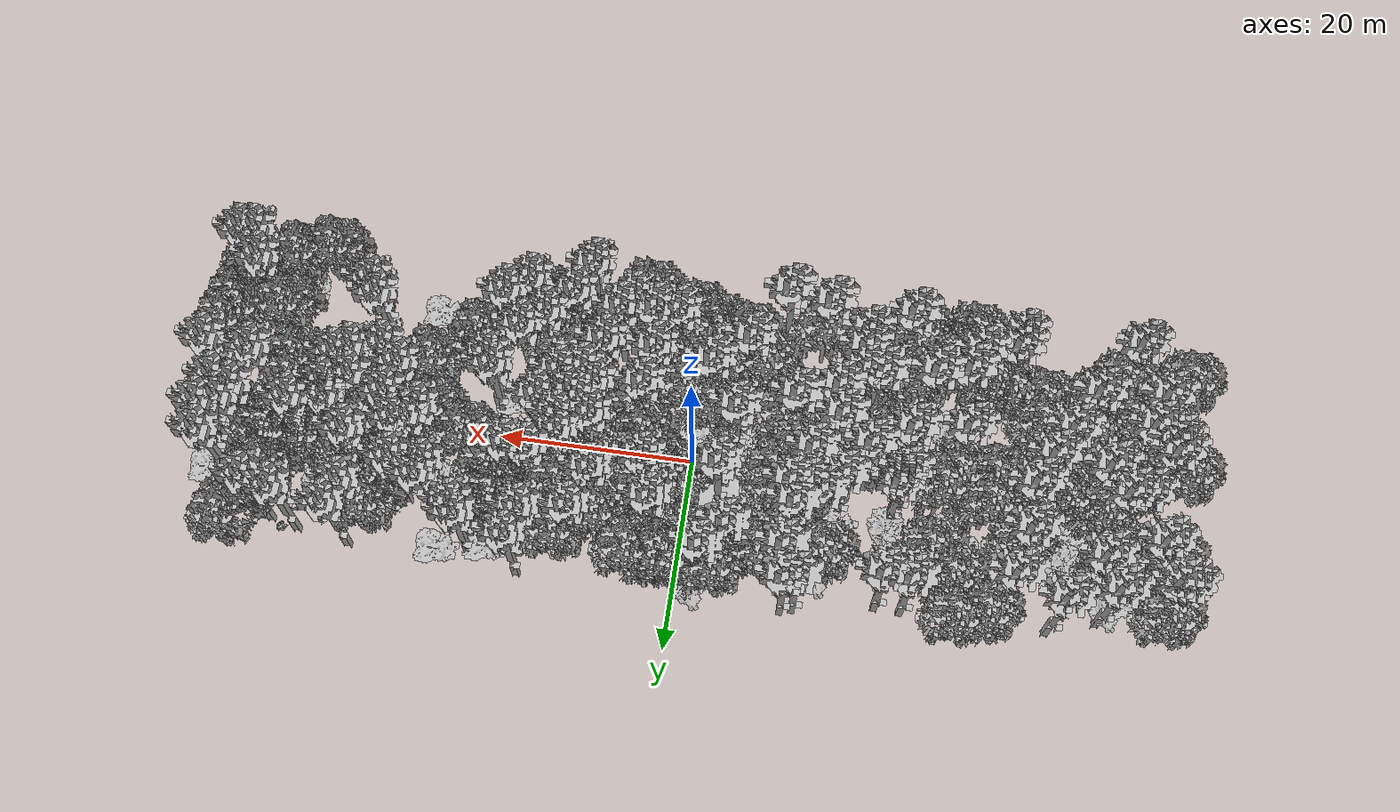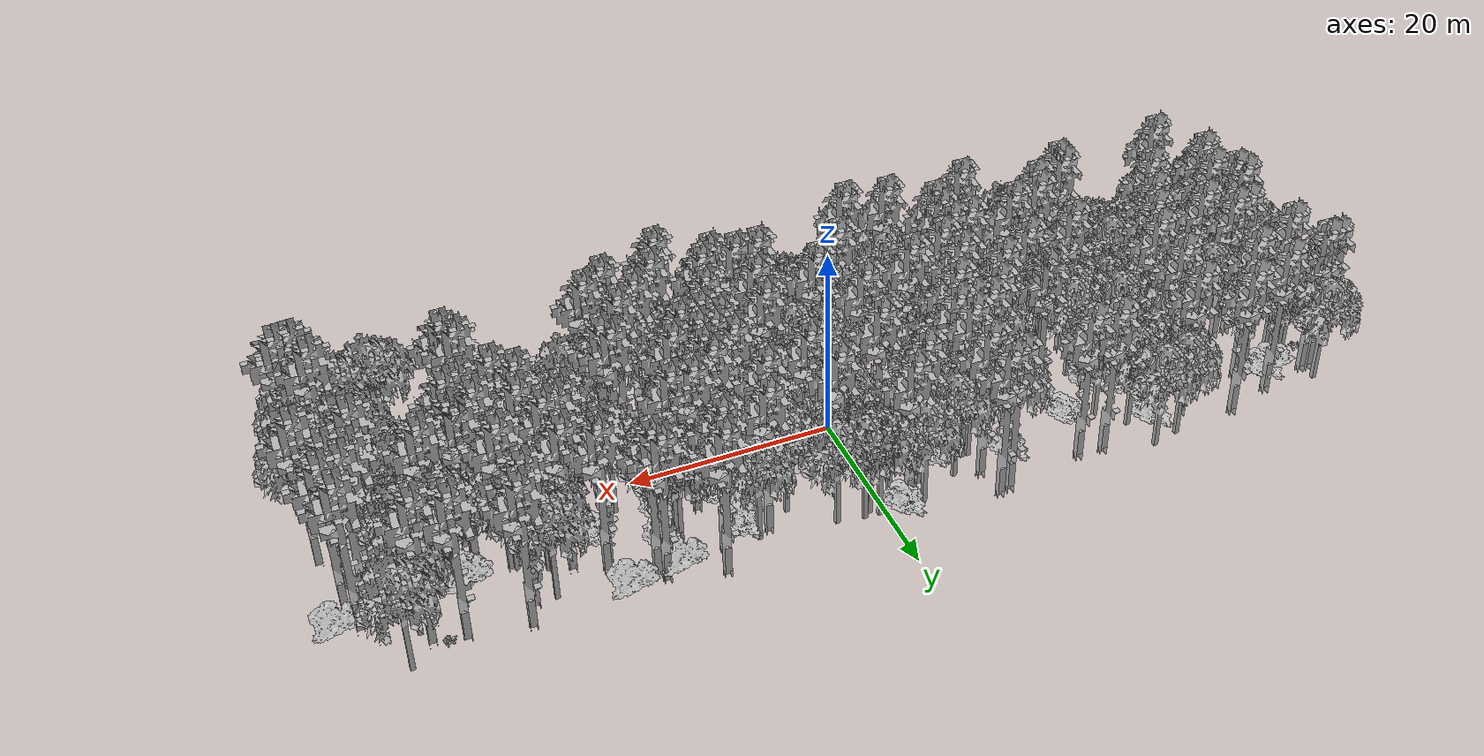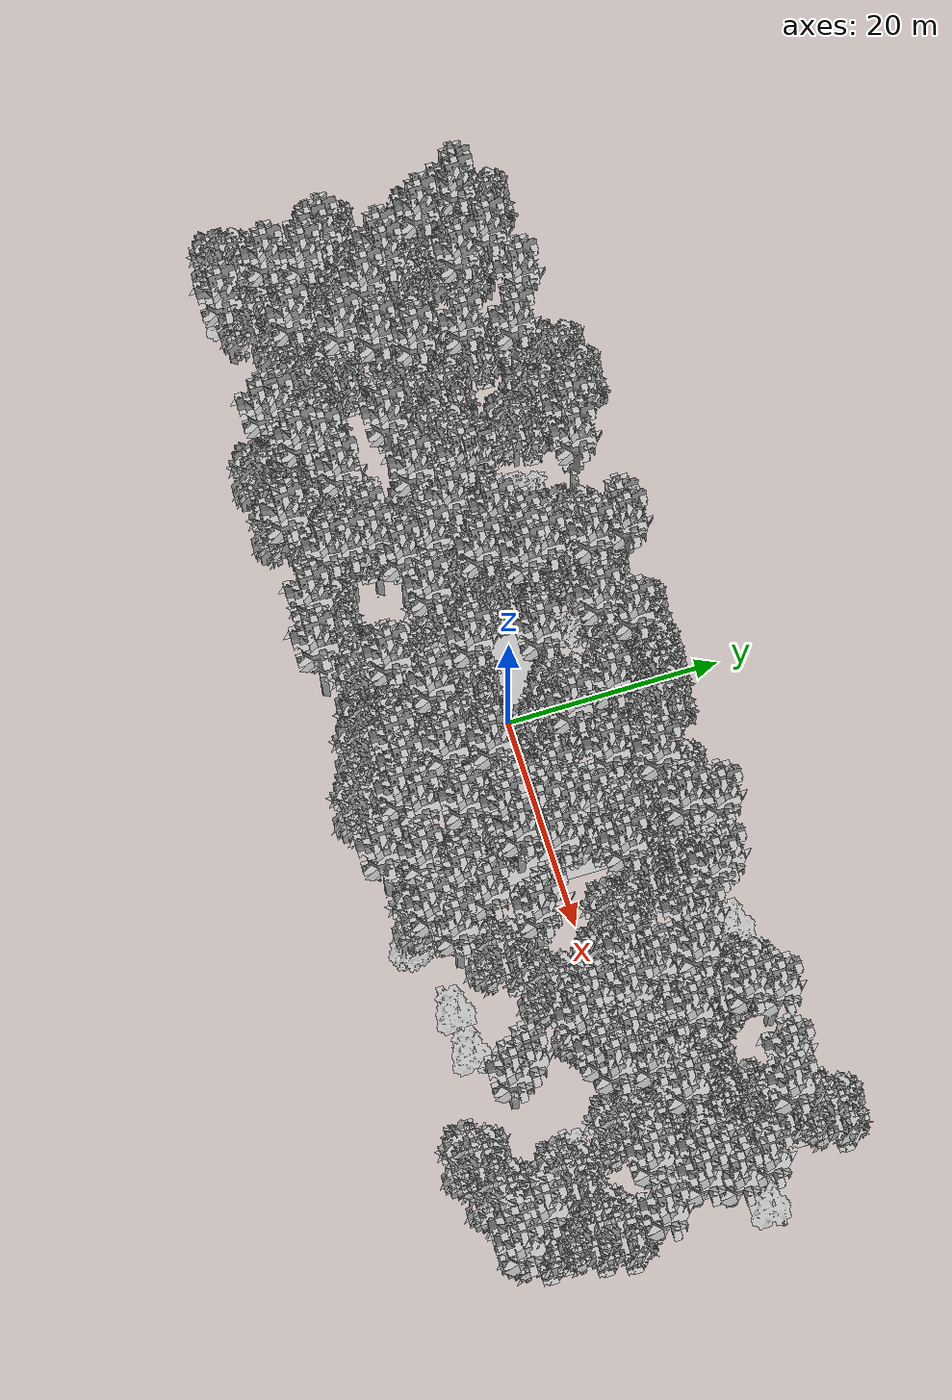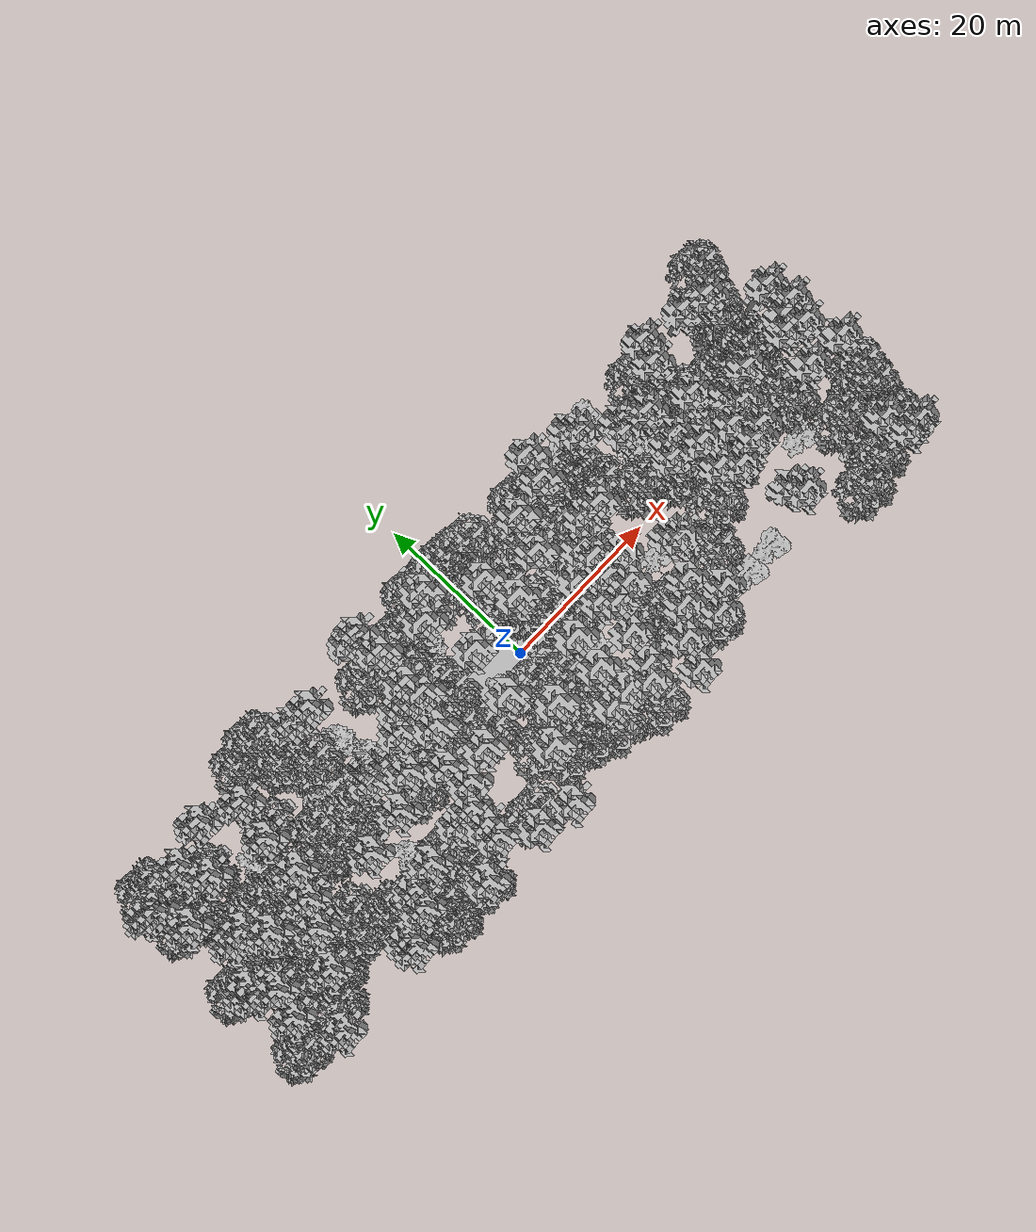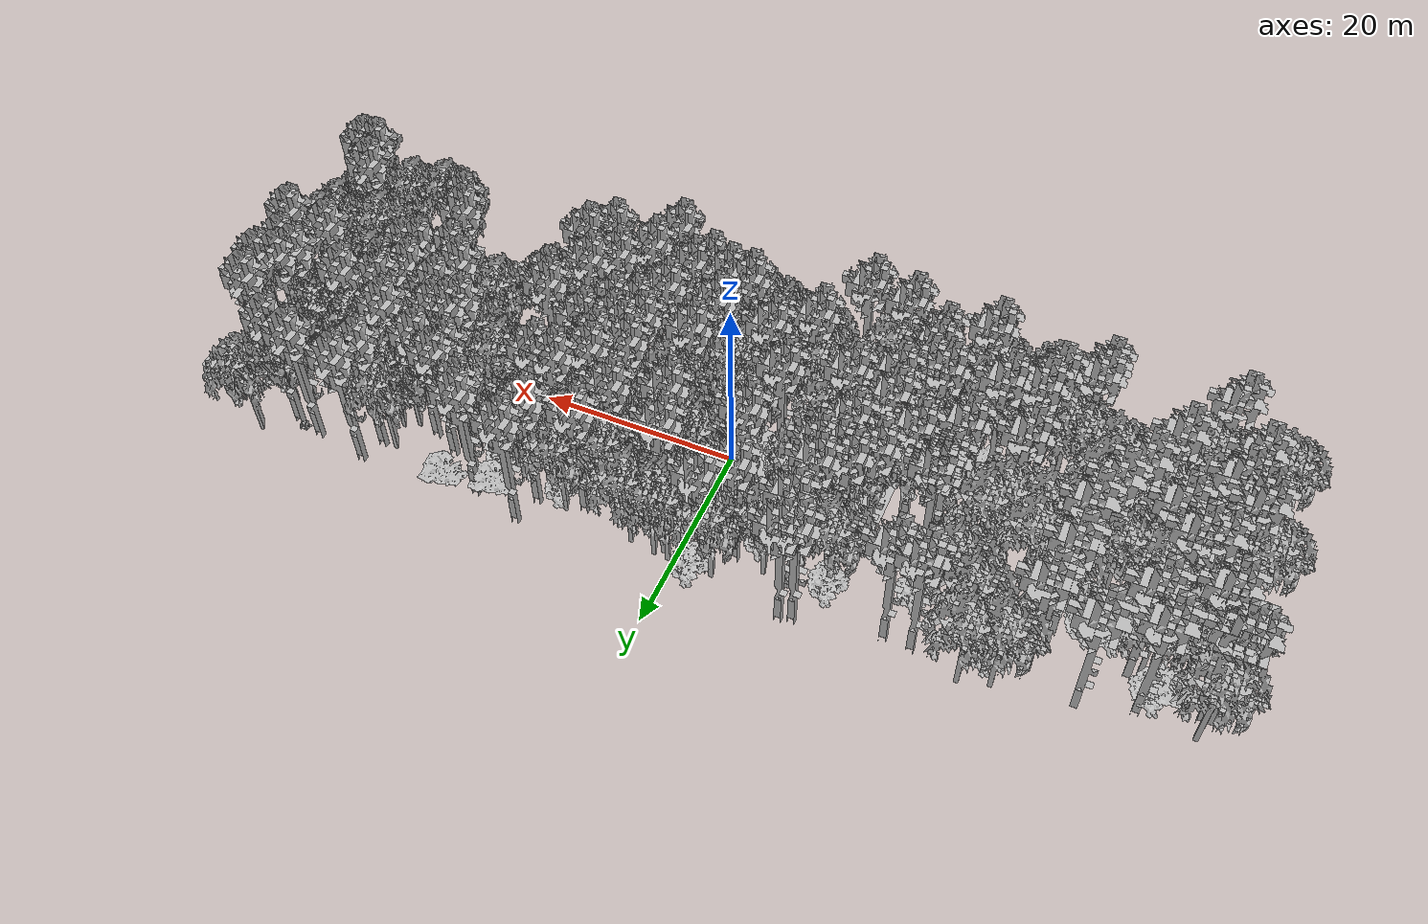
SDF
<sdf version="1.7">
    <world name="default">
        <plugin name="mrs_gazebo_static_transform_republisher_plugin" filename="libMrsGazeboCommonResources_StaticTransformRepublisher.so"/>
        <spherical_coordinates>
            <surface_model>EARTH_WGS84</surface_model>
            <latitude_deg>47.3977</latitude_deg>
            <longitude_deg>8.54559</longitude_deg>
            <elevation>0</elevation>
            <heading_deg>0</heading_deg>
        </spherical_coordinates>
        <physics name="default_physics" default="0" type="ode">
            <ode>
                <solver>
                    <type>quick</type>
                    <iters>10</iters>
                    <sor>1.3</sor>
                    <use_dynamic_moi_rescaling>0</use_dynamic_moi_rescaling>
                </solver>
                <constraints>
                    <cfm>0</cfm>
                    <erp>0.2</erp>
                    <contact_max_correcting_vel>1000</contact_max_correcting_vel>
                    <contact_surface_layer>0.001</contact_surface_layer>
                </constraints>
            </ode>
            <max_step_size>0.004</max_step_size>
            <real_time_factor>1</real_time_factor>
            <real_time_update_rate>250</real_time_update_rate>
        </physics>
        <scene>
            <shadows>0</shadows>
            <ambient>0.4 0.4 0.4 1</ambient>
            <background>0.7 0.7 0.7 1</background>
        </scene>
        <light name="sun" type="directional">
            <pose>0 0 1000 0.4 0.2 0</pose>
            <diffuse>1 1 1 1</diffuse>
            <specular>0.6 0.6 0.6 1</specular>
            <direction>0.1 0.1 -0.9</direction>
            <attenuation>
                <range>20</range>
                <constant>0.5</constant>
                <linear>0.01</linear>
                <quadratic>0.001</quadratic>
            </attenuation>
            <cast_shadows>1</cast_shadows>
            <spot>
                <inner_angle>0</inner_angle>
                <outer_angle>0</outer_angle>
                <falloff>0</falloff>
            </spot>
        </light>
        <model name="ground_plane">
            <static>1</static>
            <link name="link">
                <collision name="collision">
                    <pose>-50 0 0 0 -0 0</pose>
                    <geometry>
                        <plane>
                            <normal>0 0 1</normal>
                            <size>100 100</size>
                        </plane>
                    </geometry>
                    <surface>
                        <contact>
                            <ode>
                                <min_depth>0.01</min_depth>
                                <max_vel>0</max_vel>
                            </ode>
                        </contact>
                        <friction>
                            <ode/>
                            <torsional>
                                <ode/>
                            </torsional>
                        </friction>
                        <bounce/>
                    </surface>
                    <max_contacts>10</max_contacts>
                </collision>
                <visual name="grass">
                    <pose>0 0 0 0 -0 0</pose>
                    <cast_shadows>0</cast_shadows>
                    <geometry>
                        <mesh>
                            <scale>0.5814285714285714 0.18142857142857144 0.1</scale>
                            <uri>file://grass_plane/meshes/grass_plane.dae</uri>
                        </mesh>
                    </geometry>
                </visual>
                <self_collide>0</self_collide>
                <enable_wind>0</enable_wind>
                <kinematic>0</kinematic>
            </link>
        </model>
        <model name="the_void">
            <static>1</static>
            <link name="link">
                <pose>0 0 0.1 0 -0 0</pose>
                <visual name="the_void">
                    <pose>0 0 2 0 -0 0</pose>
                    <geometry>
                        <sphere>
                            <radius>0.25</radius>
                        </sphere>
                    </geometry>
                    <material>
                        <script>
                            <uri>file://media/materials/scripts/Gazebo.material</uri>
                            <name>Gazebo/Black</name>
                        </script>
                    </material>
                </visual>
                <self_collide>0</self_collide>
                <enable_wind>0</enable_wind>
                <kinematic>0</kinematic>
            </link>
            <pose>-1000 -1000 0 0 -0 0</pose>
        </model>
        <gui fullscreen="0">
            <camera name="camera">
                <pose>35.1577 98.6044 40.0204 0 0.407996 -1.99761</pose>
                <view_controller>orbit</view_controller>
                <projection_type>perspective</projection_type>
            </camera>
        </gui>
        <plugin name="mrs_gazebo_rviz_cam_synchronizer" filename="libMrsGazeboCommonResources_RvizCameraSynchronizer.so">
            <target_frame_id>gazebo_user_camera</target_frame_id>
            <world_origin_frame_id>uav1/gps_origin</world_origin_frame_id>
            <frame_to_follow>uav1</frame_to_follow>
        </plugin>
        <gravity>0 0 -9.8066</gravity>
        <magnetic_field>6e-06 2.3e-05 -4.2e-05</magnetic_field>
        <atmosphere type="adiabatic"/>
        <wind/>
        <model name="Tree 0">
            <static>1</static>
            <pose>4.5045631408654145 12.51372456393841 0 1.57079 -0 0</pose>
            <link name="link">
                <pose>0 0 0 0 -0 0</pose>
                <collision name="collision">
                    <geometry>
                        <mesh>
                            <scale>3.5 5 3.5</scale>
                            <uri>model://tree_2/meshes/tree_2.obj</uri>
                        </mesh>
                    </geometry>
                    <max_contacts>10</max_contacts>
                    <surface>
                        <contact>
                            <ode/>
                        </contact>
                        <bounce/>
                        <friction>
                            <torsional>
                                <ode/>
                            </torsional>
                            <ode/>
                        </friction>
                    </surface>
                </collision>
                <visual name="visual">
                    <geometry>
                        <mesh>
                            <scale>3.5 5 3.5</scale>
                            <uri>model://tree_2/meshes/tree_2.obj</uri>
                        </mesh>
                    </geometry>
                </visual>
                <self_collide>0</self_collide>
                <enable_wind>0</enable_wind>
                <kinematic>0</kinematic>
            </link>
        </model>
        <model name="Tree 1">
            <static>1</static>
            <pose>1.1524860178372265 -9.828742389638322 0 1.57079 -0 0</pose>
            <link name="link">
                <pose>0 0 0 0 -0 0</pose>
                <collision name="collision">
                    <geometry>
                        <mesh>
                            <scale>3 2 3</scale>
                            <uri>model://tree_3/meshes/tree_3.obj</uri>
                        </mesh>
                    </geometry>
                    <max_contacts>10</max_contacts>
                    <surface>
                        <contact>
                            <ode/>
                        </contact>
                        <bounce/>
                        <friction>
                            <torsional>
                                <ode/>
                            </torsional>
                            <ode/>
                        </friction>
                    </surface>
                </collision>
                <visual name="visual">
                    <geometry>
                        <mesh>
                            <scale>3 2 3</scale>
                            <uri>model://tree_3/meshes/tree_3.obj</uri>
                        </mesh>
                    </geometry>
                </visual>
                <self_collide>0</self_collide>
                <enable_wind>0</enable_wind>
                <kinematic>0</kinematic>
            </link>
        </model>
        <model name="Tree 2">
            <static>1</static>
            <pose>-12.256642055386294 -14.262163504413634 0 1.57079 -0 0</pose>
            <link name="link">
                <pose>0 0 0 0 -0 0</pose>
                <collision name="collision">
                    <geometry>
                        <mesh>
                            <scale>3.5 5 3.5</scale>
                            <uri>model://tree_9/meshes/tree_9.obj</uri>
                        </mesh>
                    </geometry>
                    <max_contacts>10</max_contacts>
                    <surface>
                        <contact>
                            <ode/>
                        </contact>
                        <bounce/>
                        <friction>
                            <torsional>
                                <ode/>
                            </torsional>
                            <ode/>
                        </friction>
                    </surface>
                </collision>
                <visual name="visual">
                    <geometry>
                        <mesh>
                            <scale>3.5 5 3.5</scale>
                            <uri>model://tree_9/meshes/tree_9.obj</uri>
                        </mesh>
                    </geometry>
                </visual>
                <self_collide>0</self_collide>
                <enable_wind>0</enable_wind>
                <kinematic>0</kinematic>
            </link>
        </model>
        <model name="Tree 3">
            <static>1</static>
            <pose>-8.664181829778109 -3.5017930155618444 0 1.57079 -0 0</pose>
            <link name="link">
                <pose>0 0 0 0 -0 0</pose>
                <collision name="collision">
                    <geometry>
                        <mesh>
                            <scale>3.5 5 3.5</scale>
                            <uri>model://tree_2/meshes/tree_2.obj</uri>
                        </mesh>
                    </geometry>
                    <max_contacts>10</max_contacts>
                    <surface>
                        <contact>
                            <ode/>
                        </contact>
                        <bounce/>
                        <friction>
                            <torsional>
                                <ode/>
                            </torsional>
                            <ode/>
                        </friction>
                    </surface>
                </collision>
                <visual name="visual">
                    <geometry>
                        <mesh>
                            <scale>3.5 5 3.5</scale>
                            <uri>model://tree_2/meshes/tree_2.obj</uri>
                        </mesh>
                    </geometry>
                </visual>
                <self_collide>0</self_collide>
                <enable_wind>0</enable_wind>
                <kinematic>0</kinematic>
            </link>
        </model>
        <model name="Tree 4">
            <static>1</static>
            <pose>30.447506198943657 11.661409019670593 0 1.57079 -0 0</pose>
            <link name="link">
                <pose>0 0 0 0 -0 0</pose>
                <collision name="collision">
                    <geometry>
                        <mesh>
                            <scale>3.5 5 3.5</scale>
                            <uri>model://tree_2/meshes/tree_2.obj</uri>
                        </mesh>
                    </geometry>
                    <max_contacts>10</max_contacts>
                    <surface>
                        <contact>
                            <ode/>
                        </contact>
                        <bounce/>
                        <friction>
                            <torsional>
                                <ode/>
                            </torsional>
                            <ode/>
                        </friction>
                    </surface>
                </collision>
                <visual name="visual">
                    <geometry>
                        <mesh>
                            <scale>3.5 5 3.5</scale>
                            <uri>model://tree_2/meshes/tree_2.obj</uri>
                        </mesh>
                    </geometry>
                </visual>
                <self_collide>0</self_collide>
                <enable_wind>0</enable_wind>
                <kinematic>0</kinematic>
            </link>
        </model>
        <model name="Tree 5">
            <static>1</static>
            <pose>46.26778932260032 -13.657653909330001 0 1.57079 -0 0</pose>
            <link name="link">
                <pose>0 0 0 0 -0 0</pose>
                <collision name="collision">
                    <geometry>
                        <mesh>
                            <scale>3.5 5 3.5</scale>
                            <uri>model://tree_9/meshes/tree_9.obj</uri>
                        </mesh>
                    </geometry>
                    <max_contacts>10</max_contacts>
                    <surface>
                        <contact>
                            <ode/>
                        </contact>
                        <bounce/>
                        <friction>
                            <torsional>
                                <ode/>
                            </torsional>
                            <ode/>
                        </friction>
                    </surface>
                </collision>
                <visual name="visual">
                    <geometry>
                        <mesh>
                            <scale>3.5 5 3.5</scale>
                            <uri>model://tree_9/meshes/tree_9.obj</uri>
                        </mesh>
                    </geometry>
                </visual>
                <self_collide>0</self_collide>
                <enable_wind>0</enable_wind>
                <kinematic>0</kinematic>
            </link>
        </model>
        <model name="Tree 6">
            <static>1</static>
            <pose>4.058021283641878 4.577086738715732 0 1.57079 -0 0</pose>
            <link name="link">
                <pose>0 0 0 0 -0 0</pose>
                <collision name="collision">
                    <geometry>
                        <mesh>
                            <scale>3.5 5 3.5</scale>
                            <uri>model://tree_9/meshes/tree_9.obj</uri>
                        </mesh>
                    </geometry>
                    <max_contacts>10</max_contacts>
                    <surface>
                        <contact>
                            <ode/>
                        </contact>
                        <bounce/>
                        <friction>
                            <torsional>
                                <ode/>
                            </torsional>
                            <ode/>
                        </friction>
                    </surface>
                </collision>
                <visual name="visual">
                    <geometry>
                        <mesh>
                            <scale>3.5 5 3.5</scale>
                            <uri>model://tree_9/meshes/tree_9.obj</uri>
                        </mesh>
                    </geometry>
                </visual>
                <self_collide>0</self_collide>
                <enable_wind>0</enable_wind>
                <kinematic>0</kinematic>
            </link>
        </model>
        <model name="Tree 7">
            <static>1</static>
            <pose>32.626736629111505 6.783906813171935 0 1.57079 -0 0</pose>
            <link name="link">
                <pose>0 0 0 0 -0 0</pose>
                <collision name="collision">
                    <geometry>
                        <mesh>
                            <scale>3.5 5 3.5</scale>
                            <uri>model://tree_2/meshes/tree_2.obj</uri>
                        </mesh>
                    </geometry>
                    <max_contacts>10</max_contacts>
                    <surface>
                        <contact>
                            <ode/>
                        </contact>
                        <bounce/>
                        <friction>
                            <torsional>
                                <ode/>
                            </torsional>
                            <ode/>
                        </friction>
                    </surface>
                </collision>
                <visual name="visual">
                    <geometry>
                        <mesh>
                            <scale>3.5 5 3.5</scale>
                            <uri>model://tree_2/meshes/tree_2.obj</uri>
                        </mesh>
                    </geometry>
                </visual>
                <self_collide>0</self_collide>
                <enable_wind>0</enable_wind>
                <kinematic>0</kinematic>
            </link>
        </model>
        <model name="Tree 8">
            <static>1</static>
            <pose>39.279730726296535 -14.857342049592196 0 1.57079 -0 0</pose>
            <link name="link">
                <pose>0 0 0 0 -0 0</pose>
                <collision name="collision">
                    <geometry>
                        <mesh>
                            <scale>3.5 5 3.5</scale>
                            <uri>model://tree_2/meshes/tree_2.obj</uri>
                        </mesh>
                    </geometry>
                    <max_contacts>10</max_contacts>
                    <surface>
                        <contact>
                            <ode/>
                        </contact>
                        <bounce/>
                        <friction>
                            <torsional>
                                <ode/>
                            </torsional>
                            <ode/>
                        </friction>
                    </surface>
                </collision>
                <visual name="visual">
                    <geometry>
                        <mesh>
                            <scale>3.5 5 3.5</scale>
                            <uri>model://tree_2/meshes/tree_2.obj</uri>
                        </mesh>
                    </geometry>
                </visual>
                <self_collide>0</self_collide>
                <enable_wind>0</enable_wind>
                <kinematic>0</kinematic>
            </link>
        </model>
        <model name="Tree 9">
            <static>1</static>
            <pose>26.08876032020335 1.0715336775845756 0 1.57079 -0 0</pose>
            <link name="link">
                <pose>0 0 0 0 -0 0</pose>
                <collision name="collision">
                    <geometry>
                        <mesh>
                            <scale>3.5 5 3.5</scale>
                            <uri>model://tree_2/meshes/tree_2.obj</uri>
                        </mesh>
                    </geometry>
                    <max_contacts>10</max_contacts>
                    <surface>
                        <contact>
                            <ode/>
                        </contact>
                        <bounce/>
                        <friction>
                            <torsional>
                                <ode/>
                            </torsional>
                            <ode/>
                        </friction>
                    </surface>
                </collision>
                <visual name="visual">
                    <geometry>
                        <mesh>
                            <scale>3.5 5 3.5</scale>
                            <uri>model://tree_2/meshes/tree_2.obj</uri>
                        </mesh>
                    </geometry>
                </visual>
                <self_collide>0</self_collide>
                <enable_wind>0</enable_wind>
                <kinematic>0</kinematic>
            </link>
        </model>
        <model name="Tree 10">
            <static>1</static>
            <pose>48.38416545549488 -1.3651510952334238 0 1.57079 -0 0</pose>
            <link name="link">
                <pose>0 0 0 0 -0 0</pose>
                <collision name="collision">
                    <geometry>
                        <mesh>
                            <scale>3.5 5 3.5</scale>
                            <uri>model://tree_9/meshes/tree_9.obj</uri>
                        </mesh>
                    </geometry>
                    <max_contacts>10</max_contacts>
                    <surface>
                        <contact>
                            <ode/>
                        </contact>
                        <bounce/>
                        <friction>
                            <torsional>
                                <ode/>
                            </torsional>
                            <ode/>
                        </friction>
                    </surface>
                </collision>
                <visual name="visual">
                    <geometry>
                        <mesh>
                            <scale>3.5 5 3.5</scale>
                            <uri>model://tree_9/meshes/tree_9.obj</uri>
                        </mesh>
                    </geometry>
                </visual>
                <self_collide>0</self_collide>
                <enable_wind>0</enable_wind>
                <kinematic>0</kinematic>
            </link>
        </model>
        <model name="Tree 11">
            <static>1</static>
            <pose>12.547425624584434 4.673868664163017 0 1.57079 -0 0</pose>
            <link name="link">
                <pose>0 0 0 0 -0 0</pose>
                <collision name="collision">
                    <geometry>
                        <mesh>
                            <scale>3.5 5 3.5</scale>
                            <uri>model://tree_2/meshes/tree_2.obj</uri>
                        </mesh>
                    </geometry>
                    <max_contacts>10</max_contacts>
                    <surface>
                        <contact>
                            <ode/>
                        </contact>
                        <bounce/>
                        <friction>
                            <torsional>
                                <ode/>
                            </torsional>
                            <ode/>
                        </friction>
                    </surface>
                </collision>
                <visual name="visual">
                    <geometry>
                        <mesh>
                            <scale>3.5 5 3.5</scale>
                            <uri>model://tree_2/meshes/tree_2.obj</uri>
                        </mesh>
                    </geometry>
                </visual>
                <self_collide>0</self_collide>
                <enable_wind>0</enable_wind>
                <kinematic>0</kinematic>
            </link>
        </model>
        <model name="Tree 12">
            <static>1</static>
            <pose>45.61058705122035 4.524592553378415 0 1.57079 -0 0</pose>
            <link name="link">
                <pose>0 0 0 0 -0 0</pose>
                <collision name="collision">
                    <geometry>
                        <mesh>
                            <scale>3.5 5 3.5</scale>
                            <uri>model://tree_9/meshes/tree_9.obj</uri>
                        </mesh>
                    </geometry>
                    <max_contacts>10</max_contacts>
                    <surface>
                        <contact>
                            <ode/>
                        </contact>
                        <bounce/>
                        <friction>
                            <torsional>
                                <ode/>
                            </torsional>
                            <ode/>
                        </friction>
                    </surface>
                </collision>
                <visual name="visual">
                    <geometry>
                        <mesh>
                            <scale>3.5 5 3.5</scale>
                            <uri>model://tree_9/meshes/tree_9.obj</uri>
                        </mesh>
                    </geometry>
                </visual>
                <self_collide>0</self_collide>
                <enable_wind>0</enable_wind>
                <kinematic>0</kinematic>
            </link>
        </model>
        <model name="Tree 13">
            <static>1</static>
            <pose>-17.65162149736658 -9.048937254308237 0 1.57079 -0 0</pose>
            <link name="link">
                <pose>0 0 0 0 -0 0</pose>
                <collision name="collision">
                    <geometry>
                        <mesh>
                            <scale>3.5 5 3.5</scale>
                            <uri>model://tree_2/meshes/tree_2.obj</uri>
                        </mesh>
                    </geometry>
                    <max_contacts>10</max_contacts>
                    <surface>
                        <contact>
                            <ode/>
                        </contact>
                        <bounce/>
                        <friction>
                            <torsional>
                                <ode/>
                            </torsional>
                            <ode/>
                        </friction>
                    </surface>
                </collision>
                <visual name="visual">
                    <geometry>
                        <mesh>
                            <scale>3.5 5 3.5</scale>
                            <uri>model://tree_2/meshes/tree_2.obj</uri>
                        </mesh>
                    </geometry>
                </visual>
                <self_collide>0</self_collide>
                <enable_wind>0</enable_wind>
                <kinematic>0</kinematic>
            </link>
        </model>
        <model name="Tree 14">
            <static>1</static>
            <pose>4.569066756161291 -6.927527562204798 0 1.57079 -0 0</pose>
            <link name="link">
                <pose>0 0 0 0 -0 0</pose>
                <collision name="collision">
                    <geometry>
                        <mesh>
                            <scale>3.5 5 3.5</scale>
                            <uri>model://tree_9/meshes/tree_9.obj</uri>
                        </mesh>
                    </geometry>
                    <max_contacts>10</max_contacts>
                    <surface>
                        <contact>
                            <ode/>
                        </contact>
                        <bounce/>
                        <friction>
                            <torsional>
                                <ode/>
                            </torsional>
                            <ode/>
                        </friction>
                    </surface>
                </collision>
                <visual name="visual">
                    <geometry>
                        <mesh>
                            <scale>3.5 5 3.5</scale>
                            <uri>model://tree_9/meshes/tree_9.obj</uri>
                        </mesh>
                    </geometry>
                </visual>
                <self_collide>0</self_collide>
                <enable_wind>0</enable_wind>
                <kinematic>0</kinematic>
            </link>
        </model>
        <model name="Tree 15">
            <static>1</static>
            <pose>-31.964274468669547 0.09702723587530748 0 1.57079 -0 0</pose>
            <link name="link">
                <pose>0 0 0 0 -0 0</pose>
                <collision name="collision">
                    <geometry>
                        <mesh>
                            <scale>3.5 5 3.5</scale>
                            <uri>model://tree_2/meshes/tree_2.obj</uri>
                        </mesh>
                    </geometry>
                    <max_contacts>10</max_contacts>
                    <surface>
                        <contact>
                            <ode/>
                        </contact>
                        <bounce/>
                        <friction>
                            <torsional>
                                <ode/>
                            </torsional>
                            <ode/>
                        </friction>
                    </surface>
                </collision>
                <visual name="visual">
                    <geometry>
                        <mesh>
                            <scale>3.5 5 3.5</scale>
                            <uri>model://tree_2/meshes/tree_2.obj</uri>
                        </mesh>
                    </geometry>
                </visual>
                <self_collide>0</self_collide>
                <enable_wind>0</enable_wind>
                <kinematic>0</kinematic>
            </link>
        </model>
        <model name="Tree 16">
            <static>1</static>
            <pose>33.20872274278052 13.63194868836116 0 1.57079 -0 0</pose>
            <link name="link">
                <pose>0 0 0 0 -0 0</pose>
                <collision name="collision">
                    <geometry>
                        <mesh>
                            <scale>3.5 5 3.5</scale>
                            <uri>model://tree_9/meshes/tree_9.obj</uri>
                        </mesh>
                    </geometry>
                    <max_contacts>10</max_contacts>
                    <surface>
                        <contact>
                            <ode/>
                        </contact>
                        <bounce/>
                        <friction>
                            <torsional>
                                <ode/>
                            </torsional>
                            <ode/>
                        </friction>
                    </surface>
                </collision>
                <visual name="visual">
                    <geometry>
                        <mesh>
                            <scale>3.5 5 3.5</scale>
                            <uri>model://tree_9/meshes/tree_9.obj</uri>
                        </mesh>
                    </geometry>
                </visual>
                <self_collide>0</self_collide>
                <enable_wind>0</enable_wind>
                <kinematic>0</kinematic>
            </link>
        </model>
        <model name="Tree 17">
            <static>1</static>
            <pose>-1.5464547842415897 10.502749499127287 0 1.57079 -0 0</pose>
            <link name="link">
                <pose>0 0 0 0 -0 0</pose>
                <collision name="collision">
                    <geometry>
                        <mesh>
                            <scale>3.5 5 3.5</scale>
                            <uri>model://tree_2/meshes/tree_2.obj</uri>
                        </mesh>
                    </geometry>
                    <max_contacts>10</max_contacts>
                    <surface>
                        <contact>
                            <ode/>
                        </contact>
                        <bounce/>
                        <friction>
                            <torsional>
                                <ode/>
                            </torsional>
                            <ode/>
                        </friction>
                    </surface>
                </collision>
                <visual name="visual">
                    <geometry>
                        <mesh>
                            <scale>3.5 5 3.5</scale>
                            <uri>model://tree_2/meshes/tree_2.obj</uri>
                        </mesh>
                    </geometry>
                </visual>
                <self_collide>0</self_collide>
                <enable_wind>0</enable_wind>
                <kinematic>0</kinematic>
            </link>
        </model>
        <model name="Tree 18">
            <static>1</static>
            <pose>-37.35110678123039 12.686138787581811 0 1.57079 -0 0</pose>
            <link name="link">
                <pose>0 0 0 0 -0 0</pose>
                <collision name="collision">
                    <geometry>
                        <mesh>
                            <scale>3.5 5 3.5</scale>
                            <uri>model://tree_9/meshes/tree_9.obj</uri>
                        </mesh>
                    </geometry>
                    <max_contacts>10</max_contacts>
                    <surface>
                        <contact>
                            <ode/>
                        </contact>
                        <bounce/>
                        <friction>
                            <torsional>
                                <ode/>
                            </torsional>
                            <ode/>
                        </friction>
                    </surface>
                </collision>
                <visual name="visual">
                    <geometry>
                        <mesh>
                            <scale>3.5 5 3.5</scale>
                            <uri>model://tree_9/meshes/tree_9.obj</uri>
                        </mesh>
                    </geometry>
                </visual>
                <self_collide>0</self_collide>
                <enable_wind>0</enable_wind>
                <kinematic>0</kinematic>
            </link>
        </model>
        <model name="Tree 19">
            <static>1</static>
            <pose>-4.870577590325688 -9.295475551576919 0 1.57079 -0 0</pose>
            <link name="link">
                <pose>0 0 0 0 -0 0</pose>
                <collision name="collision">
                    <geometry>
                        <mesh>
                            <scale>3.5 5 3.5</scale>
                            <uri>model://tree_9/meshes/tree_9.obj</uri>
                        </mesh>
                    </geometry>
                    <max_contacts>10</max_contacts>
                    <surface>
                        <contact>
                            <ode/>
                        </contact>
                        <bounce/>
                        <friction>
                            <torsional>
                                <ode/>
                            </torsional>
                            <ode/>
                        </friction>
                    </surface>
                </collision>
                <visual name="visual">
                    <geometry>
                        <mesh>
                            <scale>3.5 5 3.5</scale>
                            <uri>model://tree_9/meshes/tree_9.obj</uri>
                        </mesh>
                    </geometry>
                </visual>
                <self_collide>0</self_collide>
                <enable_wind>0</enable_wind>
                <kinematic>0</kinematic>
            </link>
        </model>
        <model name="Tree 20">
            <static>1</static>
            <pose>19.296432104810023 6.59171631181357 0 1.57079 -0 0</pose>
            <link name="link">
                <pose>0 0 0 0 -0 0</pose>
                <collision name="collision">
                    <geometry>
                        <mesh>
                            <scale>3.5 5 3.5</scale>
                            <uri>model://tree_2/meshes/tree_2.obj</uri>
                        </mesh>
                    </geometry>
                    <max_contacts>10</max_contacts>
                    <surface>
                        <contact>
                            <ode/>
                        </contact>
                        <bounce/>
                        <friction>
                            <torsional>
                                <ode/>
                            </torsional>
                            <ode/>
                        </friction>
                    </surface>
                </collision>
                <visual name="visual">
                    <geometry>
                        <mesh>
                            <scale>3.5 5 3.5</scale>
                            <uri>model://tree_2/meshes/tree_2.obj</uri>
                        </mesh>
                    </geometry>
                </visual>
                <self_collide>0</self_collide>
                <enable_wind>0</enable_wind>
                <kinematic>0</kinematic>
            </link>
        </model>
        <model name="Tree 21">
            <static>1</static>
            <pose>-24.47080471725276 8.407493665785822 0 1.57079 -0 0</pose>
            <link name="link">
                <pose>0 0 0 0 -0 0</pose>
                <collision name="collision">
                    <geometry>
                        <mesh>
                            <scale>3.5 5 3.5</scale>
                            <uri>model://tree_2/meshes/tree_2.obj</uri>
                        </mesh>
                    </geometry>
                    <max_contacts>10</max_contacts>
                    <surface>
                        <contact>
                            <ode/>
                        </contact>
                        <bounce/>
                        <friction>
                            <torsional>
                                <ode/>
                            </torsional>
                            <ode/>
                        </friction>
                    </surface>
                </collision>
                <visual name="visual">
                    <geometry>
                        <mesh>
                            <scale>3.5 5 3.5</scale>
                            <uri>model://tree_2/meshes/tree_2.obj</uri>
                        </mesh>
                    </geometry>
                </visual>
                <self_collide>0</self_collide>
                <enable_wind>0</enable_wind>
                <kinematic>0</kinematic>
            </link>
        </model>
        <model name="Tree 22">
            <static>1</static>
            <pose>17.99346908390767 -7.283222774635866 0 1.57079 -0 0</pose>
            <link name="link">
                <pose>0 0 0 0 -0 0</pose>
                <collision name="collision">
                    <geometry>
                        <mesh>
                            <scale>3.5 5 3.5</scale>
                            <uri>model://tree_9/meshes/tree_9.obj</uri>
                        </mesh>
                    </geometry>
                    <max_contacts>10</max_contacts>
                    <surface>
                        <contact>
                            <ode/>
                        </contact>
                        <bounce/>
                        <friction>
                            <torsional>
                                <ode/>
                            </torsional>
                            <ode/>
                        </friction>
                    </surface>
                </collision>
                <visual name="visual">
                    <geometry>
                        <mesh>
                            <scale>3.5 5 3.5</scale>
                            <uri>model://tree_9/meshes/tree_9.obj</uri>
                        </mesh>
                    </geometry>
                </visual>
                <self_collide>0</self_collide>
                <enable_wind>0</enable_wind>
                <kinematic>0</kinematic>
            </link>
        </model>
        <model name="Tree 23">
            <static>1</static>
            <pose>4.654935944965949 -10.912607069084592 0 1.57079 -0 0</pose>
            <link name="link">
                <pose>0 0 0 0 -0 0</pose>
                <collision name="collision">
                    <geometry>
                        <mesh>
                            <scale>3.5 5 3.5</scale>
                            <uri>model://tree_2/meshes/tree_2.obj</uri>
                        </mesh>
                    </geometry>
                    <max_contacts>10</max_contacts>
                    <surface>
                        <contact>
                            <ode/>
                        </contact>
                        <bounce/>
                        <friction>
                            <torsional>
                                <ode/>
                            </torsional>
                            <ode/>
                        </friction>
                    </surface>
                </collision>
                <visual name="visual">
                    <geometry>
                        <mesh>
                            <scale>3.5 5 3.5</scale>
                            <uri>model://tree_2/meshes/tree_2.obj</uri>
                        </mesh>
                    </geometry>
                </visual>
                <self_collide>0</self_collide>
                <enable_wind>0</enable_wind>
                <kinematic>0</kinematic>
            </link>
        </model>
        <model name="Tree 24">
            <static>1</static>
            <pose>-39.09942627719493 -8.45320884123564 0 1.57079 -0 0</pose>
            <link name="link">
                <pose>0 0 0 0 -0 0</pose>
                <collision name="collision">
                    <geometry>
                        <mesh>
                            <scale>3.5 5 3.5</scale>
                            <uri>model://tree_9/meshes/tree_9.obj</uri>
                        </mesh>
                    </geometry>
                    <max_contacts>10</max_contacts>
                    <surface>
                        <contact>
                            <ode/>
                        </contact>
                        <bounce/>
                        <friction>
                            <torsional>
                                <ode/>
                            </torsional>
                            <ode/>
                        </friction>
                    </surface>
                </collision>
                <visual name="visual">
                    <geometry>
                        <mesh>
                            <scale>3.5 5 3.5</scale>
                            <uri>model://tree_9/meshes/tree_9.obj</uri>
                        </mesh>
                    </geometry>
                </visual>
                <self_collide>0</self_collide>
                <enable_wind>0</enable_wind>
                <kinematic>0</kinematic>
            </link>
        </model>
        <model name="Tree 25">
            <static>1</static>
            <pose>-47.45939324563728 11.88569382267178 0 1.57079 -0 0</pose>
            <link name="link">
                <pose>0 0 0 0 -0 0</pose>
                <collision name="collision">
                    <geometry>
                        <mesh>
                            <scale>3.5 5 3.5</scale>
                            <uri>model://tree_2/meshes/tree_2.obj</uri>
                        </mesh>
                    </geometry>
                    <max_contacts>10</max_contacts>
                    <surface>
                        <contact>
                            <ode/>
                        </contact>
                        <bounce/>
                        <friction>
                            <torsional>
                                <ode/>
                            </torsional>
                            <ode/>
                        </friction>
                    </surface>
                </collision>
                <visual name="visual">
                    <geometry>
                        <mesh>
                            <scale>3.5 5 3.5</scale>
                            <uri>model://tree_2/meshes/tree_2.obj</uri>
                        </mesh>
                    </geometry>
                </visual>
                <self_collide>0</self_collide>
                <enable_wind>0</enable_wind>
                <kinematic>0</kinematic>
            </link>
        </model>
        <model name="Tree 26">
            <static>1</static>
            <pose>-14.019188098989652 -5.437911901543128 0 1.57079 -0 0</pose>
            <link name="link">
                <pose>0 0 0 0 -0 0</pose>
                <collision name="collision">
                    <geometry>
                        <mesh>
                            <scale>3.5 5 3.5</scale>
                            <uri>model://tree_9/meshes/tree_9.obj</uri>
                        </mesh>
                    </geometry>
                    <max_contacts>10</max_contacts>
                    <surface>
                        <contact>
                            <ode/>
                        </contact>
                        <bounce/>
                        <friction>
                            <torsional>
                                <ode/>
                            </torsional>
                            <ode/>
                        </friction>
                    </surface>
                </collision>
                <visual name="visual">
                    <geometry>
                        <mesh>
                            <scale>3.5 5 3.5</scale>
                            <uri>model://tree_9/meshes/tree_9.obj</uri>
                        </mesh>
                    </geometry>
                </visual>
                <self_collide>0</self_collide>
                <enable_wind>0</enable_wind>
                <kinematic>0</kinematic>
            </link>
        </model>
        <model name="Tree 27">
            <static>1</static>
            <pose>43.822798079690656 14.884227019418699 0 1.57079 -0 0</pose>
            <link name="link">
                <pose>0 0 0 0 -0 0</pose>
                <collision name="collision">
                    <geometry>
                        <mesh>
                            <scale>3.5 5 3.5</scale>
                            <uri>model://tree_2/meshes/tree_2.obj</uri>
                        </mesh>
                    </geometry>
                    <max_contacts>10</max_contacts>
                    <surface>
                        <contact>
                            <ode/>
                        </contact>
                        <bounce/>
                        <friction>
                            <torsional>
                                <ode/>
                            </torsional>
                            <ode/>
                        </friction>
                    </surface>
                </collision>
                <visual name="visual">
                    <geometry>
                        <mesh>
                            <scale>3.5 5 3.5</scale>
                            <uri>model://tree_2/meshes/tree_2.obj</uri>
                        </mesh>
                    </geometry>
                </visual>
                <self_collide>0</self_collide>
                <enable_wind>0</enable_wind>
                <kinematic>0</kinematic>
            </link>
        </model>
        <model name="Tree 28">
            <static>1</static>
            <pose>42.28532530113175 11.158036692358234 0 1.57079 -0 0</pose>
            <link name="link">
                <pose>0 0 0 0 -0 0</pose>
                <collision name="collision">
                    <geometry>
                        <mesh>
                            <scale>3.5 5 3.5</scale>
                            <uri>model://tree_2/meshes/tree_2.obj</uri>
                        </mesh>
                    </geometry>
                    <max_contacts>10</max_contacts>
                    <surface>
                        <contact>
                            <ode/>
                        </contact>
                        <bounce/>
                        <friction>
                            <torsional>
                                <ode/>
                            </torsional>
                            <ode/>
                        </friction>
                    </surface>
                </collision>
                <visual name="visual">
                    <geometry>
                        <mesh>
                            <scale>3.5 5 3.5</scale>
                            <uri>model://tree_2/meshes/tree_2.obj</uri>
                        </mesh>
                    </geometry>
                </visual>
                <self_collide>0</self_collide>
                <enable_wind>0</enable_wind>
                <kinematic>0</kinematic>
            </link>
        </model>
        <model name="Tree 29">
            <static>1</static>
            <pose>28.02088922435273 8.154617963496953 0 1.57079 -0 0</pose>
            <link name="link">
                <pose>0 0 0 0 -0 0</pose>
                <collision name="collision">
                    <geometry>
                        <mesh>
                            <scale>3.5 5 3.5</scale>
                            <uri>model://tree_9/meshes/tree_9.obj</uri>
                        </mesh>
                    </geometry>
                    <max_contacts>10</max_contacts>
                    <surface>
                        <contact>
                            <ode/>
                        </contact>
                        <bounce/>
                        <friction>
                            <torsional>
                                <ode/>
                            </torsional>
                            <ode/>
                        </friction>
                    </surface>
                </collision>
                <visual name="visual">
                    <geometry>
                        <mesh>
                            <scale>3.5 5 3.5</scale>
                            <uri>model://tree_9/meshes/tree_9.obj</uri>
                        </mesh>
                    </geometry>
                </visual>
                <self_collide>0</self_collide>
                <enable_wind>0</enable_wind>
                <kinematic>0</kinematic>
            </link>
        </model>
        <model name="Tree 30">
            <static>1</static>
            <pose>14.977765230170178 11.383427615621763 0 1.57079 -0 0</pose>
            <link name="link">
                <pose>0 0 0 0 -0 0</pose>
                <collision name="collision">
                    <geometry>
                        <mesh>
                            <scale>3.5 5 3.5</scale>
                            <uri>model://tree_9/meshes/tree_9.obj</uri>
                        </mesh>
                    </geometry>
                    <max_contacts>10</max_contacts>
                    <surface>
                        <contact>
                            <ode/>
                        </contact>
                        <bounce/>
                        <friction>
                            <torsional>
                                <ode/>
                            </torsional>
                            <ode/>
                        </friction>
                    </surface>
                </collision>
                <visual name="visual">
                    <geometry>
                        <mesh>
                            <scale>3.5 5 3.5</scale>
                            <uri>model://tree_9/meshes/tree_9.obj</uri>
                        </mesh>
                    </geometry>
                </visual>
                <self_collide>0</self_collide>
                <enable_wind>0</enable_wind>
                <kinematic>0</kinematic>
            </link>
        </model>
        <model name="Tree 31">
            <static>1</static>
            <pose>33.67170362967141 -9.925883491631996 0 1.57079 -0 0</pose>
            <link name="link">
                <pose>0 0 0 0 -0 0</pose>
                <collision name="collision">
                    <geometry>
                        <mesh>
                            <scale>3.5 5 3.5</scale>
                            <uri>model://tree_9/meshes/tree_9.obj</uri>
                        </mesh>
                    </geometry>
                    <max_contacts>10</max_contacts>
                    <surface>
                        <contact>
                            <ode/>
                        </contact>
                        <bounce/>
                        <friction>
                            <torsional>
                                <ode/>
                            </torsional>
                            <ode/>
                        </friction>
                    </surface>
                </collision>
                <visual name="visual">
                    <geometry>
                        <mesh>
                            <scale>3.5 5 3.5</scale>
                            <uri>model://tree_9/meshes/tree_9.obj</uri>
                        </mesh>
                    </geometry>
                </visual>
                <self_collide>0</self_collide>
                <enable_wind>0</enable_wind>
                <kinematic>0</kinematic>
            </link>
        </model>
        <model name="Tree 32">
            <static>1</static>
            <pose>8.5975826116087 -10.593575960187067 0 1.57079 -0 0</pose>
            <link name="link">
                <pose>0 0 0 0 -0 0</pose>
                <collision name="collision">
                    <geometry>
                        <mesh>
                            <scale>3.5 5 3.5</scale>
                            <uri>model://tree_9/meshes/tree_9.obj</uri>
                        </mesh>
                    </geometry>
                    <max_contacts>10</max_contacts>
                    <surface>
                        <contact>
                            <ode/>
                        </contact>
                        <bounce/>
                        <friction>
                            <torsional>
                                <ode/>
                            </torsional>
                            <ode/>
                        </friction>
                    </surface>
                </collision>
                <visual name="visual">
                    <geometry>
                        <mesh>
                            <scale>3.5 5 3.5</scale>
                            <uri>model://tree_9/meshes/tree_9.obj</uri>
                        </mesh>
                    </geometry>
                </visual>
                <self_collide>0</self_collide>
                <enable_wind>0</enable_wind>
                <kinematic>0</kinematic>
            </link>
        </model>
        <model name="Tree 33">
            <static>1</static>
            <pose>19.280507609140912 12.06761423302585 0 1.57079 -0 0</pose>
            <link name="link">
                <pose>0 0 0 0 -0 0</pose>
                <collision name="collision">
                    <geometry>
                        <mesh>
                            <scale>3 2 3</scale>
                            <uri>model://tree_3/meshes/tree_3.obj</uri>
                        </mesh>
                    </geometry>
                    <max_contacts>10</max_contacts>
                    <surface>
                        <contact>
                            <ode/>
                        </contact>
                        <bounce/>
                        <friction>
                            <torsional>
                                <ode/>
                            </torsional>
                            <ode/>
                        </friction>
                    </surface>
                </collision>
                <visual name="visual">
                    <geometry>
                        <mesh>
                            <scale>3 2 3</scale>
                            <uri>model://tree_3/meshes/tree_3.obj</uri>
                        </mesh>
                    </geometry>
                </visual>
                <self_collide>0</self_collide>
                <enable_wind>0</enable_wind>
                <kinematic>0</kinematic>
            </link>
        </model>
        <model name="Tree 34">
            <static>1</static>
            <pose>22.427675313671912 3.15626842298742 0 1.57079 -0 0</pose>
            <link name="link">
                <pose>0 0 0 0 -0 0</pose>
                <collision name="collision">
                    <geometry>
                        <mesh>
                            <scale>3.5 5 3.5</scale>
                            <uri>model://tree_2/meshes/tree_2.obj</uri>
                        </mesh>
                    </geometry>
                    <max_contacts>10</max_contacts>
                    <surface>
                        <contact>
                            <ode/>
                        </contact>
                        <bounce/>
                        <friction>
                            <torsional>
                                <ode/>
                            </torsional>
                            <ode/>
                        </friction>
                    </surface>
                </collision>
                <visual name="visual">
                    <geometry>
                        <mesh>
                            <scale>3.5 5 3.5</scale>
                            <uri>model://tree_2/meshes/tree_2.obj</uri>
                        </mesh>
                    </geometry>
                </visual>
                <self_collide>0</self_collide>
                <enable_wind>0</enable_wind>
                <kinematic>0</kinematic>
            </link>
        </model>
        <model name="Tree 35">
            <static>1</static>
            <pose>21.411897617493352 11.835976100499238 0 1.57079 -0 0</pose>
            <link name="link">
                <pose>0 0 0 0 -0 0</pose>
                <collision name="collision">
                    <geometry>
                        <mesh>
                            <scale>3.5 5 3.5</scale>
                            <uri>model://tree_9/meshes/tree_9.obj</uri>
                        </mesh>
                    </geometry>
                    <max_contacts>10</max_contacts>
                    <surface>
                        <contact>
                            <ode/>
                        </contact>
                        <bounce/>
                        <friction>
                            <torsional>
                                <ode/>
                            </torsional>
                            <ode/>
                        </friction>
                    </surface>
                </collision>
                <visual name="visual">
                    <geometry>
                        <mesh>
                            <scale>3.5 5 3.5</scale>
                            <uri>model://tree_9/meshes/tree_9.obj</uri>
                        </mesh>
                    </geometry>
                </visual>
                <self_collide>0</self_collide>
                <enable_wind>0</enable_wind>
                <kinematic>0</kinematic>
            </link>
        </model>
        <model name="Tree 36">
            <static>1</static>
            <pose>46.59404608997687 2.5339468570013146 0 1.57079 -0 0</pose>
            <link name="link">
                <pose>0 0 0 0 -0 0</pose>
                <collision name="collision">
                    <geometry>
                        <mesh>
                            <scale>3.5 5 3.5</scale>
                            <uri>model://tree_9/meshes/tree_9.obj</uri>
                        </mesh>
                    </geometry>
                    <max_contacts>10</max_contacts>
                    <surface>
                        <contact>
                            <ode/>
                        </contact>
                        <bounce/>
                        <friction>
                            <torsional>
                                <ode/>
                            </torsional>
                            <ode/>
                        </friction>
                    </surface>
                </collision>
                <visual name="visual">
                    <geometry>
                        <mesh>
                            <scale>3.5 5 3.5</scale>
                            <uri>model://tree_9/meshes/tree_9.obj</uri>
                        </mesh>
                    </geometry>
                </visual>
                <self_collide>0</self_collide>
                <enable_wind>0</enable_wind>
                <kinematic>0</kinematic>
            </link>
        </model>
        <model name="Tree 37">
            <static>1</static>
            <pose>6.025390160816748 -6.075086817014782 0 1.57079 -0 0</pose>
            <link name="link">
                <pose>0 0 0 0 -0 0</pose>
                <collision name="collision">
                    <geometry>
                        <mesh>
                            <scale>3 2 3</scale>
                            <uri>model://tree_3/meshes/tree_3.obj</uri>
                        </mesh>
                    </geometry>
                    <max_contacts>10</max_contacts>
                    <surface>
                        <contact>
                            <ode/>
                        </contact>
                        <bounce/>
                        <friction>
                            <torsional>
                                <ode/>
                            </torsional>
                            <ode/>
                        </friction>
                    </surface>
                </collision>
                <visual name="visual">
                    <geometry>
                        <mesh>
                            <scale>3 2 3</scale>
                            <uri>model://tree_3/meshes/tree_3.obj</uri>
                        </mesh>
                    </geometry>
                </visual>
                <self_collide>0</self_collide>
                <enable_wind>0</enable_wind>
                <kinematic>0</kinematic>
            </link>
        </model>
        <model name="Tree 38">
            <static>1</static>
            <pose>-29.07133807544887 11.44362579749356 0 1.57079 -0 0</pose>
            <link name="link">
                <pose>0 0 0 0 -0 0</pose>
                <collision name="collision">
                    <geometry>
                        <mesh>
                            <scale>4 2.5 4</scale>
                            <uri>model://tree_1/meshes/tree_1.obj</uri>
                        </mesh>
                    </geometry>
                    <max_contacts>10</max_contacts>
                    <surface>
                        <contact>
                            <ode/>
                        </contact>
                        <bounce/>
                        <friction>
                            <torsional>
                                <ode/>
                            </torsional>
                            <ode/>
                        </friction>
                    </surface>
                </collision>
                <visual name="visual">
                    <geometry>
                        <mesh>
                            <scale>4 2.5 4</scale>
                            <uri>model://tree_1/meshes/tree_1.obj</uri>
                        </mesh>
                    </geometry>
                </visual>
                <self_collide>0</self_collide>
                <enable_wind>0</enable_wind>
                <kinematic>0</kinematic>
            </link>
        </model>
        <model name="Tree 39">
            <static>1</static>
            <pose>12.130414202858248 7.068782585921188 0 1.57079 -0 0</pose>
            <link name="link">
                <pose>0 0 0 0 -0 0</pose>
                <collision name="collision">
                    <geometry>
                        <mesh>
                            <scale>3.5 5 3.5</scale>
                            <uri>model://tree_2/meshes/tree_2.obj</uri>
                        </mesh>
                    </geometry>
                    <max_contacts>10</max_contacts>
                    <surface>
                        <contact>
                            <ode/>
                        </contact>
                        <bounce/>
                        <friction>
                            <torsional>
                                <ode/>
                            </torsional>
                            <ode/>
                        </friction>
                    </surface>
                </collision>
                <visual name="visual">
                    <geometry>
                        <mesh>
                            <scale>3.5 5 3.5</scale>
                            <uri>model://tree_2/meshes/tree_2.obj</uri>
                        </mesh>
                    </geometry>
                </visual>
                <self_collide>0</self_collide>
                <enable_wind>0</enable_wind>
                <kinematic>0</kinematic>
            </link>
        </model>
        <model name="Tree 40">
            <static>1</static>
            <pose>-10.08284074910052 -4.0345387254510445 0 1.57079 -0 0</pose>
            <link name="link">
                <pose>0 0 0 0 -0 0</pose>
                <collision name="collision">
                    <geometry>
                        <mesh>
                            <scale>3.5 5 3.5</scale>
                            <uri>model://tree_9/meshes/tree_9.obj</uri>
                        </mesh>
                    </geometry>
                    <max_contacts>10</max_contacts>
                    <surface>
                        <contact>
                            <ode/>
                        </contact>
                        <bounce/>
                        <friction>
                            <torsional>
                                <ode/>
                            </torsional>
                            <ode/>
                        </friction>
                    </surface>
                </collision>
                <visual name="visual">
                    <geometry>
                        <mesh>
                            <scale>3.5 5 3.5</scale>
                            <uri>model://tree_9/meshes/tree_9.obj</uri>
                        </mesh>
                    </geometry>
                </visual>
                <self_collide>0</self_collide>
                <enable_wind>0</enable_wind>
                <kinematic>0</kinematic>
            </link>
        </model>
        <model name="Tree 41">
            <static>1</static>
            <pose>-34.03368638921799 -6.184196471472539 0 1.57079 -0 0</pose>
            <link name="link">
                <pose>0 0 0 0 -0 0</pose>
                <collision name="collision">
                    <geometry>
                        <mesh>
                            <scale>3.5 5 3.5</scale>
                            <uri>model://tree_2/meshes/tree_2.obj</uri>
                        </mesh>
                    </geometry>
                    <max_contacts>10</max_contacts>
                    <surface>
                        <contact>
                            <ode/>
                        </contact>
                        <bounce/>
                        <friction>
                            <torsional>
                                <ode/>
                            </torsional>
                            <ode/>
                        </friction>
                    </surface>
                </collision>
                <visual name="visual">
                    <geometry>
                        <mesh>
                            <scale>3.5 5 3.5</scale>
                            <uri>model://tree_2/meshes/tree_2.obj</uri>
                        </mesh>
                    </geometry>
                </visual>
                <self_collide>0</self_collide>
                <enable_wind>0</enable_wind>
                <kinematic>0</kinematic>
            </link>
        </model>
        <model name="Tree 42">
            <static>1</static>
            <pose>1.2572957310570416 12.419344916929724 0 1.57079 -0 0</pose>
            <link name="link">
                <pose>0 0 0 0 -0 0</pose>
                <collision name="collision">
                    <geometry>
                        <mesh>
                            <scale>3.5 5 3.5</scale>
                            <uri>model://tree_2/meshes/tree_2.obj</uri>
                        </mesh>
                    </geometry>
                    <max_contacts>10</max_contacts>
                    <surface>
                        <contact>
                            <ode/>
                        </contact>
                        <bounce/>
                        <friction>
                            <torsional>
                                <ode/>
                            </torsional>
                            <ode/>
                        </friction>
                    </surface>
                </collision>
                <visual name="visual">
                    <geometry>
                        <mesh>
                            <scale>3.5 5 3.5</scale>
                            <uri>model://tree_2/meshes/tree_2.obj</uri>
                        </mesh>
                    </geometry>
                </visual>
                <self_collide>0</self_collide>
                <enable_wind>0</enable_wind>
                <kinematic>0</kinematic>
            </link>
        </model>
        <model name="Tree 43">
            <static>1</static>
            <pose>13.279081374056148 1.8155580170681418 0 1.57079 -0 0</pose>
            <link name="link">
                <pose>0 0 0 0 -0 0</pose>
                <collision name="collision">
                    <geometry>
                        <mesh>
                            <scale>4 2.5 4</scale>
                            <uri>model://tree_1/meshes/tree_1.obj</uri>
                        </mesh>
                    </geometry>
                    <max_contacts>10</max_contacts>
                    <surface>
                        <contact>
                            <ode/>
                        </contact>
                        <bounce/>
                        <friction>
                            <torsional>
                                <ode/>
                            </torsional>
                            <ode/>
                        </friction>
                    </surface>
                </collision>
                <visual name="visual">
                    <geometry>
                        <mesh>
                            <scale>4 2.5 4</scale>
                            <uri>model://tree_1/meshes/tree_1.obj</uri>
                        </mesh>
                    </geometry>
                </visual>
                <self_collide>0</self_collide>
                <enable_wind>0</enable_wind>
                <kinematic>0</kinematic>
            </link>
        </model>
        <model name="Tree 44">
            <static>1</static>
            <pose>-6.870772173710499 8.110817966984158 0 1.57079 -0 0</pose>
            <link name="link">
                <pose>0 0 0 0 -0 0</pose>
                <collision name="collision">
                    <geometry>
                        <mesh>
                            <scale>4 2.5 4</scale>
                            <uri>model://tree_1/meshes/tree_1.obj</uri>
                        </mesh>
                    </geometry>
                    <max_contacts>10</max_contacts>
                    <surface>
                        <contact>
                            <ode/>
                        </contact>
                        <bounce/>
                        <friction>
                            <torsional>
                                <ode/>
                            </torsional>
                            <ode/>
                        </friction>
                    </surface>
                </collision>
                <visual name="visual">
                    <geometry>
                        <mesh>
                            <scale>4 2.5 4</scale>
                            <uri>model://tree_1/meshes/tree_1.obj</uri>
                        </mesh>
                    </geometry>
                </visual>
                <self_collide>0</self_collide>
                <enable_wind>0</enable_wind>
                <kinematic>0</kinematic>
            </link>
        </model>
        <model name="Tree 45">
            <static>1</static>
            <pose>-33.77793056770271 1.6534660549758975 0 1.57079 -0 0</pose>
            <link name="link">
                <pose>0 0 0 0 -0 0</pose>
                <collision name="collision">
                    <geometry>
                        <mesh>
                            <scale>3.5 5 3.5</scale>
                            <uri>model://tree_9/meshes/tree_9.obj</uri>
                        </mesh>
                    </geometry>
                    <max_contacts>10</max_contacts>
                    <surface>
                        <contact>
                            <ode/>
                        </contact>
                        <bounce/>
                        <friction>
                            <torsional>
                                <ode/>
                            </torsional>
                            <ode/>
                        </friction>
                    </surface>
                </collision>
                <visual name="visual">
                    <geometry>
                        <mesh>
                            <scale>3.5 5 3.5</scale>
                            <uri>model://tree_9/meshes/tree_9.obj</uri>
                        </mesh>
                    </geometry>
                </visual>
                <self_collide>0</self_collide>
                <enable_wind>0</enable_wind>
                <kinematic>0</kinematic>
            </link>
        </model>
        <model name="Tree 46">
            <static>1</static>
            <pose>-30.28033185048402 13.85658858930822 0 1.57079 -0 0</pose>
            <link name="link">
                <pose>0 0 0 0 -0 0</pose>
                <collision name="collision">
                    <geometry>
                        <mesh>
                            <scale>3.5 5 3.5</scale>
                            <uri>model://tree_2/meshes/tree_2.obj</uri>
                        </mesh>
                    </geometry>
                    <max_contacts>10</max_contacts>
                    <surface>
                        <contact>
                            <ode/>
                        </contact>
                        <bounce/>
                        <friction>
                            <torsional>
                                <ode/>
                            </torsional>
                            <ode/>
                        </friction>
                    </surface>
                </collision>
                <visual name="visual">
                    <geometry>
                        <mesh>
                            <scale>3.5 5 3.5</scale>
                            <uri>model://tree_2/meshes/tree_2.obj</uri>
                        </mesh>
                    </geometry>
                </visual>
                <self_collide>0</self_collide>
                <enable_wind>0</enable_wind>
                <kinematic>0</kinematic>
            </link>
        </model>
        <model name="Tree 47">
            <static>1</static>
            <pose>13.457497762932235 -3.04381755750914 0 1.57079 -0 0</pose>
            <link name="link">
                <pose>0 0 0 0 -0 0</pose>
                <collision name="collision">
                    <geometry>
                        <mesh>
                            <scale>3.5 5 3.5</scale>
                            <uri>model://tree_9/meshes/tree_9.obj</uri>
                        </mesh>
                    </geometry>
                    <max_contacts>10</max_contacts>
                    <surface>
                        <contact>
                            <ode/>
                        </contact>
                        <bounce/>
                        <friction>
                            <torsional>
                                <ode/>
                            </torsional>
                            <ode/>
                        </friction>
                    </surface>
                </collision>
                <visual name="visual">
                    <geometry>
                        <mesh>
                            <scale>3.5 5 3.5</scale>
                            <uri>model://tree_9/meshes/tree_9.obj</uri>
                        </mesh>
                    </geometry>
                </visual>
                <self_collide>0</self_collide>
                <enable_wind>0</enable_wind>
                <kinematic>0</kinematic>
            </link>
        </model>
        <model name="Tree 48">
            <static>1</static>
            <pose>-27.51490785298197 14.600041837876361 0 1.57079 -0 0</pose>
            <link name="link">
                <pose>0 0 0 0 -0 0</pose>
                <collision name="collision">
                    <geometry>
                        <mesh>
                            <scale>3.5 5 3.5</scale>
                            <uri>model://tree_2/meshes/tree_2.obj</uri>
                        </mesh>
                    </geometry>
                    <max_contacts>10</max_contacts>
                    <surface>
                        <contact>
                            <ode/>
                        </contact>
                        <bounce/>
                        <friction>
                            <torsional>
                                <ode/>
                            </torsional>
                            <ode/>
                        </friction>
                    </surface>
                </collision>
                <visual name="visual">
                    <geometry>
                        <mesh>
                            <scale>3.5 5 3.5</scale>
                            <uri>model://tree_2/meshes/tree_2.obj</uri>
                        </mesh>
                    </geometry>
                </visual>
                <self_collide>0</self_collide>
                <enable_wind>0</enable_wind>
                <kinematic>0</kinematic>
            </link>
        </model>
        <model name="Tree 49">
            <static>1</static>
            <pose>-20.55577533940859 4.4590502236931755 0 1.57079 -0 0</pose>
            <link name="link">
                <pose>0 0 0 0 -0 0</pose>
                <collision name="collision">
                    <geometry>
                        <mesh>
                            <scale>4 2.5 4</scale>
                            <uri>model://tree_1/meshes/tree_1.obj</uri>
                        </mesh>
                    </geometry>
                    <max_contacts>10</max_contacts>
                    <surface>
                        <contact>
                            <ode/>
                        </contact>
                        <bounce/>
                        <friction>
                            <torsional>
                                <ode/>
                            </torsional>
                            <ode/>
                        </friction>
                    </surface>
                </collision>
                <visual name="visual">
                    <geometry>
                        <mesh>
                            <scale>4 2.5 4</scale>
                            <uri>model://tree_1/meshes/tree_1.obj</uri>
                        </mesh>
                    </geometry>
                </visual>
                <self_collide>0</self_collide>
                <enable_wind>0</enable_wind>
                <kinematic>0</kinematic>
            </link>
        </model>
        <model name="Tree 50">
            <static>1</static>
            <pose>18.035217594214686 -14.524705740083226 0 1.57079 -0 0</pose>
            <link name="link">
                <pose>0 0 0 0 -0 0</pose>
                <collision name="collision">
                    <geometry>
                        <mesh>
                            <scale>4 2.5 4</scale>
                            <uri>model://tree_1/meshes/tree_1.obj</uri>
                        </mesh>
                    </geometry>
                    <max_contacts>10</max_contacts>
                    <surface>
                        <contact>
                            <ode/>
                        </contact>
                        <bounce/>
                        <friction>
                            <torsional>
                                <ode/>
                            </torsional>
                            <ode/>
                        </friction>
                    </surface>
                </collision>
                <visual name="visual">
                    <geometry>
                        <mesh>
                            <scale>4 2.5 4</scale>
                            <uri>model://tree_1/meshes/tree_1.obj</uri>
                        </mesh>
                    </geometry>
                </visual>
                <self_collide>0</self_collide>
                <enable_wind>0</enable_wind>
                <kinematic>0</kinematic>
            </link>
        </model>
        <model name="Tree 51">
            <static>1</static>
            <pose>44.81736346963602 4.0250606593404115 0 1.57079 -0 0</pose>
            <link name="link">
                <pose>0 0 0 0 -0 0</pose>
                <collision name="collision">
                    <geometry>
                        <mesh>
                            <scale>3 2 3</scale>
                            <uri>model://tree_3/meshes/tree_3.obj</uri>
                        </mesh>
                    </geometry>
                    <max_contacts>10</max_contacts>
                    <surface>
                        <contact>
                            <ode/>
                        </contact>
                        <bounce/>
                        <friction>
                            <torsional>
                                <ode/>
                            </torsional>
                            <ode/>
                        </friction>
                    </surface>
                </collision>
                <visual name="visual">
                    <geometry>
                        <mesh>
                            <scale>3 2 3</scale>
                            <uri>model://tree_3/meshes/tree_3.obj</uri>
                        </mesh>
                    </geometry>
                </visual>
                <self_collide>0</self_collide>
                <enable_wind>0</enable_wind>
                <kinematic>0</kinematic>
            </link>
        </model>
        <model name="Tree 52">
            <static>1</static>
            <pose>28.576887407296866 2.1512920128387165 0 1.57079 -0 0</pose>
            <link name="link">
                <pose>0 0 0 0 -0 0</pose>
                <collision name="collision">
                    <geometry>
                        <mesh>
                            <scale>3.5 5 3.5</scale>
                            <uri>model://tree_2/meshes/tree_2.obj</uri>
                        </mesh>
                    </geometry>
                    <max_contacts>10</max_contacts>
                    <surface>
                        <contact>
                            <ode/>
                        </contact>
                        <bounce/>
                        <friction>
                            <torsional>
                                <ode/>
                            </torsional>
                            <ode/>
                        </friction>
                    </surface>
                </collision>
                <visual name="visual">
                    <geometry>
                        <mesh>
                            <scale>3.5 5 3.5</scale>
                            <uri>model://tree_2/meshes/tree_2.obj</uri>
                        </mesh>
                    </geometry>
                </visual>
                <self_collide>0</self_collide>
                <enable_wind>0</enable_wind>
                <kinematic>0</kinematic>
            </link>
        </model>
        <model name="Tree 53">
            <static>1</static>
            <pose>11.718328504641725 11.707628538014607 0 1.57079 -0 0</pose>
            <link name="link">
                <pose>0 0 0 0 -0 0</pose>
                <collision name="collision">
                    <geometry>
                        <mesh>
                            <scale>3.5 5 3.5</scale>
                            <uri>model://tree_2/meshes/tree_2.obj</uri>
                        </mesh>
                    </geometry>
                    <max_contacts>10</max_contacts>
                    <surface>
                        <contact>
                            <ode/>
                        </contact>
                        <bounce/>
                        <friction>
                            <torsional>
                                <ode/>
                            </torsional>
                            <ode/>
                        </friction>
                    </surface>
                </collision>
                <visual name="visual">
                    <geometry>
                        <mesh>
                            <scale>3.5 5 3.5</scale>
                            <uri>model://tree_2/meshes/tree_2.obj</uri>
                        </mesh>
                    </geometry>
                </visual>
                <self_collide>0</self_collide>
                <enable_wind>0</enable_wind>
                <kinematic>0</kinematic>
            </link>
        </model>
        <model name="Tree 54">
            <static>1</static>
            <pose>-44.06904683229549 1.2360633848074976 0 1.57079 -0 0</pose>
            <link name="link">
                <pose>0 0 0 0 -0 0</pose>
                <collision name="collision">
                    <geometry>
                        <mesh>
                            <scale>3.5 5 3.5</scale>
                            <uri>model://tree_9/meshes/tree_9.obj</uri>
                        </mesh>
                    </geometry>
                    <max_contacts>10</max_contacts>
                    <surface>
                        <contact>
                            <ode/>
                        </contact>
                        <bounce/>
                        <friction>
                            <torsional>
                                <ode/>
                            </torsional>
                            <ode/>
                        </friction>
                    </surface>
                </collision>
                <visual name="visual">
                    <geometry>
                        <mesh>
                            <scale>3.5 5 3.5</scale>
                            <uri>model://tree_9/meshes/tree_9.obj</uri>
                        </mesh>
                    </geometry>
                </visual>
                <self_collide>0</self_collide>
                <enable_wind>0</enable_wind>
                <kinematic>0</kinematic>
            </link>
        </model>
        <model name="Tree 55">
            <static>1</static>
            <pose>-36.250136320331734 5.2687193895733735 0 1.57079 -0 0</pose>
            <link name="link">
                <pose>0 0 0 0 -0 0</pose>
                <collision name="collision">
                    <geometry>
                        <mesh>
                            <scale>4 2.5 4</scale>
                            <uri>model://tree_1/meshes/tree_1.obj</uri>
                        </mesh>
                    </geometry>
                    <max_contacts>10</max_contacts>
                    <surface>
                        <contact>
                            <ode/>
                        </contact>
                        <bounce/>
                        <friction>
                            <torsional>
                                <ode/>
                            </torsional>
                            <ode/>
                        </friction>
                    </surface>
                </collision>
                <visual name="visual">
                    <geometry>
                        <mesh>
                            <scale>4 2.5 4</scale>
                            <uri>model://tree_1/meshes/tree_1.obj</uri>
                        </mesh>
                    </geometry>
                </visual>
                <self_collide>0</self_collide>
                <enable_wind>0</enable_wind>
                <kinematic>0</kinematic>
            </link>
        </model>
        <model name="Tree 56">
            <static>1</static>
            <pose>12.520588069016654 -0.9440960554457138 0 1.57079 -0 0</pose>
            <link name="link">
                <pose>0 0 0 0 -0 0</pose>
                <collision name="collision">
                    <geometry>
                        <mesh>
                            <scale>3.5 5 3.5</scale>
                            <uri>model://tree_9/meshes/tree_9.obj</uri>
                        </mesh>
                    </geometry>
                    <max_contacts>10</max_contacts>
                    <surface>
                        <contact>
                            <ode/>
                        </contact>
                        <bounce/>
                        <friction>
                            <torsional>
                                <ode/>
                            </torsional>
                            <ode/>
                        </friction>
                    </surface>
                </collision>
                <visual name="visual">
                    <geometry>
                        <mesh>
                            <scale>3.5 5 3.5</scale>
                            <uri>model://tree_9/meshes/tree_9.obj</uri>
                        </mesh>
                    </geometry>
                </visual>
                <self_collide>0</self_collide>
                <enable_wind>0</enable_wind>
                <kinematic>0</kinematic>
            </link>
        </model>
        <model name="Tree 57">
            <static>1</static>
            <pose>-42.6671961907829 -7.720742618789485 0 1.57079 -0 0</pose>
            <link name="link">
                <pose>0 0 0 0 -0 0</pose>
                <collision name="collision">
                    <geometry>
                        <mesh>
                            <scale>3.5 5 3.5</scale>
                            <uri>model://tree_2/meshes/tree_2.obj</uri>
                        </mesh>
                    </geometry>
                    <max_contacts>10</max_contacts>
                    <surface>
                        <contact>
                            <ode/>
                        </contact>
                        <bounce/>
                        <friction>
                            <torsional>
                                <ode/>
                            </torsional>
                            <ode/>
                        </friction>
                    </surface>
                </collision>
                <visual name="visual">
                    <geometry>
                        <mesh>
                            <scale>3.5 5 3.5</scale>
                            <uri>model://tree_2/meshes/tree_2.obj</uri>
                        </mesh>
                    </geometry>
                </visual>
                <self_collide>0</self_collide>
                <enable_wind>0</enable_wind>
                <kinematic>0</kinematic>
            </link>
        </model>
        <model name="Tree 58">
            <static>1</static>
            <pose>-40.75464811734896 7.98226727407695 0 1.57079 -0 0</pose>
            <link name="link">
                <pose>0 0 0 0 -0 0</pose>
                <collision name="collision">
                    <geometry>
                        <mesh>
                            <scale>3.5 5 3.5</scale>
                            <uri>model://tree_9/meshes/tree_9.obj</uri>
                        </mesh>
                    </geometry>
                    <max_contacts>10</max_contacts>
                    <surface>
                        <contact>
                            <ode/>
                        </contact>
                        <bounce/>
                        <friction>
                            <torsional>
                                <ode/>
                            </torsional>
                            <ode/>
                        </friction>
                    </surface>
                </collision>
                <visual name="visual">
                    <geometry>
                        <mesh>
                            <scale>3.5 5 3.5</scale>
                            <uri>model://tree_9/meshes/tree_9.obj</uri>
                        </mesh>
                    </geometry>
                </visual>
                <self_collide>0</self_collide>
                <enable_wind>0</enable_wind>
                <kinematic>0</kinematic>
            </link>
        </model>
        <model name="Tree 59">
            <static>1</static>
            <pose>26.81798654999365 -4.26074643640186 0 1.57079 -0 0</pose>
            <link name="link">
                <pose>0 0 0 0 -0 0</pose>
                <collision name="collision">
                    <geometry>
                        <mesh>
                            <scale>3.5 5 3.5</scale>
                            <uri>model://tree_2/meshes/tree_2.obj</uri>
                        </mesh>
                    </geometry>
                    <max_contacts>10</max_contacts>
                    <surface>
                        <contact>
                            <ode/>
                        </contact>
                        <bounce/>
                        <friction>
                            <torsional>
                                <ode/>
                            </torsional>
                            <ode/>
                        </friction>
                    </surface>
                </collision>
                <visual name="visual">
                    <geometry>
                        <mesh>
                            <scale>3.5 5 3.5</scale>
                            <uri>model://tree_2/meshes/tree_2.obj</uri>
                        </mesh>
                    </geometry>
                </visual>
                <self_collide>0</self_collide>
                <enable_wind>0</enable_wind>
                <kinematic>0</kinematic>
            </link>
        </model>
        <model name="Tree 60">
            <static>1</static>
            <pose>39.800009960935185 -6.470132537083185 0 1.57079 -0 0</pose>
            <link name="link">
                <pose>0 0 0 0 -0 0</pose>
                <collision name="collision">
                    <geometry>
                        <mesh>
                            <scale>3 2 3</scale>
                            <uri>model://tree_3/meshes/tree_3.obj</uri>
                        </mesh>
                    </geometry>
                    <max_contacts>10</max_contacts>
                    <surface>
                        <contact>
                            <ode/>
                        </contact>
                        <bounce/>
                        <friction>
                            <torsional>
                                <ode/>
                            </torsional>
                            <ode/>
                        </friction>
                    </surface>
                </collision>
                <visual name="visual">
                    <geometry>
                        <mesh>
                            <scale>3 2 3</scale>
                            <uri>model://tree_3/meshes/tree_3.obj</uri>
                        </mesh>
                    </geometry>
                </visual>
                <self_collide>0</self_collide>
                <enable_wind>0</enable_wind>
                <kinematic>0</kinematic>
            </link>
        </model>
        <model name="Tree 61">
            <static>1</static>
            <pose>-27.640710850426885 -14.2855575719611 0 1.57079 -0 0</pose>
            <link name="link">
                <pose>0 0 0 0 -0 0</pose>
                <collision name="collision">
                    <geometry>
                        <mesh>
                            <scale>3 2 3</scale>
                            <uri>model://tree_3/meshes/tree_3.obj</uri>
                        </mesh>
                    </geometry>
                    <max_contacts>10</max_contacts>
                    <surface>
                        <contact>
                            <ode/>
                        </contact>
                        <bounce/>
                        <friction>
                            <torsional>
                                <ode/>
                            </torsional>
                            <ode/>
                        </friction>
                    </surface>
                </collision>
                <visual name="visual">
                    <geometry>
                        <mesh>
                            <scale>3 2 3</scale>
                            <uri>model://tree_3/meshes/tree_3.obj</uri>
                        </mesh>
                    </geometry>
                </visual>
                <self_collide>0</self_collide>
                <enable_wind>0</enable_wind>
                <kinematic>0</kinematic>
            </link>
        </model>
        <model name="Tree 62">
            <static>1</static>
            <pose>-20.49522990368559 -14.215493879071476 0 1.57079 -0 0</pose>
            <link name="link">
                <pose>0 0 0 0 -0 0</pose>
                <collision name="collision">
                    <geometry>
                        <mesh>
                            <scale>3.5 5 3.5</scale>
                            <uri>model://tree_9/meshes/tree_9.obj</uri>
                        </mesh>
                    </geometry>
                    <max_contacts>10</max_contacts>
                    <surface>
                        <contact>
                            <ode/>
                        </contact>
                        <bounce/>
                        <friction>
                            <torsional>
                                <ode/>
                            </torsional>
                            <ode/>
                        </friction>
                    </surface>
                </collision>
                <visual name="visual">
                    <geometry>
                        <mesh>
                            <scale>3.5 5 3.5</scale>
                            <uri>model://tree_9/meshes/tree_9.obj</uri>
                        </mesh>
                    </geometry>
                </visual>
                <self_collide>0</self_collide>
                <enable_wind>0</enable_wind>
                <kinematic>0</kinematic>
            </link>
        </model>
        <model name="Tree 63">
            <static>1</static>
            <pose>-7.994163058342409 -14.986733072696147 0 1.57079 -0 0</pose>
            <link name="link">
                <pose>0 0 0 0 -0 0</pose>
                <collision name="collision">
                    <geometry>
                        <mesh>
                            <scale>3.5 5 3.5</scale>
                            <uri>model://tree_9/meshes/tree_9.obj</uri>
                        </mesh>
                    </geometry>
                    <max_contacts>10</max_contacts>
                    <surface>
                        <contact>
                            <ode/>
                        </contact>
                        <bounce/>
                        <friction>
                            <torsional>
                                <ode/>
                            </torsional>
                            <ode/>
                        </friction>
                    </surface>
                </collision>
                <visual name="visual">
                    <geometry>
                        <mesh>
                            <scale>3.5 5 3.5</scale>
                            <uri>model://tree_9/meshes/tree_9.obj</uri>
                        </mesh>
                    </geometry>
                </visual>
                <self_collide>0</self_collide>
                <enable_wind>0</enable_wind>
                <kinematic>0</kinematic>
            </link>
        </model>
        <model name="Tree 64">
            <static>1</static>
            <pose>13.7926370134197 2.808992296212601 0 1.57079 -0 0</pose>
            <link name="link">
                <pose>0 0 0 0 -0 0</pose>
                <collision name="collision">
                    <geometry>
                        <mesh>
                            <scale>3.5 5 3.5</scale>
                            <uri>model://tree_2/meshes/tree_2.obj</uri>
                        </mesh>
                    </geometry>
                    <max_contacts>10</max_contacts>
                    <surface>
                        <contact>
                            <ode/>
                        </contact>
                        <bounce/>
                        <friction>
                            <torsional>
                                <ode/>
                            </torsional>
                            <ode/>
                        </friction>
                    </surface>
                </collision>
                <visual name="visual">
                    <geometry>
                        <mesh>
                            <scale>3.5 5 3.5</scale>
                            <uri>model://tree_2/meshes/tree_2.obj</uri>
                        </mesh>
                    </geometry>
                </visual>
                <self_collide>0</self_collide>
                <enable_wind>0</enable_wind>
                <kinematic>0</kinematic>
            </link>
        </model>
        <model name="Tree 65">
            <static>1</static>
            <pose>-38.54550543773703 5.152006530230473 0 1.57079 -0 0</pose>
            <link name="link">
                <pose>0 0 0 0 -0 0</pose>
                <collision name="collision">
                    <geometry>
                        <mesh>
                            <scale>4 2.5 4</scale>
                            <uri>model://tree_1/meshes/tree_1.obj</uri>
                        </mesh>
                    </geometry>
                    <max_contacts>10</max_contacts>
                    <surface>
                        <contact>
                            <ode/>
                        </contact>
                        <bounce/>
                        <friction>
                            <torsional>
                                <ode/>
                            </torsional>
                            <ode/>
                        </friction>
                    </surface>
                </collision>
                <visual name="visual">
                    <geometry>
                        <mesh>
                            <scale>4 2.5 4</scale>
                            <uri>model://tree_1/meshes/tree_1.obj</uri>
                        </mesh>
                    </geometry>
                </visual>
                <self_collide>0</self_collide>
                <enable_wind>0</enable_wind>
                <kinematic>0</kinematic>
            </link>
        </model>
        <model name="Tree 66">
            <static>1</static>
            <pose>4.438238333443046 -11.437231026014384 0 1.57079 -0 0</pose>
            <link name="link">
                <pose>0 0 0 0 -0 0</pose>
                <collision name="collision">
                    <geometry>
                        <mesh>
                            <scale>3.5 5 3.5</scale>
                            <uri>model://tree_2/meshes/tree_2.obj</uri>
                        </mesh>
                    </geometry>
                    <max_contacts>10</max_contacts>
                    <surface>
                        <contact>
                            <ode/>
                        </contact>
                        <bounce/>
                        <friction>
                            <torsional>
                                <ode/>
                            </torsional>
                            <ode/>
                        </friction>
                    </surface>
                </collision>
                <visual name="visual">
                    <geometry>
                        <mesh>
                            <scale>3.5 5 3.5</scale>
                            <uri>model://tree_2/meshes/tree_2.obj</uri>
                        </mesh>
                    </geometry>
                </visual>
                <self_collide>0</self_collide>
                <enable_wind>0</enable_wind>
                <kinematic>0</kinematic>
            </link>
        </model>
        <model name="Tree 67">
            <static>1</static>
            <pose>35.49410499102194 -1.6162299674739664 0 1.57079 -0 0</pose>
            <link name="link">
                <pose>0 0 0 0 -0 0</pose>
                <collision name="collision">
                    <geometry>
                        <mesh>
                            <scale>3.5 5 3.5</scale>
                            <uri>model://tree_9/meshes/tree_9.obj</uri>
                        </mesh>
                    </geometry>
                    <max_contacts>10</max_contacts>
                    <surface>
                        <contact>
                            <ode/>
                        </contact>
                        <bounce/>
                        <friction>
                            <torsional>
                                <ode/>
                            </torsional>
                            <ode/>
                        </friction>
                    </surface>
                </collision>
                <visual name="visual">
                    <geometry>
                        <mesh>
                            <scale>3.5 5 3.5</scale>
                            <uri>model://tree_9/meshes/tree_9.obj</uri>
                        </mesh>
                    </geometry>
                </visual>
                <self_collide>0</self_collide>
                <enable_wind>0</enable_wind>
                <kinematic>0</kinematic>
            </link>
        </model>
        <model name="Tree 68">
            <static>1</static>
            <pose>13.43862068053361 5.072594828066631 0 1.57079 -0 0</pose>
            <link name="link">
                <pose>0 0 0 0 -0 0</pose>
                <collision name="collision">
                    <geometry>
                        <mesh>
                            <scale>4 2.5 4</scale>
                            <uri>model://tree_1/meshes/tree_1.obj</uri>
                        </mesh>
                    </geometry>
                    <max_contacts>10</max_contacts>
                    <surface>
                        <contact>
                            <ode/>
                        </contact>
                        <bounce/>
                        <friction>
                            <torsional>
                                <ode/>
                            </torsional>
                            <ode/>
                        </friction>
                    </surface>
                </collision>
                <visual name="visual">
                    <geometry>
                        <mesh>
                            <scale>4 2.5 4</scale>
                            <uri>model://tree_1/meshes/tree_1.obj</uri>
                        </mesh>
                    </geometry>
                </visual>
                <self_collide>0</self_collide>
                <enable_wind>0</enable_wind>
                <kinematic>0</kinematic>
            </link>
        </model>
        <model name="Tree 69">
            <static>1</static>
            <pose>-43.00895167752636 9.545241752986204 0 1.57079 -0 0</pose>
            <link name="link">
                <pose>0 0 0 0 -0 0</pose>
                <collision name="collision">
                    <geometry>
                        <mesh>
                            <scale>4 2.5 4</scale>
                            <uri>model://tree_1/meshes/tree_1.obj</uri>
                        </mesh>
                    </geometry>
                    <max_contacts>10</max_contacts>
                    <surface>
                        <contact>
                            <ode/>
                        </contact>
                        <bounce/>
                        <friction>
                            <torsional>
                                <ode/>
                            </torsional>
                            <ode/>
                        </friction>
                    </surface>
                </collision>
                <visual name="visual">
                    <geometry>
                        <mesh>
                            <scale>4 2.5 4</scale>
                            <uri>model://tree_1/meshes/tree_1.obj</uri>
                        </mesh>
                    </geometry>
                </visual>
                <self_collide>0</self_collide>
                <enable_wind>0</enable_wind>
                <kinematic>0</kinematic>
            </link>
        </model>
        <model name="Tree 70">
            <static>1</static>
            <pose>-48.37595000086917 -12.593792998489718 0 1.57079 -0 0</pose>
            <link name="link">
                <pose>0 0 0 0 -0 0</pose>
                <collision name="collision">
                    <geometry>
                        <mesh>
                            <scale>3.5 5 3.5</scale>
                            <uri>model://tree_2/meshes/tree_2.obj</uri>
                        </mesh>
                    </geometry>
                    <max_contacts>10</max_contacts>
                    <surface>
                        <contact>
                            <ode/>
                        </contact>
                        <bounce/>
                        <friction>
                            <torsional>
                                <ode/>
                            </torsional>
                            <ode/>
                        </friction>
                    </surface>
                </collision>
                <visual name="visual">
                    <geometry>
                        <mesh>
                            <scale>3.5 5 3.5</scale>
                            <uri>model://tree_2/meshes/tree_2.obj</uri>
                        </mesh>
                    </geometry>
                </visual>
                <self_collide>0</self_collide>
                <enable_wind>0</enable_wind>
                <kinematic>0</kinematic>
            </link>
        </model>
        <model name="Tree 71">
            <static>1</static>
            <pose>-4.360412124289425 -1.9350294107857344 0 1.57079 -0 0</pose>
            <link name="link">
                <pose>0 0 0 0 -0 0</pose>
                <collision name="collision">
                    <geometry>
                        <mesh>
                            <scale>3.5 5 3.5</scale>
                            <uri>model://tree_9/meshes/tree_9.obj</uri>
                        </mesh>
                    </geometry>
                    <max_contacts>10</max_contacts>
                    <surface>
                        <contact>
                            <ode/>
                        </contact>
                        <bounce/>
                        <friction>
                            <torsional>
                                <ode/>
                            </torsional>
                            <ode/>
                        </friction>
                    </surface>
                </collision>
                <visual name="visual">
                    <geometry>
                        <mesh>
                            <scale>3.5 5 3.5</scale>
                            <uri>model://tree_9/meshes/tree_9.obj</uri>
                        </mesh>
                    </geometry>
                </visual>
                <self_collide>0</self_collide>
                <enable_wind>0</enable_wind>
                <kinematic>0</kinematic>
            </link>
        </model>
        <model name="Tree 72">
            <static>1</static>
            <pose>-40.63771143495949 -1.0053927329188088 0 1.57079 -0 0</pose>
            <link name="link">
                <pose>0 0 0 0 -0 0</pose>
                <collision name="collision">
                    <geometry>
                        <mesh>
                            <scale>3.5 5 3.5</scale>
                            <uri>model://tree_9/meshes/tree_9.obj</uri>
                        </mesh>
                    </geometry>
                    <max_contacts>10</max_contacts>
                    <surface>
                        <contact>
                            <ode/>
                        </contact>
                        <bounce/>
                        <friction>
                            <torsional>
                                <ode/>
                            </torsional>
                            <ode/>
                        </friction>
                    </surface>
                </collision>
                <visual name="visual">
                    <geometry>
                        <mesh>
                            <scale>3.5 5 3.5</scale>
                            <uri>model://tree_9/meshes/tree_9.obj</uri>
                        </mesh>
                    </geometry>
                </visual>
                <self_collide>0</self_collide>
                <enable_wind>0</enable_wind>
                <kinematic>0</kinematic>
            </link>
        </model>
        <model name="Tree 73">
            <static>1</static>
            <pose>30.117635642744986 7.994893495576935 0 1.57079 -0 0</pose>
            <link name="link">
                <pose>0 0 0 0 -0 0</pose>
                <collision name="collision">
                    <geometry>
                        <mesh>
                            <scale>3.5 5 3.5</scale>
                            <uri>model://tree_2/meshes/tree_2.obj</uri>
                        </mesh>
                    </geometry>
                    <max_contacts>10</max_contacts>
                    <surface>
                        <contact>
                            <ode/>
                        </contact>
                        <bounce/>
                        <friction>
                            <torsional>
                                <ode/>
                            </torsional>
                            <ode/>
                        </friction>
                    </surface>
                </collision>
                <visual name="visual">
                    <geometry>
                        <mesh>
                            <scale>3.5 5 3.5</scale>
                            <uri>model://tree_2/meshes/tree_2.obj</uri>
                        </mesh>
                    </geometry>
                </visual>
                <self_collide>0</self_collide>
                <enable_wind>0</enable_wind>
                <kinematic>0</kinematic>
            </link>
        </model>
        <model name="Tree 74">
            <static>1</static>
            <pose>-11.799531455425345 -13.265539865575523 0 1.57079 -0 0</pose>
            <link name="link">
                <pose>0 0 0 0 -0 0</pose>
                <collision name="collision">
                    <geometry>
                        <mesh>
                            <scale>3.5 5 3.5</scale>
                            <uri>model://tree_2/meshes/tree_2.obj</uri>
                        </mesh>
                    </geometry>
                    <max_contacts>10</max_contacts>
                    <surface>
                        <contact>
                            <ode/>
                        </contact>
                        <bounce/>
                        <friction>
                            <torsional>
                                <ode/>
                            </torsional>
                            <ode/>
                        </friction>
                    </surface>
                </collision>
                <visual name="visual">
                    <geometry>
                        <mesh>
                            <scale>3.5 5 3.5</scale>
                            <uri>model://tree_2/meshes/tree_2.obj</uri>
                        </mesh>
                    </geometry>
                </visual>
                <self_collide>0</self_collide>
                <enable_wind>0</enable_wind>
                <kinematic>0</kinematic>
            </link>
        </model>
        <model name="Tree 75">
            <static>1</static>
            <pose>11.308763623625133 -3.6439339695906376 0 1.57079 -0 0</pose>
            <link name="link">
                <pose>0 0 0 0 -0 0</pose>
                <collision name="collision">
                    <geometry>
                        <mesh>
                            <scale>3.5 5 3.5</scale>
                            <uri>model://tree_9/meshes/tree_9.obj</uri>
                        </mesh>
                    </geometry>
                    <max_contacts>10</max_contacts>
                    <surface>
                        <contact>
                            <ode/>
                        </contact>
                        <bounce/>
                        <friction>
                            <torsional>
                                <ode/>
                            </torsional>
                            <ode/>
                        </friction>
                    </surface>
                </collision>
                <visual name="visual">
                    <geometry>
                        <mesh>
                            <scale>3.5 5 3.5</scale>
                            <uri>model://tree_9/meshes/tree_9.obj</uri>
                        </mesh>
                    </geometry>
                </visual>
                <self_collide>0</self_collide>
                <enable_wind>0</enable_wind>
                <kinematic>0</kinematic>
            </link>
        </model>
        <model name="Tree 76">
            <static>1</static>
            <pose>41.34086045519993 9.61837757302537 0 1.57079 -0 0</pose>
            <link name="link">
                <pose>0 0 0 0 -0 0</pose>
                <collision name="collision">
                    <geometry>
                        <mesh>
                            <scale>3.5 5 3.5</scale>
                            <uri>model://tree_2/meshes/tree_2.obj</uri>
                        </mesh>
                    </geometry>
                    <max_contacts>10</max_contacts>
                    <surface>
                        <contact>
                            <ode/>
                        </contact>
                        <bounce/>
                        <friction>
                            <torsional>
                                <ode/>
                            </torsional>
                            <ode/>
                        </friction>
                    </surface>
                </collision>
                <visual name="visual">
                    <geometry>
                        <mesh>
                            <scale>3.5 5 3.5</scale>
                            <uri>model://tree_2/meshes/tree_2.obj</uri>
                        </mesh>
                    </geometry>
                </visual>
                <self_collide>0</self_collide>
                <enable_wind>0</enable_wind>
                <kinematic>0</kinematic>
            </link>
        </model>
        <model name="Tree 77">
            <static>1</static>
            <pose>-39.35711600469566 -9.326324481302146 0 1.57079 -0 0</pose>
            <link name="link">
                <pose>0 0 0 0 -0 0</pose>
                <collision name="collision">
                    <geometry>
                        <mesh>
                            <scale>3.5 5 3.5</scale>
                            <uri>model://tree_2/meshes/tree_2.obj</uri>
                        </mesh>
                    </geometry>
                    <max_contacts>10</max_contacts>
                    <surface>
                        <contact>
                            <ode/>
                        </contact>
                        <bounce/>
                        <friction>
                            <torsional>
                                <ode/>
                            </torsional>
                            <ode/>
                        </friction>
                    </surface>
                </collision>
                <visual name="visual">
                    <geometry>
                        <mesh>
                            <scale>3.5 5 3.5</scale>
                            <uri>model://tree_2/meshes/tree_2.obj</uri>
                        </mesh>
                    </geometry>
                </visual>
                <self_collide>0</self_collide>
                <enable_wind>0</enable_wind>
                <kinematic>0</kinematic>
            </link>
        </model>
        <model name="Tree 78">
            <static>1</static>
            <pose>-2.3771028910443164 -7.751864912826399 0 1.57079 -0 0</pose>
            <link name="link">
                <pose>0 0 0 0 -0 0</pose>
                <collision name="collision">
                    <geometry>
                        <mesh>
                            <scale>3.5 5 3.5</scale>
                            <uri>model://tree_2/meshes/tree_2.obj</uri>
                        </mesh>
                    </geometry>
                    <max_contacts>10</max_contacts>
                    <surface>
                        <contact>
                            <ode/>
                        </contact>
                        <bounce/>
                        <friction>
                            <torsional>
                                <ode/>
                            </torsional>
                            <ode/>
                        </friction>
                    </surface>
                </collision>
                <visual name="visual">
                    <geometry>
                        <mesh>
                            <scale>3.5 5 3.5</scale>
                            <uri>model://tree_2/meshes/tree_2.obj</uri>
                        </mesh>
                    </geometry>
                </visual>
                <self_collide>0</self_collide>
                <enable_wind>0</enable_wind>
                <kinematic>0</kinematic>
            </link>
        </model>
        <model name="Tree 79">
            <static>1</static>
            <pose>-21.662112763326025 -9.041534157910895 0 1.57079 -0 0</pose>
            <link name="link">
                <pose>0 0 0 0 -0 0</pose>
                <collision name="collision">
                    <geometry>
                        <mesh>
                            <scale>3.5 5 3.5</scale>
                            <uri>model://tree_2/meshes/tree_2.obj</uri>
                        </mesh>
                    </geometry>
                    <max_contacts>10</max_contacts>
                    <surface>
                        <contact>
                            <ode/>
                        </contact>
                        <bounce/>
                        <friction>
                            <torsional>
                                <ode/>
                            </torsional>
                            <ode/>
                        </friction>
                    </surface>
                </collision>
                <visual name="visual">
                    <geometry>
                        <mesh>
                            <scale>3.5 5 3.5</scale>
                            <uri>model://tree_2/meshes/tree_2.obj</uri>
                        </mesh>
                    </geometry>
                </visual>
                <self_collide>0</self_collide>
                <enable_wind>0</enable_wind>
                <kinematic>0</kinematic>
            </link>
        </model>
        <model name="Tree 80">
            <static>1</static>
            <pose>4.311432777196515 -6.7090133400148435 0 1.57079 -0 0</pose>
            <link name="link">
                <pose>0 0 0 0 -0 0</pose>
                <collision name="collision">
                    <geometry>
                        <mesh>
                            <scale>3 2 3</scale>
                            <uri>model://tree_3/meshes/tree_3.obj</uri>
                        </mesh>
                    </geometry>
                    <max_contacts>10</max_contacts>
                    <surface>
                        <contact>
                            <ode/>
                        </contact>
                        <bounce/>
                        <friction>
                            <torsional>
                                <ode/>
                            </torsional>
                            <ode/>
                        </friction>
                    </surface>
                </collision>
                <visual name="visual">
                    <geometry>
                        <mesh>
                            <scale>3 2 3</scale>
                            <uri>model://tree_3/meshes/tree_3.obj</uri>
                        </mesh>
                    </geometry>
                </visual>
                <self_collide>0</self_collide>
                <enable_wind>0</enable_wind>
                <kinematic>0</kinematic>
            </link>
        </model>
        <model name="Tree 81">
            <static>1</static>
            <pose>-25.676209947012474 -6.921489711068654 0 1.57079 -0 0</pose>
            <link name="link">
                <pose>0 0 0 0 -0 0</pose>
                <collision name="collision">
                    <geometry>
                        <mesh>
                            <scale>4 2.5 4</scale>
                            <uri>model://tree_1/meshes/tree_1.obj</uri>
                        </mesh>
                    </geometry>
                    <max_contacts>10</max_contacts>
                    <surface>
                        <contact>
                            <ode/>
                        </contact>
                        <bounce/>
                        <friction>
                            <torsional>
                                <ode/>
                            </torsional>
                            <ode/>
                        </friction>
                    </surface>
                </collision>
                <visual name="visual">
                    <geometry>
                        <mesh>
                            <scale>4 2.5 4</scale>
                            <uri>model://tree_1/meshes/tree_1.obj</uri>
                        </mesh>
                    </geometry>
                </visual>
                <self_collide>0</self_collide>
                <enable_wind>0</enable_wind>
                <kinematic>0</kinematic>
            </link>
        </model>
        <model name="Tree 82">
            <static>1</static>
            <pose>-22.798572849859575 12.814937125791673 0 1.57079 -0 0</pose>
            <link name="link">
                <pose>0 0 0 0 -0 0</pose>
                <collision name="collision">
                    <geometry>
                        <mesh>
                            <scale>3.5 5 3.5</scale>
                            <uri>model://tree_9/meshes/tree_9.obj</uri>
                        </mesh>
                    </geometry>
                    <max_contacts>10</max_contacts>
                    <surface>
                        <contact>
                            <ode/>
                        </contact>
                        <bounce/>
                        <friction>
                            <torsional>
                                <ode/>
                            </torsional>
                            <ode/>
                        </friction>
                    </surface>
                </collision>
                <visual name="visual">
                    <geometry>
                        <mesh>
                            <scale>3.5 5 3.5</scale>
                            <uri>model://tree_9/meshes/tree_9.obj</uri>
                        </mesh>
                    </geometry>
                </visual>
                <self_collide>0</self_collide>
                <enable_wind>0</enable_wind>
                <kinematic>0</kinematic>
            </link>
        </model>
        <model name="Tree 83">
            <static>1</static>
            <pose>44.65660981973018 3.218141402687337 0 1.57079 -0 0</pose>
            <link name="link">
                <pose>0 0 0 0 -0 0</pose>
                <collision name="collision">
                    <geometry>
                        <mesh>
                            <scale>3.5 5 3.5</scale>
                            <uri>model://tree_9/meshes/tree_9.obj</uri>
                        </mesh>
                    </geometry>
                    <max_contacts>10</max_contacts>
                    <surface>
                        <contact>
                            <ode/>
                        </contact>
                        <bounce/>
                        <friction>
                            <torsional>
                                <ode/>
                            </torsional>
                            <ode/>
                        </friction>
                    </surface>
                </collision>
                <visual name="visual">
                    <geometry>
                        <mesh>
                            <scale>3.5 5 3.5</scale>
                            <uri>model://tree_9/meshes/tree_9.obj</uri>
                        </mesh>
                    </geometry>
                </visual>
                <self_collide>0</self_collide>
                <enable_wind>0</enable_wind>
                <kinematic>0</kinematic>
            </link>
        </model>
        <model name="Tree 84">
            <static>1</static>
            <pose>-10.97951866770515 14.462348237097107 0 1.57079 -0 0</pose>
            <link name="link">
                <pose>0 0 0 0 -0 0</pose>
                <collision name="collision">
                    <geometry>
                        <mesh>
                            <scale>3.5 5 3.5</scale>
                            <uri>model://tree_9/meshes/tree_9.obj</uri>
                        </mesh>
                    </geometry>
                    <max_contacts>10</max_contacts>
                    <surface>
                        <contact>
                            <ode/>
                        </contact>
                        <bounce/>
                        <friction>
                            <torsional>
                                <ode/>
                            </torsional>
                            <ode/>
                        </friction>
                    </surface>
                </collision>
                <visual name="visual">
                    <geometry>
                        <mesh>
                            <scale>3.5 5 3.5</scale>
                            <uri>model://tree_9/meshes/tree_9.obj</uri>
                        </mesh>
                    </geometry>
                </visual>
                <self_collide>0</self_collide>
                <enable_wind>0</enable_wind>
                <kinematic>0</kinematic>
            </link>
        </model>
        <model name="Tree 85">
            <static>1</static>
            <pose>2.9899084321088125 -7.834050874167126 0 1.57079 -0 0</pose>
            <link name="link">
                <pose>0 0 0 0 -0 0</pose>
                <collision name="collision">
                    <geometry>
                        <mesh>
                            <scale>3.5 5 3.5</scale>
                            <uri>model://tree_2/meshes/tree_2.obj</uri>
                        </mesh>
                    </geometry>
                    <max_contacts>10</max_contacts>
                    <surface>
                        <contact>
                            <ode/>
                        </contact>
                        <bounce/>
                        <friction>
                            <torsional>
                                <ode/>
                            </torsional>
                            <ode/>
                        </friction>
                    </surface>
                </collision>
                <visual name="visual">
                    <geometry>
                        <mesh>
                            <scale>3.5 5 3.5</scale>
                            <uri>model://tree_2/meshes/tree_2.obj</uri>
                        </mesh>
                    </geometry>
                </visual>
                <self_collide>0</self_collide>
                <enable_wind>0</enable_wind>
                <kinematic>0</kinematic>
            </link>
        </model>
        <model name="Tree 86">
            <static>1</static>
            <pose>41.45513734192926 4.461939979537256 0 1.57079 -0 0</pose>
            <link name="link">
                <pose>0 0 0 0 -0 0</pose>
                <collision name="collision">
                    <geometry>
                        <mesh>
                            <scale>3.5 5 3.5</scale>
                            <uri>model://tree_2/meshes/tree_2.obj</uri>
                        </mesh>
                    </geometry>
                    <max_contacts>10</max_contacts>
                    <surface>
                        <contact>
                            <ode/>
                        </contact>
                        <bounce/>
                        <friction>
                            <torsional>
                                <ode/>
                            </torsional>
                            <ode/>
                        </friction>
                    </surface>
                </collision>
                <visual name="visual">
                    <geometry>
                        <mesh>
                            <scale>3.5 5 3.5</scale>
                            <uri>model://tree_2/meshes/tree_2.obj</uri>
                        </mesh>
                    </geometry>
                </visual>
                <self_collide>0</self_collide>
                <enable_wind>0</enable_wind>
                <kinematic>0</kinematic>
            </link>
        </model>
        <model name="Tree 87">
            <static>1</static>
            <pose>-10.615403944756977 11.232929640722332 0 1.57079 -0 0</pose>
            <link name="link">
                <pose>0 0 0 0 -0 0</pose>
                <collision name="collision">
                    <geometry>
                        <mesh>
                            <scale>3.5 5 3.5</scale>
                            <uri>model://tree_9/meshes/tree_9.obj</uri>
                        </mesh>
                    </geometry>
                    <max_contacts>10</max_contacts>
                    <surface>
                        <contact>
                            <ode/>
                        </contact>
                        <bounce/>
                        <friction>
                            <torsional>
                                <ode/>
                            </torsional>
                            <ode/>
                        </friction>
                    </surface>
                </collision>
                <visual name="visual">
                    <geometry>
                        <mesh>
                            <scale>3.5 5 3.5</scale>
                            <uri>model://tree_9/meshes/tree_9.obj</uri>
                        </mesh>
                    </geometry>
                </visual>
                <self_collide>0</self_collide>
                <enable_wind>0</enable_wind>
                <kinematic>0</kinematic>
            </link>
        </model>
        <model name="Tree 88">
            <static>1</static>
            <pose>-46.84486657020313 -3.442282786717051 0 1.57079 -0 0</pose>
            <link name="link">
                <pose>0 0 0 0 -0 0</pose>
                <collision name="collision">
                    <geometry>
                        <mesh>
                            <scale>3.5 5 3.5</scale>
                            <uri>model://tree_9/meshes/tree_9.obj</uri>
                        </mesh>
                    </geometry>
                    <max_contacts>10</max_contacts>
                    <surface>
                        <contact>
                            <ode/>
                        </contact>
                        <bounce/>
                        <friction>
                            <torsional>
                                <ode/>
                            </torsional>
                            <ode/>
                        </friction>
                    </surface>
                </collision>
                <visual name="visual">
                    <geometry>
                        <mesh>
                            <scale>3.5 5 3.5</scale>
                            <uri>model://tree_9/meshes/tree_9.obj</uri>
                        </mesh>
                    </geometry>
                </visual>
                <self_collide>0</self_collide>
                <enable_wind>0</enable_wind>
                <kinematic>0</kinematic>
            </link>
        </model>
        <model name="Tree 89">
            <static>1</static>
            <pose>13.33047997791639 -11.648013663690552 0 1.57079 -0 0</pose>
            <link name="link">
                <pose>0 0 0 0 -0 0</pose>
                <collision name="collision">
                    <geometry>
                        <mesh>
                            <scale>3.5 5 3.5</scale>
                            <uri>model://tree_9/meshes/tree_9.obj</uri>
                        </mesh>
                    </geometry>
                    <max_contacts>10</max_contacts>
                    <surface>
                        <contact>
                            <ode/>
                        </contact>
                        <bounce/>
                        <friction>
                            <torsional>
                                <ode/>
                            </torsional>
                            <ode/>
                        </friction>
                    </surface>
                </collision>
                <visual name="visual">
                    <geometry>
                        <mesh>
                            <scale>3.5 5 3.5</scale>
                            <uri>model://tree_9/meshes/tree_9.obj</uri>
                        </mesh>
                    </geometry>
                </visual>
                <self_collide>0</self_collide>
                <enable_wind>0</enable_wind>
                <kinematic>0</kinematic>
            </link>
        </model>
        <model name="Tree 90">
            <static>1</static>
            <pose>29.916397405309368 1.601530522889174 0 1.57079 -0 0</pose>
            <link name="link">
                <pose>0 0 0 0 -0 0</pose>
                <collision name="collision">
                    <geometry>
                        <mesh>
                            <scale>3.5 5 3.5</scale>
                            <uri>model://tree_9/meshes/tree_9.obj</uri>
                        </mesh>
                    </geometry>
                    <max_contacts>10</max_contacts>
                    <surface>
                        <contact>
                            <ode/>
                        </contact>
                        <bounce/>
                        <friction>
                            <torsional>
                                <ode/>
                            </torsional>
                            <ode/>
                        </friction>
                    </surface>
                </collision>
                <visual name="visual">
                    <geometry>
                        <mesh>
                            <scale>3.5 5 3.5</scale>
                            <uri>model://tree_9/meshes/tree_9.obj</uri>
                        </mesh>
                    </geometry>
                </visual>
                <self_collide>0</self_collide>
                <enable_wind>0</enable_wind>
                <kinematic>0</kinematic>
            </link>
        </model>
        <model name="Tree 91">
            <static>1</static>
            <pose>-12.226139793623254 1.3104522227002384 0 1.57079 -0 0</pose>
            <link name="link">
                <pose>0 0 0 0 -0 0</pose>
                <collision name="collision">
                    <geometry>
                        <mesh>
                            <scale>3.5 5 3.5</scale>
                            <uri>model://tree_9/meshes/tree_9.obj</uri>
                        </mesh>
                    </geometry>
                    <max_contacts>10</max_contacts>
                    <surface>
                        <contact>
                            <ode/>
                        </contact>
                        <bounce/>
                        <friction>
                            <torsional>
                                <ode/>
                            </torsional>
                            <ode/>
                        </friction>
                    </surface>
                </collision>
                <visual name="visual">
                    <geometry>
                        <mesh>
                            <scale>3.5 5 3.5</scale>
                            <uri>model://tree_9/meshes/tree_9.obj</uri>
                        </mesh>
                    </geometry>
                </visual>
                <self_collide>0</self_collide>
                <enable_wind>0</enable_wind>
                <kinematic>0</kinematic>
            </link>
        </model>
        <model name="Tree 92">
            <static>1</static>
            <pose>1.9694201209429636 12.932701903310555 0 1.57079 -0 0</pose>
            <link name="link">
                <pose>0 0 0 0 -0 0</pose>
                <collision name="collision">
                    <geometry>
                        <mesh>
                            <scale>3.5 5 3.5</scale>
                            <uri>model://tree_2/meshes/tree_2.obj</uri>
                        </mesh>
                    </geometry>
                    <max_contacts>10</max_contacts>
                    <surface>
                        <contact>
                            <ode/>
                        </contact>
                        <bounce/>
                        <friction>
                            <torsional>
                                <ode/>
                            </torsional>
                            <ode/>
                        </friction>
                    </surface>
                </collision>
                <visual name="visual">
                    <geometry>
                        <mesh>
                            <scale>3.5 5 3.5</scale>
                            <uri>model://tree_2/meshes/tree_2.obj</uri>
                        </mesh>
                    </geometry>
                </visual>
                <self_collide>0</self_collide>
                <enable_wind>0</enable_wind>
                <kinematic>0</kinematic>
            </link>
        </model>
        <model name="Tree 93">
            <static>1</static>
            <pose>-33.07056679743084 6.50464997244098 0 1.57079 -0 0</pose>
            <link name="link">
                <pose>0 0 0 0 -0 0</pose>
                <collision name="collision">
                    <geometry>
                        <mesh>
                            <scale>3.5 5 3.5</scale>
                            <uri>model://tree_2/meshes/tree_2.obj</uri>
                        </mesh>
                    </geometry>
                    <max_contacts>10</max_contacts>
                    <surface>
                        <contact>
                            <ode/>
                        </contact>
                        <bounce/>
                        <friction>
                            <torsional>
                                <ode/>
                            </torsional>
                            <ode/>
                        </friction>
                    </surface>
                </collision>
                <visual name="visual">
                    <geometry>
                        <mesh>
                            <scale>3.5 5 3.5</scale>
                            <uri>model://tree_2/meshes/tree_2.obj</uri>
                        </mesh>
                    </geometry>
                </visual>
                <self_collide>0</self_collide>
                <enable_wind>0</enable_wind>
                <kinematic>0</kinematic>
            </link>
        </model>
        <model name="Tree 94">
            <static>1</static>
            <pose>12.965289810982362 1.5972838950579806 0 1.57079 -0 0</pose>
            <link name="link">
                <pose>0 0 0 0 -0 0</pose>
                <collision name="collision">
                    <geometry>
                        <mesh>
                            <scale>3.5 5 3.5</scale>
                            <uri>model://tree_9/meshes/tree_9.obj</uri>
                        </mesh>
                    </geometry>
                    <max_contacts>10</max_contacts>
                    <surface>
                        <contact>
                            <ode/>
                        </contact>
                        <bounce/>
                        <friction>
                            <torsional>
                                <ode/>
                            </torsional>
                            <ode/>
                        </friction>
                    </surface>
                </collision>
                <visual name="visual">
                    <geometry>
                        <mesh>
                            <scale>3.5 5 3.5</scale>
                            <uri>model://tree_9/meshes/tree_9.obj</uri>
                        </mesh>
                    </geometry>
                </visual>
                <self_collide>0</self_collide>
                <enable_wind>0</enable_wind>
                <kinematic>0</kinematic>
            </link>
        </model>
        <model name="Tree 95">
            <static>1</static>
            <pose>8.419578460327799 -0.9687949061502561 0 1.57079 -0 0</pose>
            <link name="link">
                <pose>0 0 0 0 -0 0</pose>
                <collision name="collision">
                    <geometry>
                        <mesh>
                            <scale>4 2.5 4</scale>
                            <uri>model://tree_1/meshes/tree_1.obj</uri>
                        </mesh>
                    </geometry>
                    <max_contacts>10</max_contacts>
                    <surface>
                        <contact>
                            <ode/>
                        </contact>
                        <bounce/>
                        <friction>
                            <torsional>
                                <ode/>
                            </torsional>
                            <ode/>
                        </friction>
                    </surface>
                </collision>
                <visual name="visual">
                    <geometry>
                        <mesh>
                            <scale>4 2.5 4</scale>
                            <uri>model://tree_1/meshes/tree_1.obj</uri>
                        </mesh>
                    </geometry>
                </visual>
                <self_collide>0</self_collide>
                <enable_wind>0</enable_wind>
                <kinematic>0</kinematic>
            </link>
        </model>
        <model name="Tree 96">
            <static>1</static>
            <pose>-1.3348453069984885 -6.346848033937571 0 1.57079 -0 0</pose>
            <link name="link">
                <pose>0 0 0 0 -0 0</pose>
                <collision name="collision">
                    <geometry>
                        <mesh>
                            <scale>3.5 5 3.5</scale>
                            <uri>model://tree_9/meshes/tree_9.obj</uri>
                        </mesh>
                    </geometry>
                    <max_contacts>10</max_contacts>
                    <surface>
                        <contact>
                            <ode/>
                        </contact>
                        <bounce/>
                        <friction>
                            <torsional>
                                <ode/>
                            </torsional>
                            <ode/>
                        </friction>
                    </surface>
                </collision>
                <visual name="visual">
                    <geometry>
                        <mesh>
                            <scale>3.5 5 3.5</scale>
                            <uri>model://tree_9/meshes/tree_9.obj</uri>
                        </mesh>
                    </geometry>
                </visual>
                <self_collide>0</self_collide>
                <enable_wind>0</enable_wind>
                <kinematic>0</kinematic>
            </link>
        </model>
        <model name="Tree 97">
            <static>1</static>
            <pose>-46.17670081223791 5.77300483621703 0 1.57079 -0 0</pose>
            <link name="link">
                <pose>0 0 0 0 -0 0</pose>
                <collision name="collision">
                    <geometry>
                        <mesh>
                            <scale>3.5 5 3.5</scale>
                            <uri>model://tree_9/meshes/tree_9.obj</uri>
                        </mesh>
                    </geometry>
                    <max_contacts>10</max_contacts>
                    <surface>
                        <contact>
                            <ode/>
                        </contact>
                        <bounce/>
                        <friction>
                            <torsional>
                                <ode/>
                            </torsional>
                            <ode/>
                        </friction>
                    </surface>
                </collision>
                <visual name="visual">
                    <geometry>
                        <mesh>
                            <scale>3.5 5 3.5</scale>
                            <uri>model://tree_9/meshes/tree_9.obj</uri>
                        </mesh>
                    </geometry>
                </visual>
                <self_collide>0</self_collide>
                <enable_wind>0</enable_wind>
                <kinematic>0</kinematic>
            </link>
        </model>
        <model name="Tree 98">
            <static>1</static>
            <pose>1.1431778787914197 4.947950724947649 0 1.57079 -0 0</pose>
            <link name="link">
                <pose>0 0 0 0 -0 0</pose>
                <collision name="collision">
                    <geometry>
                        <mesh>
                            <scale>3.5 5 3.5</scale>
                            <uri>model://tree_2/meshes/tree_2.obj</uri>
                        </mesh>
                    </geometry>
                    <max_contacts>10</max_contacts>
                    <surface>
                        <contact>
                            <ode/>
                        </contact>
                        <bounce/>
                        <friction>
                            <torsional>
                                <ode/>
                            </torsional>
                            <ode/>
                        </friction>
                    </surface>
                </collision>
                <visual name="visual">
                    <geometry>
                        <mesh>
                            <scale>3.5 5 3.5</scale>
                            <uri>model://tree_2/meshes/tree_2.obj</uri>
                        </mesh>
                    </geometry>
                </visual>
                <self_collide>0</self_collide>
                <enable_wind>0</enable_wind>
                <kinematic>0</kinematic>
            </link>
        </model>
        <model name="Tree 99">
            <static>1</static>
            <pose>-21.54494120833283 -2.12962227935072 0 1.57079 -0 0</pose>
            <link name="link">
                <pose>0 0 0 0 -0 0</pose>
                <collision name="collision">
                    <geometry>
                        <mesh>
                            <scale>3.5 5 3.5</scale>
                            <uri>model://tree_9/meshes/tree_9.obj</uri>
                        </mesh>
                    </geometry>
                    <max_contacts>10</max_contacts>
                    <surface>
                        <contact>
                            <ode/>
                        </contact>
                        <bounce/>
                        <friction>
                            <torsional>
                                <ode/>
                            </torsional>
                            <ode/>
                        </friction>
                    </surface>
                </collision>
                <visual name="visual">
                    <geometry>
                        <mesh>
                            <scale>3.5 5 3.5</scale>
                            <uri>model://tree_9/meshes/tree_9.obj</uri>
                        </mesh>
                    </geometry>
                </visual>
                <self_collide>0</self_collide>
                <enable_wind>0</enable_wind>
                <kinematic>0</kinematic>
            </link>
        </model>
        <model name="Tree 100">
            <static>1</static>
            <pose>25.259581943214727 9.477707426225418 0 1.57079 -0 0</pose>
            <link name="link">
                <pose>0 0 0 0 -0 0</pose>
                <collision name="collision">
                    <geometry>
                        <mesh>
                            <scale>3.5 5 3.5</scale>
                            <uri>model://tree_9/meshes/tree_9.obj</uri>
                        </mesh>
                    </geometry>
                    <max_contacts>10</max_contacts>
                    <surface>
                        <contact>
                            <ode/>
                        </contact>
                        <bounce/>
                        <friction>
                            <torsional>
                                <ode/>
                            </torsional>
                            <ode/>
                        </friction>
                    </surface>
                </collision>
                <visual name="visual">
                    <geometry>
                        <mesh>
                            <scale>3.5 5 3.5</scale>
                            <uri>model://tree_9/meshes/tree_9.obj</uri>
                        </mesh>
                    </geometry>
                </visual>
                <self_collide>0</self_collide>
                <enable_wind>0</enable_wind>
                <kinematic>0</kinematic>
            </link>
        </model>
        <model name="Tree 101">
            <static>1</static>
            <pose>20.09967666607716 -2.721334110853034 0 1.57079 -0 0</pose>
            <link name="link">
                <pose>0 0 0 0 -0 0</pose>
                <collision name="collision">
                    <geometry>
                        <mesh>
                            <scale>3.5 5 3.5</scale>
                            <uri>model://tree_9/meshes/tree_9.obj</uri>
                        </mesh>
                    </geometry>
                    <max_contacts>10</max_contacts>
                    <surface>
                        <contact>
                            <ode/>
                        </contact>
                        <bounce/>
                        <friction>
                            <torsional>
                                <ode/>
                            </torsional>
                            <ode/>
                        </friction>
                    </surface>
                </collision>
                <visual name="visual">
                    <geometry>
                        <mesh>
                            <scale>3.5 5 3.5</scale>
                            <uri>model://tree_9/meshes/tree_9.obj</uri>
                        </mesh>
                    </geometry>
                </visual>
                <self_collide>0</self_collide>
                <enable_wind>0</enable_wind>
                <kinematic>0</kinematic>
            </link>
        </model>
        <model name="Tree 102">
            <static>1</static>
            <pose>14.133269276098709 -9.88987303273072 0 1.57079 -0 0</pose>
            <link name="link">
                <pose>0 0 0 0 -0 0</pose>
                <collision name="collision">
                    <geometry>
                        <mesh>
                            <scale>3.5 5 3.5</scale>
                            <uri>model://tree_2/meshes/tree_2.obj</uri>
                        </mesh>
                    </geometry>
                    <max_contacts>10</max_contacts>
                    <surface>
                        <contact>
                            <ode/>
                        </contact>
                        <bounce/>
                        <friction>
                            <torsional>
                                <ode/>
                            </torsional>
                            <ode/>
                        </friction>
                    </surface>
                </collision>
                <visual name="visual">
                    <geometry>
                        <mesh>
                            <scale>3.5 5 3.5</scale>
                            <uri>model://tree_2/meshes/tree_2.obj</uri>
                        </mesh>
                    </geometry>
                </visual>
                <self_collide>0</self_collide>
                <enable_wind>0</enable_wind>
                <kinematic>0</kinematic>
            </link>
        </model>
        <model name="Tree 103">
            <static>1</static>
            <pose>-11.103111964955303 6.880461989653057 0 1.57079 -0 0</pose>
            <link name="link">
                <pose>0 0 0 0 -0 0</pose>
                <collision name="collision">
                    <geometry>
                        <mesh>
                            <scale>3.5 5 3.5</scale>
                            <uri>model://tree_9/meshes/tree_9.obj</uri>
                        </mesh>
                    </geometry>
                    <max_contacts>10</max_contacts>
                    <surface>
                        <contact>
                            <ode/>
                        </contact>
                        <bounce/>
                        <friction>
                            <torsional>
                                <ode/>
                            </torsional>
                            <ode/>
                        </friction>
                    </surface>
                </collision>
                <visual name="visual">
                    <geometry>
                        <mesh>
                            <scale>3.5 5 3.5</scale>
                            <uri>model://tree_9/meshes/tree_9.obj</uri>
                        </mesh>
                    </geometry>
                </visual>
                <self_collide>0</self_collide>
                <enable_wind>0</enable_wind>
                <kinematic>0</kinematic>
            </link>
        </model>
        <model name="Tree 104">
            <static>1</static>
            <pose>-1.9587223394601239 13.362777942094304 0 1.57079 -0 0</pose>
            <link name="link">
                <pose>0 0 0 0 -0 0</pose>
                <collision name="collision">
                    <geometry>
                        <mesh>
                            <scale>4 2.5 4</scale>
                            <uri>model://tree_1/meshes/tree_1.obj</uri>
                        </mesh>
                    </geometry>
                    <max_contacts>10</max_contacts>
                    <surface>
                        <contact>
                            <ode/>
                        </contact>
                        <bounce/>
                        <friction>
                            <torsional>
                                <ode/>
                            </torsional>
                            <ode/>
                        </friction>
                    </surface>
                </collision>
                <visual name="visual">
                    <geometry>
                        <mesh>
                            <scale>4 2.5 4</scale>
                            <uri>model://tree_1/meshes/tree_1.obj</uri>
                        </mesh>
                    </geometry>
                </visual>
                <self_collide>0</self_collide>
                <enable_wind>0</enable_wind>
                <kinematic>0</kinematic>
            </link>
        </model>
        <model name="Tree 105">
            <static>1</static>
            <pose>-8.651458095838265 -4.011191677246137 0 1.57079 -0 0</pose>
            <link name="link">
                <pose>0 0 0 0 -0 0</pose>
                <collision name="collision">
                    <geometry>
                        <mesh>
                            <scale>3 2 3</scale>
                            <uri>model://tree_3/meshes/tree_3.obj</uri>
                        </mesh>
                    </geometry>
                    <max_contacts>10</max_contacts>
                    <surface>
                        <contact>
                            <ode/>
                        </contact>
                        <bounce/>
                        <friction>
                            <torsional>
                                <ode/>
                            </torsional>
                            <ode/>
                        </friction>
                    </surface>
                </collision>
                <visual name="visual">
                    <geometry>
                        <mesh>
                            <scale>3 2 3</scale>
                            <uri>model://tree_3/meshes/tree_3.obj</uri>
                        </mesh>
                    </geometry>
                </visual>
                <self_collide>0</self_collide>
                <enable_wind>0</enable_wind>
                <kinematic>0</kinematic>
            </link>
        </model>
        <model name="Tree 106">
            <static>1</static>
            <pose>9.866320473152427 0.9718664826395216 0 1.57079 -0 0</pose>
            <link name="link">
                <pose>0 0 0 0 -0 0</pose>
                <collision name="collision">
                    <geometry>
                        <mesh>
                            <scale>3.5 5 3.5</scale>
                            <uri>model://tree_9/meshes/tree_9.obj</uri>
                        </mesh>
                    </geometry>
                    <max_contacts>10</max_contacts>
                    <surface>
                        <contact>
                            <ode/>
                        </contact>
                        <bounce/>
                        <friction>
                            <torsional>
                                <ode/>
                            </torsional>
                            <ode/>
                        </friction>
                    </surface>
                </collision>
                <visual name="visual">
                    <geometry>
                        <mesh>
                            <scale>3.5 5 3.5</scale>
                            <uri>model://tree_9/meshes/tree_9.obj</uri>
                        </mesh>
                    </geometry>
                </visual>
                <self_collide>0</self_collide>
                <enable_wind>0</enable_wind>
                <kinematic>0</kinematic>
            </link>
        </model>
        <model name="Tree 107">
            <static>1</static>
            <pose>31.764914899679383 -1.5267585763329965 0 1.57079 -0 0</pose>
            <link name="link">
                <pose>0 0 0 0 -0 0</pose>
                <collision name="collision">
                    <geometry>
                        <mesh>
                            <scale>3.5 5 3.5</scale>
                            <uri>model://tree_2/meshes/tree_2.obj</uri>
                        </mesh>
                    </geometry>
                    <max_contacts>10</max_contacts>
                    <surface>
                        <contact>
                            <ode/>
                        </contact>
                        <bounce/>
                        <friction>
                            <torsional>
                                <ode/>
                            </torsional>
                            <ode/>
                        </friction>
                    </surface>
                </collision>
                <visual name="visual">
                    <geometry>
                        <mesh>
                            <scale>3.5 5 3.5</scale>
                            <uri>model://tree_2/meshes/tree_2.obj</uri>
                        </mesh>
                    </geometry>
                </visual>
                <self_collide>0</self_collide>
                <enable_wind>0</enable_wind>
                <kinematic>0</kinematic>
            </link>
        </model>
        <model name="Tree 108">
            <static>1</static>
            <pose>-28.31416262497379 5.833674312811951 0 1.57079 -0 0</pose>
            <link name="link">
                <pose>0 0 0 0 -0 0</pose>
                <collision name="collision">
                    <geometry>
                        <mesh>
                            <scale>4 2.5 4</scale>
                            <uri>model://tree_1/meshes/tree_1.obj</uri>
                        </mesh>
                    </geometry>
                    <max_contacts>10</max_contacts>
                    <surface>
                        <contact>
                            <ode/>
                        </contact>
                        <bounce/>
                        <friction>
                            <torsional>
                                <ode/>
                            </torsional>
                            <ode/>
                        </friction>
                    </surface>
                </collision>
                <visual name="visual">
                    <geometry>
                        <mesh>
                            <scale>4 2.5 4</scale>
                            <uri>model://tree_1/meshes/tree_1.obj</uri>
                        </mesh>
                    </geometry>
                </visual>
                <self_collide>0</self_collide>
                <enable_wind>0</enable_wind>
                <kinematic>0</kinematic>
            </link>
        </model>
        <model name="Tree 109">
            <static>1</static>
            <pose>-25.976675602569987 -12.393995103444382 0 1.57079 -0 0</pose>
            <link name="link">
                <pose>0 0 0 0 -0 0</pose>
                <collision name="collision">
                    <geometry>
                        <mesh>
                            <scale>3.5 5 3.5</scale>
                            <uri>model://tree_2/meshes/tree_2.obj</uri>
                        </mesh>
                    </geometry>
                    <max_contacts>10</max_contacts>
                    <surface>
                        <contact>
                            <ode/>
                        </contact>
                        <bounce/>
                        <friction>
                            <torsional>
                                <ode/>
                            </torsional>
                            <ode/>
                        </friction>
                    </surface>
                </collision>
                <visual name="visual">
                    <geometry>
                        <mesh>
                            <scale>3.5 5 3.5</scale>
                            <uri>model://tree_2/meshes/tree_2.obj</uri>
                        </mesh>
                    </geometry>
                </visual>
                <self_collide>0</self_collide>
                <enable_wind>0</enable_wind>
                <kinematic>0</kinematic>
            </link>
        </model>
        <model name="Tree 110">
            <static>1</static>
            <pose>-21.2928164576487 2.359676964226729 0 1.57079 -0 0</pose>
            <link name="link">
                <pose>0 0 0 0 -0 0</pose>
                <collision name="collision">
                    <geometry>
                        <mesh>
                            <scale>3.5 5 3.5</scale>
                            <uri>model://tree_9/meshes/tree_9.obj</uri>
                        </mesh>
                    </geometry>
                    <max_contacts>10</max_contacts>
                    <surface>
                        <contact>
                            <ode/>
                        </contact>
                        <bounce/>
                        <friction>
                            <torsional>
                                <ode/>
                            </torsional>
                            <ode/>
                        </friction>
                    </surface>
                </collision>
                <visual name="visual">
                    <geometry>
                        <mesh>
                            <scale>3.5 5 3.5</scale>
                            <uri>model://tree_9/meshes/tree_9.obj</uri>
                        </mesh>
                    </geometry>
                </visual>
                <self_collide>0</self_collide>
                <enable_wind>0</enable_wind>
                <kinematic>0</kinematic>
            </link>
        </model>
        <model name="Tree 111">
            <static>1</static>
            <pose>-36.877745196741024 1.241034452765124 0 1.57079 -0 0</pose>
            <link name="link">
                <pose>0 0 0 0 -0 0</pose>
                <collision name="collision">
                    <geometry>
                        <mesh>
                            <scale>3.5 5 3.5</scale>
                            <uri>model://tree_2/meshes/tree_2.obj</uri>
                        </mesh>
                    </geometry>
                    <max_contacts>10</max_contacts>
                    <surface>
                        <contact>
                            <ode/>
                        </contact>
                        <bounce/>
                        <friction>
                            <torsional>
                                <ode/>
                            </torsional>
                            <ode/>
                        </friction>
                    </surface>
                </collision>
                <visual name="visual">
                    <geometry>
                        <mesh>
                            <scale>3.5 5 3.5</scale>
                            <uri>model://tree_2/meshes/tree_2.obj</uri>
                        </mesh>
                    </geometry>
                </visual>
                <self_collide>0</self_collide>
                <enable_wind>0</enable_wind>
                <kinematic>0</kinematic>
            </link>
        </model>
        <model name="Tree 112">
            <static>1</static>
            <pose>17.3227365304071 5.210226313677538 0 1.57079 -0 0</pose>
            <link name="link">
                <pose>0 0 0 0 -0 0</pose>
                <collision name="collision">
                    <geometry>
                        <mesh>
                            <scale>3.5 5 3.5</scale>
                            <uri>model://tree_9/meshes/tree_9.obj</uri>
                        </mesh>
                    </geometry>
                    <max_contacts>10</max_contacts>
                    <surface>
                        <contact>
                            <ode/>
                        </contact>
                        <bounce/>
                        <friction>
                            <torsional>
                                <ode/>
                            </torsional>
                            <ode/>
                        </friction>
                    </surface>
                </collision>
                <visual name="visual">
                    <geometry>
                        <mesh>
                            <scale>3.5 5 3.5</scale>
                            <uri>model://tree_9/meshes/tree_9.obj</uri>
                        </mesh>
                    </geometry>
                </visual>
                <self_collide>0</self_collide>
                <enable_wind>0</enable_wind>
                <kinematic>0</kinematic>
            </link>
        </model>
        <model name="Tree 113">
            <static>1</static>
            <pose>-16.156471823535043 -11.621039831251633 0 1.57079 -0 0</pose>
            <link name="link">
                <pose>0 0 0 0 -0 0</pose>
                <collision name="collision">
                    <geometry>
                        <mesh>
                            <scale>3.5 5 3.5</scale>
                            <uri>model://tree_9/meshes/tree_9.obj</uri>
                        </mesh>
                    </geometry>
                    <max_contacts>10</max_contacts>
                    <surface>
                        <contact>
                            <ode/>
                        </contact>
                        <bounce/>
                        <friction>
                            <torsional>
                                <ode/>
                            </torsional>
                            <ode/>
                        </friction>
                    </surface>
                </collision>
                <visual name="visual">
                    <geometry>
                        <mesh>
                            <scale>3.5 5 3.5</scale>
                            <uri>model://tree_9/meshes/tree_9.obj</uri>
                        </mesh>
                    </geometry>
                </visual>
                <self_collide>0</self_collide>
                <enable_wind>0</enable_wind>
                <kinematic>0</kinematic>
            </link>
        </model>
        <model name="Tree 114">
            <static>1</static>
            <pose>-20.65297478239124 3.2652935233964158 0 1.57079 -0 0</pose>
            <link name="link">
                <pose>0 0 0 0 -0 0</pose>
                <collision name="collision">
                    <geometry>
                        <mesh>
                            <scale>3.5 5 3.5</scale>
                            <uri>model://tree_9/meshes/tree_9.obj</uri>
                        </mesh>
                    </geometry>
                    <max_contacts>10</max_contacts>
                    <surface>
                        <contact>
                            <ode/>
                        </contact>
                        <bounce/>
                        <friction>
                            <torsional>
                                <ode/>
                            </torsional>
                            <ode/>
                        </friction>
                    </surface>
                </collision>
                <visual name="visual">
                    <geometry>
                        <mesh>
                            <scale>3.5 5 3.5</scale>
                            <uri>model://tree_9/meshes/tree_9.obj</uri>
                        </mesh>
                    </geometry>
                </visual>
                <self_collide>0</self_collide>
                <enable_wind>0</enable_wind>
                <kinematic>0</kinematic>
            </link>
        </model>
        <model name="Tree 115">
            <static>1</static>
            <pose>-9.150794074007784 4.38582877669085 0 1.57079 -0 0</pose>
            <link name="link">
                <pose>0 0 0 0 -0 0</pose>
                <collision name="collision">
                    <geometry>
                        <mesh>
                            <scale>3.5 5 3.5</scale>
                            <uri>model://tree_2/meshes/tree_2.obj</uri>
                        </mesh>
                    </geometry>
                    <max_contacts>10</max_contacts>
                    <surface>
                        <contact>
                            <ode/>
                        </contact>
                        <bounce/>
                        <friction>
                            <torsional>
                                <ode/>
                            </torsional>
                            <ode/>
                        </friction>
                    </surface>
                </collision>
                <visual name="visual">
                    <geometry>
                        <mesh>
                            <scale>3.5 5 3.5</scale>
                            <uri>model://tree_2/meshes/tree_2.obj</uri>
                        </mesh>
                    </geometry>
                </visual>
                <self_collide>0</self_collide>
                <enable_wind>0</enable_wind>
                <kinematic>0</kinematic>
            </link>
        </model>
        <model name="Tree 116">
            <static>1</static>
            <pose>32.89409203664056 5.975019958026699 0 1.57079 -0 0</pose>
            <link name="link">
                <pose>0 0 0 0 -0 0</pose>
                <collision name="collision">
                    <geometry>
                        <mesh>
                            <scale>3.5 5 3.5</scale>
                            <uri>model://tree_9/meshes/tree_9.obj</uri>
                        </mesh>
                    </geometry>
                    <max_contacts>10</max_contacts>
                    <surface>
                        <contact>
                            <ode/>
                        </contact>
                        <bounce/>
                        <friction>
                            <torsional>
                                <ode/>
                            </torsional>
                            <ode/>
                        </friction>
                    </surface>
                </collision>
                <visual name="visual">
                    <geometry>
                        <mesh>
                            <scale>3.5 5 3.5</scale>
                            <uri>model://tree_9/meshes/tree_9.obj</uri>
                        </mesh>
                    </geometry>
                </visual>
                <self_collide>0</self_collide>
                <enable_wind>0</enable_wind>
                <kinematic>0</kinematic>
            </link>
        </model>
        <model name="Tree 117">
            <static>1</static>
            <pose>-26.464783412485193 -9.068209685780946 0 1.57079 -0 0</pose>
            <link name="link">
                <pose>0 0 0 0 -0 0</pose>
                <collision name="collision">
                    <geometry>
                        <mesh>
                            <scale>3.5 5 3.5</scale>
                            <uri>model://tree_9/meshes/tree_9.obj</uri>
                        </mesh>
                    </geometry>
                    <max_contacts>10</max_contacts>
                    <surface>
                        <contact>
                            <ode/>
                        </contact>
                        <bounce/>
                        <friction>
                            <torsional>
                                <ode/>
                            </torsional>
                            <ode/>
                        </friction>
                    </surface>
                </collision>
                <visual name="visual">
                    <geometry>
                        <mesh>
                            <scale>3.5 5 3.5</scale>
                            <uri>model://tree_9/meshes/tree_9.obj</uri>
                        </mesh>
                    </geometry>
                </visual>
                <self_collide>0</self_collide>
                <enable_wind>0</enable_wind>
                <kinematic>0</kinematic>
            </link>
        </model>
        <model name="Tree 118">
            <static>1</static>
            <pose>15.155613044377723 -8.256537340311393 0 1.57079 -0 0</pose>
            <link name="link">
                <pose>0 0 0 0 -0 0</pose>
                <collision name="collision">
                    <geometry>
                        <mesh>
                            <scale>3.5 5 3.5</scale>
                            <uri>model://tree_2/meshes/tree_2.obj</uri>
                        </mesh>
                    </geometry>
                    <max_contacts>10</max_contacts>
                    <surface>
                        <contact>
                            <ode/>
                        </contact>
                        <bounce/>
                        <friction>
                            <torsional>
                                <ode/>
                            </torsional>
                            <ode/>
                        </friction>
                    </surface>
                </collision>
                <visual name="visual">
                    <geometry>
                        <mesh>
                            <scale>3.5 5 3.5</scale>
                            <uri>model://tree_2/meshes/tree_2.obj</uri>
                        </mesh>
                    </geometry>
                </visual>
                <self_collide>0</self_collide>
                <enable_wind>0</enable_wind>
                <kinematic>0</kinematic>
            </link>
        </model>
        <model name="Tree 119">
            <static>1</static>
            <pose>3.809220082471086 5.974754255131852 0 1.57079 -0 0</pose>
            <link name="link">
                <pose>0 0 0 0 -0 0</pose>
                <collision name="collision">
                    <geometry>
                        <mesh>
                            <scale>3.5 5 3.5</scale>
                            <uri>model://tree_2/meshes/tree_2.obj</uri>
                        </mesh>
                    </geometry>
                    <max_contacts>10</max_contacts>
                    <surface>
                        <contact>
                            <ode/>
                        </contact>
                        <bounce/>
                        <friction>
                            <torsional>
                                <ode/>
                            </torsional>
                            <ode/>
                        </friction>
                    </surface>
                </collision>
                <visual name="visual">
                    <geometry>
                        <mesh>
                            <scale>3.5 5 3.5</scale>
                            <uri>model://tree_2/meshes/tree_2.obj</uri>
                        </mesh>
                    </geometry>
                </visual>
                <self_collide>0</self_collide>
                <enable_wind>0</enable_wind>
                <kinematic>0</kinematic>
            </link>
        </model>
        <model name="Tree 120">
            <static>1</static>
            <pose>37.129016036928775 6.662931346857324 0 1.57079 -0 0</pose>
            <link name="link">
                <pose>0 0 0 0 -0 0</pose>
                <collision name="collision">
                    <geometry>
                        <mesh>
                            <scale>3 2 3</scale>
                            <uri>model://tree_3/meshes/tree_3.obj</uri>
                        </mesh>
                    </geometry>
                    <max_contacts>10</max_contacts>
                    <surface>
                        <contact>
                            <ode/>
                        </contact>
                        <bounce/>
                        <friction>
                            <torsional>
                                <ode/>
                            </torsional>
                            <ode/>
                        </friction>
                    </surface>
                </collision>
                <visual name="visual">
                    <geometry>
                        <mesh>
                            <scale>3 2 3</scale>
                            <uri>model://tree_3/meshes/tree_3.obj</uri>
                        </mesh>
                    </geometry>
                </visual>
                <self_collide>0</self_collide>
                <enable_wind>0</enable_wind>
                <kinematic>0</kinematic>
            </link>
        </model>
        <model name="Tree 121">
            <static>1</static>
            <pose>14.951676082252732 -11.111767576242885 0 1.57079 -0 0</pose>
            <link name="link">
                <pose>0 0 0 0 -0 0</pose>
                <collision name="collision">
                    <geometry>
                        <mesh>
                            <scale>3.5 5 3.5</scale>
                            <uri>model://tree_2/meshes/tree_2.obj</uri>
                        </mesh>
                    </geometry>
                    <max_contacts>10</max_contacts>
                    <surface>
                        <contact>
                            <ode/>
                        </contact>
                        <bounce/>
                        <friction>
                            <torsional>
                                <ode/>
                            </torsional>
                            <ode/>
                        </friction>
                    </surface>
                </collision>
                <visual name="visual">
                    <geometry>
                        <mesh>
                            <scale>3.5 5 3.5</scale>
                            <uri>model://tree_2/meshes/tree_2.obj</uri>
                        </mesh>
                    </geometry>
                </visual>
                <self_collide>0</self_collide>
                <enable_wind>0</enable_wind>
                <kinematic>0</kinematic>
            </link>
        </model>
        <model name="Tree 122">
            <static>1</static>
            <pose>-18.00463263849604 -7.511081462929977 0 1.57079 -0 0</pose>
            <link name="link">
                <pose>0 0 0 0 -0 0</pose>
                <collision name="collision">
                    <geometry>
                        <mesh>
                            <scale>3.5 5 3.5</scale>
                            <uri>model://tree_9/meshes/tree_9.obj</uri>
                        </mesh>
                    </geometry>
                    <max_contacts>10</max_contacts>
                    <surface>
                        <contact>
                            <ode/>
                        </contact>
                        <bounce/>
                        <friction>
                            <torsional>
                                <ode/>
                            </torsional>
                            <ode/>
                        </friction>
                    </surface>
                </collision>
                <visual name="visual">
                    <geometry>
                        <mesh>
                            <scale>3.5 5 3.5</scale>
                            <uri>model://tree_9/meshes/tree_9.obj</uri>
                        </mesh>
                    </geometry>
                </visual>
                <self_collide>0</self_collide>
                <enable_wind>0</enable_wind>
                <kinematic>0</kinematic>
            </link>
        </model>
        <model name="Tree 123">
            <static>1</static>
            <pose>29.855064915653614 8.261523869515013 0 1.57079 -0 0</pose>
            <link name="link">
                <pose>0 0 0 0 -0 0</pose>
                <collision name="collision">
                    <geometry>
                        <mesh>
                            <scale>3.5 5 3.5</scale>
                            <uri>model://tree_2/meshes/tree_2.obj</uri>
                        </mesh>
                    </geometry>
                    <max_contacts>10</max_contacts>
                    <surface>
                        <contact>
                            <ode/>
                        </contact>
                        <bounce/>
                        <friction>
                            <torsional>
                                <ode/>
                            </torsional>
                            <ode/>
                        </friction>
                    </surface>
                </collision>
                <visual name="visual">
                    <geometry>
                        <mesh>
                            <scale>3.5 5 3.5</scale>
                            <uri>model://tree_2/meshes/tree_2.obj</uri>
                        </mesh>
                    </geometry>
                </visual>
                <self_collide>0</self_collide>
                <enable_wind>0</enable_wind>
                <kinematic>0</kinematic>
            </link>
        </model>
        <model name="Tree 124">
            <static>1</static>
            <pose>-8.02809933842314 10.93096286586033 0 1.57079 -0 0</pose>
            <link name="link">
                <pose>0 0 0 0 -0 0</pose>
                <collision name="collision">
                    <geometry>
                        <mesh>
                            <scale>3.5 5 3.5</scale>
                            <uri>model://tree_2/meshes/tree_2.obj</uri>
                        </mesh>
                    </geometry>
                    <max_contacts>10</max_contacts>
                    <surface>
                        <contact>
                            <ode/>
                        </contact>
                        <bounce/>
                        <friction>
                            <torsional>
                                <ode/>
                            </torsional>
                            <ode/>
                        </friction>
                    </surface>
                </collision>
                <visual name="visual">
                    <geometry>
                        <mesh>
                            <scale>3.5 5 3.5</scale>
                            <uri>model://tree_2/meshes/tree_2.obj</uri>
                        </mesh>
                    </geometry>
                </visual>
                <self_collide>0</self_collide>
                <enable_wind>0</enable_wind>
                <kinematic>0</kinematic>
            </link>
        </model>
        <model name="Tree 125">
            <static>1</static>
            <pose>-15.372239401982583 3.604998421874541 0 1.57079 -0 0</pose>
            <link name="link">
                <pose>0 0 0 0 -0 0</pose>
                <collision name="collision">
                    <geometry>
                        <mesh>
                            <scale>3.5 5 3.5</scale>
                            <uri>model://tree_9/meshes/tree_9.obj</uri>
                        </mesh>
                    </geometry>
                    <max_contacts>10</max_contacts>
                    <surface>
                        <contact>
                            <ode/>
                        </contact>
                        <bounce/>
                        <friction>
                            <torsional>
                                <ode/>
                            </torsional>
                            <ode/>
                        </friction>
                    </surface>
                </collision>
                <visual name="visual">
                    <geometry>
                        <mesh>
                            <scale>3.5 5 3.5</scale>
                            <uri>model://tree_9/meshes/tree_9.obj</uri>
                        </mesh>
                    </geometry>
                </visual>
                <self_collide>0</self_collide>
                <enable_wind>0</enable_wind>
                <kinematic>0</kinematic>
            </link>
        </model>
        <model name="Tree 126">
            <static>1</static>
            <pose>-9.89404448236153 8.795572836143705 0 1.57079 -0 0</pose>
            <link name="link">
                <pose>0 0 0 0 -0 0</pose>
                <collision name="collision">
                    <geometry>
                        <mesh>
                            <scale>3.5 5 3.5</scale>
                            <uri>model://tree_2/meshes/tree_2.obj</uri>
                        </mesh>
                    </geometry>
                    <max_contacts>10</max_contacts>
                    <surface>
                        <contact>
                            <ode/>
                        </contact>
                        <bounce/>
                        <friction>
                            <torsional>
                                <ode/>
                            </torsional>
                            <ode/>
                        </friction>
                    </surface>
                </collision>
                <visual name="visual">
                    <geometry>
                        <mesh>
                            <scale>3.5 5 3.5</scale>
                            <uri>model://tree_2/meshes/tree_2.obj</uri>
                        </mesh>
                    </geometry>
                </visual>
                <self_collide>0</self_collide>
                <enable_wind>0</enable_wind>
                <kinematic>0</kinematic>
            </link>
        </model>
        <model name="Tree 127">
            <static>1</static>
            <pose>0.2848160131601105 -3.744118649477773 0 1.57079 -0 0</pose>
            <link name="link">
                <pose>0 0 0 0 -0 0</pose>
                <collision name="collision">
                    <geometry>
                        <mesh>
                            <scale>3 2 3</scale>
                            <uri>model://tree_3/meshes/tree_3.obj</uri>
                        </mesh>
                    </geometry>
                    <max_contacts>10</max_contacts>
                    <surface>
                        <contact>
                            <ode/>
                        </contact>
                        <bounce/>
                        <friction>
                            <torsional>
                                <ode/>
                            </torsional>
                            <ode/>
                        </friction>
                    </surface>
                </collision>
                <visual name="visual">
                    <geometry>
                        <mesh>
                            <scale>3 2 3</scale>
                            <uri>model://tree_3/meshes/tree_3.obj</uri>
                        </mesh>
                    </geometry>
                </visual>
                <self_collide>0</self_collide>
                <enable_wind>0</enable_wind>
                <kinematic>0</kinematic>
            </link>
        </model>
        <model name="Tree 128">
            <static>1</static>
            <pose>-13.551844135564366 5.416586937286702 0 1.57079 -0 0</pose>
            <link name="link">
                <pose>0 0 0 0 -0 0</pose>
                <collision name="collision">
                    <geometry>
                        <mesh>
                            <scale>3.5 5 3.5</scale>
                            <uri>model://tree_9/meshes/tree_9.obj</uri>
                        </mesh>
                    </geometry>
                    <max_contacts>10</max_contacts>
                    <surface>
                        <contact>
                            <ode/>
                        </contact>
                        <bounce/>
                        <friction>
                            <torsional>
                                <ode/>
                            </torsional>
                            <ode/>
                        </friction>
                    </surface>
                </collision>
                <visual name="visual">
                    <geometry>
                        <mesh>
                            <scale>3.5 5 3.5</scale>
                            <uri>model://tree_9/meshes/tree_9.obj</uri>
                        </mesh>
                    </geometry>
                </visual>
                <self_collide>0</self_collide>
                <enable_wind>0</enable_wind>
                <kinematic>0</kinematic>
            </link>
        </model>
        <model name="Tree 129">
            <static>1</static>
            <pose>-42.58179691753577 1.3699039682354481 0 1.57079 -0 0</pose>
            <link name="link">
                <pose>0 0 0 0 -0 0</pose>
                <collision name="collision">
                    <geometry>
                        <mesh>
                            <scale>3.5 5 3.5</scale>
                            <uri>model://tree_9/meshes/tree_9.obj</uri>
                        </mesh>
                    </geometry>
                    <max_contacts>10</max_contacts>
                    <surface>
                        <contact>
                            <ode/>
                        </contact>
                        <bounce/>
                        <friction>
                            <torsional>
                                <ode/>
                            </torsional>
                            <ode/>
                        </friction>
                    </surface>
                </collision>
                <visual name="visual">
                    <geometry>
                        <mesh>
                            <scale>3.5 5 3.5</scale>
                            <uri>model://tree_9/meshes/tree_9.obj</uri>
                        </mesh>
                    </geometry>
                </visual>
                <self_collide>0</self_collide>
                <enable_wind>0</enable_wind>
                <kinematic>0</kinematic>
            </link>
        </model>
        <model name="Tree 130">
            <static>1</static>
            <pose>-47.481058656301194 9.651962323239612 0 1.57079 -0 0</pose>
            <link name="link">
                <pose>0 0 0 0 -0 0</pose>
                <collision name="collision">
                    <geometry>
                        <mesh>
                            <scale>3.5 5 3.5</scale>
                            <uri>model://tree_9/meshes/tree_9.obj</uri>
                        </mesh>
                    </geometry>
                    <max_contacts>10</max_contacts>
                    <surface>
                        <contact>
                            <ode/>
                        </contact>
                        <bounce/>
                        <friction>
                            <torsional>
                                <ode/>
                            </torsional>
                            <ode/>
                        </friction>
                    </surface>
                </collision>
                <visual name="visual">
                    <geometry>
                        <mesh>
                            <scale>3.5 5 3.5</scale>
                            <uri>model://tree_9/meshes/tree_9.obj</uri>
                        </mesh>
                    </geometry>
                </visual>
                <self_collide>0</self_collide>
                <enable_wind>0</enable_wind>
                <kinematic>0</kinematic>
            </link>
        </model>
        <model name="Tree 131">
            <static>1</static>
            <pose>41.11742294136761 5.6941707097569925 0 1.57079 -0 0</pose>
            <link name="link">
                <pose>0 0 0 0 -0 0</pose>
                <collision name="collision">
                    <geometry>
                        <mesh>
                            <scale>3.5 5 3.5</scale>
                            <uri>model://tree_2/meshes/tree_2.obj</uri>
                        </mesh>
                    </geometry>
                    <max_contacts>10</max_contacts>
                    <surface>
                        <contact>
                            <ode/>
                        </contact>
                        <bounce/>
                        <friction>
                            <torsional>
                                <ode/>
                            </torsional>
                            <ode/>
                        </friction>
                    </surface>
                </collision>
                <visual name="visual">
                    <geometry>
                        <mesh>
                            <scale>3.5 5 3.5</scale>
                            <uri>model://tree_2/meshes/tree_2.obj</uri>
                        </mesh>
                    </geometry>
                </visual>
                <self_collide>0</self_collide>
                <enable_wind>0</enable_wind>
                <kinematic>0</kinematic>
            </link>
        </model>
        <model name="Tree 132">
            <static>1</static>
            <pose>-21.628562133983692 8.010913806319397 0 1.57079 -0 0</pose>
            <link name="link">
                <pose>0 0 0 0 -0 0</pose>
                <collision name="collision">
                    <geometry>
                        <mesh>
                            <scale>4 2.5 4</scale>
                            <uri>model://tree_1/meshes/tree_1.obj</uri>
                        </mesh>
                    </geometry>
                    <max_contacts>10</max_contacts>
                    <surface>
                        <contact>
                            <ode/>
                        </contact>
                        <bounce/>
                        <friction>
                            <torsional>
                                <ode/>
                            </torsional>
                            <ode/>
                        </friction>
                    </surface>
                </collision>
                <visual name="visual">
                    <geometry>
                        <mesh>
                            <scale>4 2.5 4</scale>
                            <uri>model://tree_1/meshes/tree_1.obj</uri>
                        </mesh>
                    </geometry>
                </visual>
                <self_collide>0</self_collide>
                <enable_wind>0</enable_wind>
                <kinematic>0</kinematic>
            </link>
        </model>
        <model name="Tree 133">
            <static>1</static>
            <pose>26.927203463168 4.41975562830002 0 1.57079 -0 0</pose>
            <link name="link">
                <pose>0 0 0 0 -0 0</pose>
                <collision name="collision">
                    <geometry>
                        <mesh>
                            <scale>3 2 3</scale>
                            <uri>model://tree_3/meshes/tree_3.obj</uri>
                        </mesh>
                    </geometry>
                    <max_contacts>10</max_contacts>
                    <surface>
                        <contact>
                            <ode/>
                        </contact>
                        <bounce/>
                        <friction>
                            <torsional>
                                <ode/>
                            </torsional>
                            <ode/>
                        </friction>
                    </surface>
                </collision>
                <visual name="visual">
                    <geometry>
                        <mesh>
                            <scale>3 2 3</scale>
                            <uri>model://tree_3/meshes/tree_3.obj</uri>
                        </mesh>
                    </geometry>
                </visual>
                <self_collide>0</self_collide>
                <enable_wind>0</enable_wind>
                <kinematic>0</kinematic>
            </link>
        </model>
        <model name="Tree 134">
            <static>1</static>
            <pose>-48.35597941134793 9.684410185585289 0 1.57079 -0 0</pose>
            <link name="link">
                <pose>0 0 0 0 -0 0</pose>
                <collision name="collision">
                    <geometry>
                        <mesh>
                            <scale>3.5 5 3.5</scale>
                            <uri>model://tree_9/meshes/tree_9.obj</uri>
                        </mesh>
                    </geometry>
                    <max_contacts>10</max_contacts>
                    <surface>
                        <contact>
                            <ode/>
                        </contact>
                        <bounce/>
                        <friction>
                            <torsional>
                                <ode/>
                            </torsional>
                            <ode/>
                        </friction>
                    </surface>
                </collision>
                <visual name="visual">
                    <geometry>
                        <mesh>
                            <scale>3.5 5 3.5</scale>
                            <uri>model://tree_9/meshes/tree_9.obj</uri>
                        </mesh>
                    </geometry>
                </visual>
                <self_collide>0</self_collide>
                <enable_wind>0</enable_wind>
                <kinematic>0</kinematic>
            </link>
        </model>
        <model name="Tree 135">
            <static>1</static>
            <pose>32.40273966068867 3.3826632991941494 0 1.57079 -0 0</pose>
            <link name="link">
                <pose>0 0 0 0 -0 0</pose>
                <collision name="collision">
                    <geometry>
                        <mesh>
                            <scale>3.5 5 3.5</scale>
                            <uri>model://tree_2/meshes/tree_2.obj</uri>
                        </mesh>
                    </geometry>
                    <max_contacts>10</max_contacts>
                    <surface>
                        <contact>
                            <ode/>
                        </contact>
                        <bounce/>
                        <friction>
                            <torsional>
                                <ode/>
                            </torsional>
                            <ode/>
                        </friction>
                    </surface>
                </collision>
                <visual name="visual">
                    <geometry>
                        <mesh>
                            <scale>3.5 5 3.5</scale>
                            <uri>model://tree_2/meshes/tree_2.obj</uri>
                        </mesh>
                    </geometry>
                </visual>
                <self_collide>0</self_collide>
                <enable_wind>0</enable_wind>
                <kinematic>0</kinematic>
            </link>
        </model>
        <model name="Tree 136">
            <static>1</static>
            <pose>35.465598128593555 2.956987702376118 0 1.57079 -0 0</pose>
            <link name="link">
                <pose>0 0 0 0 -0 0</pose>
                <collision name="collision">
                    <geometry>
                        <mesh>
                            <scale>3.5 5 3.5</scale>
                            <uri>model://tree_9/meshes/tree_9.obj</uri>
                        </mesh>
                    </geometry>
                    <max_contacts>10</max_contacts>
                    <surface>
                        <contact>
                            <ode/>
                        </contact>
                        <bounce/>
                        <friction>
                            <torsional>
                                <ode/>
                            </torsional>
                            <ode/>
                        </friction>
                    </surface>
                </collision>
                <visual name="visual">
                    <geometry>
                        <mesh>
                            <scale>3.5 5 3.5</scale>
                            <uri>model://tree_9/meshes/tree_9.obj</uri>
                        </mesh>
                    </geometry>
                </visual>
                <self_collide>0</self_collide>
                <enable_wind>0</enable_wind>
                <kinematic>0</kinematic>
            </link>
        </model>
        <model name="Tree 137">
            <static>1</static>
            <pose>8.114881649553702 9.276323515649771 0 1.57079 -0 0</pose>
            <link name="link">
                <pose>0 0 0 0 -0 0</pose>
                <collision name="collision">
                    <geometry>
                        <mesh>
                            <scale>3.5 5 3.5</scale>
                            <uri>model://tree_2/meshes/tree_2.obj</uri>
                        </mesh>
                    </geometry>
                    <max_contacts>10</max_contacts>
                    <surface>
                        <contact>
                            <ode/>
                        </contact>
                        <bounce/>
                        <friction>
                            <torsional>
                                <ode/>
                            </torsional>
                            <ode/>
                        </friction>
                    </surface>
                </collision>
                <visual name="visual">
                    <geometry>
                        <mesh>
                            <scale>3.5 5 3.5</scale>
                            <uri>model://tree_2/meshes/tree_2.obj</uri>
                        </mesh>
                    </geometry>
                </visual>
                <self_collide>0</self_collide>
                <enable_wind>0</enable_wind>
                <kinematic>0</kinematic>
            </link>
        </model>
        <model name="Tree 138">
            <static>1</static>
            <pose>47.1347385851321 -12.319780748824224 0 1.57079 -0 0</pose>
            <link name="link">
                <pose>0 0 0 0 -0 0</pose>
                <collision name="collision">
                    <geometry>
                        <mesh>
                            <scale>3.5 5 3.5</scale>
                            <uri>model://tree_2/meshes/tree_2.obj</uri>
                        </mesh>
                    </geometry>
                    <max_contacts>10</max_contacts>
                    <surface>
                        <contact>
                            <ode/>
                        </contact>
                        <bounce/>
                        <friction>
                            <torsional>
                                <ode/>
                            </torsional>
                            <ode/>
                        </friction>
                    </surface>
                </collision>
                <visual name="visual">
                    <geometry>
                        <mesh>
                            <scale>3.5 5 3.5</scale>
                            <uri>model://tree_2/meshes/tree_2.obj</uri>
                        </mesh>
                    </geometry>
                </visual>
                <self_collide>0</self_collide>
                <enable_wind>0</enable_wind>
                <kinematic>0</kinematic>
            </link>
        </model>
        <model name="Tree 139">
            <static>1</static>
            <pose>24.14483683817403 13.017420805670042 0 1.57079 -0 0</pose>
            <link name="link">
                <pose>0 0 0 0 -0 0</pose>
                <collision name="collision">
                    <geometry>
                        <mesh>
                            <scale>3 2 3</scale>
                            <uri>model://tree_3/meshes/tree_3.obj</uri>
                        </mesh>
                    </geometry>
                    <max_contacts>10</max_contacts>
                    <surface>
                        <contact>
                            <ode/>
                        </contact>
                        <bounce/>
                        <friction>
                            <torsional>
                                <ode/>
                            </torsional>
                            <ode/>
                        </friction>
                    </surface>
                </collision>
                <visual name="visual">
                    <geometry>
                        <mesh>
                            <scale>3 2 3</scale>
                            <uri>model://tree_3/meshes/tree_3.obj</uri>
                        </mesh>
                    </geometry>
                </visual>
                <self_collide>0</self_collide>
                <enable_wind>0</enable_wind>
                <kinematic>0</kinematic>
            </link>
        </model>
        <model name="Tree 140">
            <static>1</static>
            <pose>41.65892397758954 5.60788370954975 0 1.57079 -0 0</pose>
            <link name="link">
                <pose>0 0 0 0 -0 0</pose>
                <collision name="collision">
                    <geometry>
                        <mesh>
                            <scale>3.5 5 3.5</scale>
                            <uri>model://tree_2/meshes/tree_2.obj</uri>
                        </mesh>
                    </geometry>
                    <max_contacts>10</max_contacts>
                    <surface>
                        <contact>
                            <ode/>
                        </contact>
                        <bounce/>
                        <friction>
                            <torsional>
                                <ode/>
                            </torsional>
                            <ode/>
                        </friction>
                    </surface>
                </collision>
                <visual name="visual">
                    <geometry>
                        <mesh>
                            <scale>3.5 5 3.5</scale>
                            <uri>model://tree_2/meshes/tree_2.obj</uri>
                        </mesh>
                    </geometry>
                </visual>
                <self_collide>0</self_collide>
                <enable_wind>0</enable_wind>
                <kinematic>0</kinematic>
            </link>
        </model>
        <model name="Tree 141">
            <static>1</static>
            <pose>-46.47193702171838 -14.269765840294962 0 1.57079 -0 0</pose>
            <link name="link">
                <pose>0 0 0 0 -0 0</pose>
                <collision name="collision">
                    <geometry>
                        <mesh>
                            <scale>3 2 3</scale>
                            <uri>model://tree_3/meshes/tree_3.obj</uri>
                        </mesh>
                    </geometry>
                    <max_contacts>10</max_contacts>
                    <surface>
                        <contact>
                            <ode/>
                        </contact>
                        <bounce/>
                        <friction>
                            <torsional>
                                <ode/>
                            </torsional>
                            <ode/>
                        </friction>
                    </surface>
                </collision>
                <visual name="visual">
                    <geometry>
                        <mesh>
                            <scale>3 2 3</scale>
                            <uri>model://tree_3/meshes/tree_3.obj</uri>
                        </mesh>
                    </geometry>
                </visual>
                <self_collide>0</self_collide>
                <enable_wind>0</enable_wind>
                <kinematic>0</kinematic>
            </link>
        </model>
        <model name="Tree 142">
            <static>1</static>
            <pose>-3.8506000624556194 13.127868423834428 0 1.57079 -0 0</pose>
            <link name="link">
                <pose>0 0 0 0 -0 0</pose>
                <collision name="collision">
                    <geometry>
                        <mesh>
                            <scale>3.5 5 3.5</scale>
                            <uri>model://tree_2/meshes/tree_2.obj</uri>
                        </mesh>
                    </geometry>
                    <max_contacts>10</max_contacts>
                    <surface>
                        <contact>
                            <ode/>
                        </contact>
                        <bounce/>
                        <friction>
                            <torsional>
                                <ode/>
                            </torsional>
                            <ode/>
                        </friction>
                    </surface>
                </collision>
                <visual name="visual">
                    <geometry>
                        <mesh>
                            <scale>3.5 5 3.5</scale>
                            <uri>model://tree_2/meshes/tree_2.obj</uri>
                        </mesh>
                    </geometry>
                </visual>
                <self_collide>0</self_collide>
                <enable_wind>0</enable_wind>
                <kinematic>0</kinematic>
            </link>
        </model>
        <model name="Tree 143">
            <static>1</static>
            <pose>-10.528977409529773 8.791694518805201 0 1.57079 -0 0</pose>
            <link name="link">
                <pose>0 0 0 0 -0 0</pose>
                <collision name="collision">
                    <geometry>
                        <mesh>
                            <scale>3.5 5 3.5</scale>
                            <uri>model://tree_2/meshes/tree_2.obj</uri>
                        </mesh>
                    </geometry>
                    <max_contacts>10</max_contacts>
                    <surface>
                        <contact>
                            <ode/>
                        </contact>
                        <bounce/>
                        <friction>
                            <torsional>
                                <ode/>
                            </torsional>
                            <ode/>
                        </friction>
                    </surface>
                </collision>
                <visual name="visual">
                    <geometry>
                        <mesh>
                            <scale>3.5 5 3.5</scale>
                            <uri>model://tree_2/meshes/tree_2.obj</uri>
                        </mesh>
                    </geometry>
                </visual>
                <self_collide>0</self_collide>
                <enable_wind>0</enable_wind>
                <kinematic>0</kinematic>
            </link>
        </model>
        <model name="Tree 144">
            <static>1</static>
            <pose>-17.724239230882695 0.09207461864631838 0 1.57079 -0 0</pose>
            <link name="link">
                <pose>0 0 0 0 -0 0</pose>
                <collision name="collision">
                    <geometry>
                        <mesh>
                            <scale>3.5 5 3.5</scale>
                            <uri>model://tree_9/meshes/tree_9.obj</uri>
                        </mesh>
                    </geometry>
                    <max_contacts>10</max_contacts>
                    <surface>
                        <contact>
                            <ode/>
                        </contact>
                        <bounce/>
                        <friction>
                            <torsional>
                                <ode/>
                            </torsional>
                            <ode/>
                        </friction>
                    </surface>
                </collision>
                <visual name="visual">
                    <geometry>
                        <mesh>
                            <scale>3.5 5 3.5</scale>
                            <uri>model://tree_9/meshes/tree_9.obj</uri>
                        </mesh>
                    </geometry>
                </visual>
                <self_collide>0</self_collide>
                <enable_wind>0</enable_wind>
                <kinematic>0</kinematic>
            </link>
        </model>
        <model name="Tree 145">
            <static>1</static>
            <pose>18.8223890766224 -3.907667524296281 0 1.57079 -0 0</pose>
            <link name="link">
                <pose>0 0 0 0 -0 0</pose>
                <collision name="collision">
                    <geometry>
                        <mesh>
                            <scale>3 2 3</scale>
                            <uri>model://tree_3/meshes/tree_3.obj</uri>
                        </mesh>
                    </geometry>
                    <max_contacts>10</max_contacts>
                    <surface>
                        <contact>
                            <ode/>
                        </contact>
                        <bounce/>
                        <friction>
                            <torsional>
                                <ode/>
                            </torsional>
                            <ode/>
                        </friction>
                    </surface>
                </collision>
                <visual name="visual">
                    <geometry>
                        <mesh>
                            <scale>3 2 3</scale>
                            <uri>model://tree_3/meshes/tree_3.obj</uri>
                        </mesh>
                    </geometry>
                </visual>
                <self_collide>0</self_collide>
                <enable_wind>0</enable_wind>
                <kinematic>0</kinematic>
            </link>
        </model>
        <model name="Tree 146">
            <static>1</static>
            <pose>41.51764368860593 12.053786229555602 0 1.57079 -0 0</pose>
            <link name="link">
                <pose>0 0 0 0 -0 0</pose>
                <collision name="collision">
                    <geometry>
                        <mesh>
                            <scale>3.5 5 3.5</scale>
                            <uri>model://tree_9/meshes/tree_9.obj</uri>
                        </mesh>
                    </geometry>
                    <max_contacts>10</max_contacts>
                    <surface>
                        <contact>
                            <ode/>
                        </contact>
                        <bounce/>
                        <friction>
                            <torsional>
                                <ode/>
                            </torsional>
                            <ode/>
                        </friction>
                    </surface>
                </collision>
                <visual name="visual">
                    <geometry>
                        <mesh>
                            <scale>3.5 5 3.5</scale>
                            <uri>model://tree_9/meshes/tree_9.obj</uri>
                        </mesh>
                    </geometry>
                </visual>
                <self_collide>0</self_collide>
                <enable_wind>0</enable_wind>
                <kinematic>0</kinematic>
            </link>
        </model>
        <model name="Tree 147">
            <static>1</static>
            <pose>32.75170010020453 -8.509522857434707 0 1.57079 -0 0</pose>
            <link name="link">
                <pose>0 0 0 0 -0 0</pose>
                <collision name="collision">
                    <geometry>
                        <mesh>
                            <scale>3.5 5 3.5</scale>
                            <uri>model://tree_9/meshes/tree_9.obj</uri>
                        </mesh>
                    </geometry>
                    <max_contacts>10</max_contacts>
                    <surface>
                        <contact>
                            <ode/>
                        </contact>
                        <bounce/>
                        <friction>
                            <torsional>
                                <ode/>
                            </torsional>
                            <ode/>
                        </friction>
                    </surface>
                </collision>
                <visual name="visual">
                    <geometry>
                        <mesh>
                            <scale>3.5 5 3.5</scale>
                            <uri>model://tree_9/meshes/tree_9.obj</uri>
                        </mesh>
                    </geometry>
                </visual>
                <self_collide>0</self_collide>
                <enable_wind>0</enable_wind>
                <kinematic>0</kinematic>
            </link>
        </model>
        <model name="Tree 148">
            <static>1</static>
            <pose>-0.7405804976803125 -12.140312029984589 0 1.57079 -0 0</pose>
            <link name="link">
                <pose>0 0 0 0 -0 0</pose>
                <collision name="collision">
                    <geometry>
                        <mesh>
                            <scale>3.5 5 3.5</scale>
                            <uri>model://tree_2/meshes/tree_2.obj</uri>
                        </mesh>
                    </geometry>
                    <max_contacts>10</max_contacts>
                    <surface>
                        <contact>
                            <ode/>
                        </contact>
                        <bounce/>
                        <friction>
                            <torsional>
                                <ode/>
                            </torsional>
                            <ode/>
                        </friction>
                    </surface>
                </collision>
                <visual name="visual">
                    <geometry>
                        <mesh>
                            <scale>3.5 5 3.5</scale>
                            <uri>model://tree_2/meshes/tree_2.obj</uri>
                        </mesh>
                    </geometry>
                </visual>
                <self_collide>0</self_collide>
                <enable_wind>0</enable_wind>
                <kinematic>0</kinematic>
            </link>
        </model>
        <model name="Tree 149">
            <static>1</static>
            <pose>-26.288814272265135 -13.357870557067901 0 1.57079 -0 0</pose>
            <link name="link">
                <pose>0 0 0 0 -0 0</pose>
                <collision name="collision">
                    <geometry>
                        <mesh>
                            <scale>3.5 5 3.5</scale>
                            <uri>model://tree_2/meshes/tree_2.obj</uri>
                        </mesh>
                    </geometry>
                    <max_contacts>10</max_contacts>
                    <surface>
                        <contact>
                            <ode/>
                        </contact>
                        <bounce/>
                        <friction>
                            <torsional>
                                <ode/>
                            </torsional>
                            <ode/>
                        </friction>
                    </surface>
                </collision>
                <visual name="visual">
                    <geometry>
                        <mesh>
                            <scale>3.5 5 3.5</scale>
                            <uri>model://tree_2/meshes/tree_2.obj</uri>
                        </mesh>
                    </geometry>
                </visual>
                <self_collide>0</self_collide>
                <enable_wind>0</enable_wind>
                <kinematic>0</kinematic>
            </link>
        </model>
        <model name="Tree 150">
            <static>1</static>
            <pose>11.199272322748655 -0.4451558183324451 0 1.57079 -0 0</pose>
            <link name="link">
                <pose>0 0 0 0 -0 0</pose>
                <collision name="collision">
                    <geometry>
                        <mesh>
                            <scale>3.5 5 3.5</scale>
                            <uri>model://tree_9/meshes/tree_9.obj</uri>
                        </mesh>
                    </geometry>
                    <max_contacts>10</max_contacts>
                    <surface>
                        <contact>
                            <ode/>
                        </contact>
                        <bounce/>
                        <friction>
                            <torsional>
                                <ode/>
                            </torsional>
                            <ode/>
                        </friction>
                    </surface>
                </collision>
                <visual name="visual">
                    <geometry>
                        <mesh>
                            <scale>3.5 5 3.5</scale>
                            <uri>model://tree_9/meshes/tree_9.obj</uri>
                        </mesh>
                    </geometry>
                </visual>
                <self_collide>0</self_collide>
                <enable_wind>0</enable_wind>
                <kinematic>0</kinematic>
            </link>
        </model>
        <model name="Tree 151">
            <static>1</static>
            <pose>-3.2789178910239585 4.008805497649302 0 1.57079 -0 0</pose>
            <link name="link">
                <pose>0 0 0 0 -0 0</pose>
                <collision name="collision">
                    <geometry>
                        <mesh>
                            <scale>3.5 5 3.5</scale>
                            <uri>model://tree_9/meshes/tree_9.obj</uri>
                        </mesh>
                    </geometry>
                    <max_contacts>10</max_contacts>
                    <surface>
                        <contact>
                            <ode/>
                        </contact>
                        <bounce/>
                        <friction>
                            <torsional>
                                <ode/>
                            </torsional>
                            <ode/>
                        </friction>
                    </surface>
                </collision>
                <visual name="visual">
                    <geometry>
                        <mesh>
                            <scale>3.5 5 3.5</scale>
                            <uri>model://tree_9/meshes/tree_9.obj</uri>
                        </mesh>
                    </geometry>
                </visual>
                <self_collide>0</self_collide>
                <enable_wind>0</enable_wind>
                <kinematic>0</kinematic>
            </link>
        </model>
        <model name="Tree 152">
            <static>1</static>
            <pose>-20.226909879786962 12.662399471045116 0 1.57079 -0 0</pose>
            <link name="link">
                <pose>0 0 0 0 -0 0</pose>
                <collision name="collision">
                    <geometry>
                        <mesh>
                            <scale>3.5 5 3.5</scale>
                            <uri>model://tree_9/meshes/tree_9.obj</uri>
                        </mesh>
                    </geometry>
                    <max_contacts>10</max_contacts>
                    <surface>
                        <contact>
                            <ode/>
                        </contact>
                        <bounce/>
                        <friction>
                            <torsional>
                                <ode/>
                            </torsional>
                            <ode/>
                        </friction>
                    </surface>
                </collision>
                <visual name="visual">
                    <geometry>
                        <mesh>
                            <scale>3.5 5 3.5</scale>
                            <uri>model://tree_9/meshes/tree_9.obj</uri>
                        </mesh>
                    </geometry>
                </visual>
                <self_collide>0</self_collide>
                <enable_wind>0</enable_wind>
                <kinematic>0</kinematic>
            </link>
        </model>
        <model name="Tree 153">
            <static>1</static>
            <pose>-21.002542093864836 -14.486088427623148 0 1.57079 -0 0</pose>
            <link name="link">
                <pose>0 0 0 0 -0 0</pose>
                <collision name="collision">
                    <geometry>
                        <mesh>
                            <scale>3.5 5 3.5</scale>
                            <uri>model://tree_2/meshes/tree_2.obj</uri>
                        </mesh>
                    </geometry>
                    <max_contacts>10</max_contacts>
                    <surface>
                        <contact>
                            <ode/>
                        </contact>
                        <bounce/>
                        <friction>
                            <torsional>
                                <ode/>
                            </torsional>
                            <ode/>
                        </friction>
                    </surface>
                </collision>
                <visual name="visual">
                    <geometry>
                        <mesh>
                            <scale>3.5 5 3.5</scale>
                            <uri>model://tree_2/meshes/tree_2.obj</uri>
                        </mesh>
                    </geometry>
                </visual>
                <self_collide>0</self_collide>
                <enable_wind>0</enable_wind>
                <kinematic>0</kinematic>
            </link>
        </model>
        <model name="Tree 154">
            <static>1</static>
            <pose>-42.879254320557266 -14.03500119371555 0 1.57079 -0 0</pose>
            <link name="link">
                <pose>0 0 0 0 -0 0</pose>
                <collision name="collision">
                    <geometry>
                        <mesh>
                            <scale>3.5 5 3.5</scale>
                            <uri>model://tree_9/meshes/tree_9.obj</uri>
                        </mesh>
                    </geometry>
                    <max_contacts>10</max_contacts>
                    <surface>
                        <contact>
                            <ode/>
                        </contact>
                        <bounce/>
                        <friction>
                            <torsional>
                                <ode/>
                            </torsional>
                            <ode/>
                        </friction>
                    </surface>
                </collision>
                <visual name="visual">
                    <geometry>
                        <mesh>
                            <scale>3.5 5 3.5</scale>
                            <uri>model://tree_9/meshes/tree_9.obj</uri>
                        </mesh>
                    </geometry>
                </visual>
                <self_collide>0</self_collide>
                <enable_wind>0</enable_wind>
                <kinematic>0</kinematic>
            </link>
        </model>
        <model name="Tree 155">
            <static>1</static>
            <pose>48.33724805029608 -5.349467480005313 0 1.57079 -0 0</pose>
            <link name="link">
                <pose>0 0 0 0 -0 0</pose>
                <collision name="collision">
                    <geometry>
                        <mesh>
                            <scale>3.5 5 3.5</scale>
                            <uri>model://tree_2/meshes/tree_2.obj</uri>
                        </mesh>
                    </geometry>
                    <max_contacts>10</max_contacts>
                    <surface>
                        <contact>
                            <ode/>
                        </contact>
                        <bounce/>
                        <friction>
                            <torsional>
                                <ode/>
                            </torsional>
                            <ode/>
                        </friction>
                    </surface>
                </collision>
                <visual name="visual">
                    <geometry>
                        <mesh>
                            <scale>3.5 5 3.5</scale>
                            <uri>model://tree_2/meshes/tree_2.obj</uri>
                        </mesh>
                    </geometry>
                </visual>
                <self_collide>0</self_collide>
                <enable_wind>0</enable_wind>
                <kinematic>0</kinematic>
            </link>
        </model>
        <model name="Tree 156">
            <static>1</static>
            <pose>38.66284518212204 12.76426097532584 0 1.57079 -0 0</pose>
            <link name="link">
                <pose>0 0 0 0 -0 0</pose>
                <collision name="collision">
                    <geometry>
                        <mesh>
                            <scale>3.5 5 3.5</scale>
                            <uri>model://tree_9/meshes/tree_9.obj</uri>
                        </mesh>
                    </geometry>
                    <max_contacts>10</max_contacts>
                    <surface>
                        <contact>
                            <ode/>
                        </contact>
                        <bounce/>
                        <friction>
                            <torsional>
                                <ode/>
                            </torsional>
                            <ode/>
                        </friction>
                    </surface>
                </collision>
                <visual name="visual">
                    <geometry>
                        <mesh>
                            <scale>3.5 5 3.5</scale>
                            <uri>model://tree_9/meshes/tree_9.obj</uri>
                        </mesh>
                    </geometry>
                </visual>
                <self_collide>0</self_collide>
                <enable_wind>0</enable_wind>
                <kinematic>0</kinematic>
            </link>
        </model>
        <model name="Tree 157">
            <static>1</static>
            <pose>11.925059895667744 -14.887578873779347 0 1.57079 -0 0</pose>
            <link name="link">
                <pose>0 0 0 0 -0 0</pose>
                <collision name="collision">
                    <geometry>
                        <mesh>
                            <scale>3.5 5 3.5</scale>
                            <uri>model://tree_9/meshes/tree_9.obj</uri>
                        </mesh>
                    </geometry>
                    <max_contacts>10</max_contacts>
                    <surface>
                        <contact>
                            <ode/>
                        </contact>
                        <bounce/>
                        <friction>
                            <torsional>
                                <ode/>
                            </torsional>
                            <ode/>
                        </friction>
                    </surface>
                </collision>
                <visual name="visual">
                    <geometry>
                        <mesh>
                            <scale>3.5 5 3.5</scale>
                            <uri>model://tree_9/meshes/tree_9.obj</uri>
                        </mesh>
                    </geometry>
                </visual>
                <self_collide>0</self_collide>
                <enable_wind>0</enable_wind>
                <kinematic>0</kinematic>
            </link>
        </model>
        <model name="Tree 158">
            <static>1</static>
            <pose>47.656178686363845 -13.493441604704543 0 1.57079 -0 0</pose>
            <link name="link">
                <pose>0 0 0 0 -0 0</pose>
                <collision name="collision">
                    <geometry>
                        <mesh>
                            <scale>3.5 5 3.5</scale>
                            <uri>model://tree_9/meshes/tree_9.obj</uri>
                        </mesh>
                    </geometry>
                    <max_contacts>10</max_contacts>
                    <surface>
                        <contact>
                            <ode/>
                        </contact>
                        <bounce/>
                        <friction>
                            <torsional>
                                <ode/>
                            </torsional>
                            <ode/>
                        </friction>
                    </surface>
                </collision>
                <visual name="visual">
                    <geometry>
                        <mesh>
                            <scale>3.5 5 3.5</scale>
                            <uri>model://tree_9/meshes/tree_9.obj</uri>
                        </mesh>
                    </geometry>
                </visual>
                <self_collide>0</self_collide>
                <enable_wind>0</enable_wind>
                <kinematic>0</kinematic>
            </link>
        </model>
        <model name="Tree 159">
            <static>1</static>
            <pose>-40.56918414120684 2.0199721100921018 0 1.57079 -0 0</pose>
            <link name="link">
                <pose>0 0 0 0 -0 0</pose>
                <collision name="collision">
                    <geometry>
                        <mesh>
                            <scale>3.5 5 3.5</scale>
                            <uri>model://tree_2/meshes/tree_2.obj</uri>
                        </mesh>
                    </geometry>
                    <max_contacts>10</max_contacts>
                    <surface>
                        <contact>
                            <ode/>
                        </contact>
                        <bounce/>
                        <friction>
                            <torsional>
                                <ode/>
                            </torsional>
                            <ode/>
                        </friction>
                    </surface>
                </collision>
                <visual name="visual">
                    <geometry>
                        <mesh>
                            <scale>3.5 5 3.5</scale>
                            <uri>model://tree_2/meshes/tree_2.obj</uri>
                        </mesh>
                    </geometry>
                </visual>
                <self_collide>0</self_collide>
                <enable_wind>0</enable_wind>
                <kinematic>0</kinematic>
            </link>
        </model>
        <model name="Tree 160">
            <static>1</static>
            <pose>20.80851007629407 -3.6224122424047067 0 1.57079 -0 0</pose>
            <link name="link">
                <pose>0 0 0 0 -0 0</pose>
                <collision name="collision">
                    <geometry>
                        <mesh>
                            <scale>3.5 5 3.5</scale>
                            <uri>model://tree_9/meshes/tree_9.obj</uri>
                        </mesh>
                    </geometry>
                    <max_contacts>10</max_contacts>
                    <surface>
                        <contact>
                            <ode/>
                        </contact>
                        <bounce/>
                        <friction>
                            <torsional>
                                <ode/>
                            </torsional>
                            <ode/>
                        </friction>
                    </surface>
                </collision>
                <visual name="visual">
                    <geometry>
                        <mesh>
                            <scale>3.5 5 3.5</scale>
                            <uri>model://tree_9/meshes/tree_9.obj</uri>
                        </mesh>
                    </geometry>
                </visual>
                <self_collide>0</self_collide>
                <enable_wind>0</enable_wind>
                <kinematic>0</kinematic>
            </link>
        </model>
        <model name="Tree 161">
            <static>1</static>
            <pose>9.648255771273476 -6.892518457987766 0 1.57079 -0 0</pose>
            <link name="link">
                <pose>0 0 0 0 -0 0</pose>
                <collision name="collision">
                    <geometry>
                        <mesh>
                            <scale>3.5 5 3.5</scale>
                            <uri>model://tree_9/meshes/tree_9.obj</uri>
                        </mesh>
                    </geometry>
                    <max_contacts>10</max_contacts>
                    <surface>
                        <contact>
                            <ode/>
                        </contact>
                        <bounce/>
                        <friction>
                            <torsional>
                                <ode/>
                            </torsional>
                            <ode/>
                        </friction>
                    </surface>
                </collision>
                <visual name="visual">
                    <geometry>
                        <mesh>
                            <scale>3.5 5 3.5</scale>
                            <uri>model://tree_9/meshes/tree_9.obj</uri>
                        </mesh>
                    </geometry>
                </visual>
                <self_collide>0</self_collide>
                <enable_wind>0</enable_wind>
                <kinematic>0</kinematic>
            </link>
        </model>
        <model name="Tree 162">
            <static>1</static>
            <pose>-31.041898930652476 -13.43539982703241 0 1.57079 -0 0</pose>
            <link name="link">
                <pose>0 0 0 0 -0 0</pose>
                <collision name="collision">
                    <geometry>
                        <mesh>
                            <scale>3.5 5 3.5</scale>
                            <uri>model://tree_9/meshes/tree_9.obj</uri>
                        </mesh>
                    </geometry>
                    <max_contacts>10</max_contacts>
                    <surface>
                        <contact>
                            <ode/>
                        </contact>
                        <bounce/>
                        <friction>
                            <torsional>
                                <ode/>
                            </torsional>
                            <ode/>
                        </friction>
                    </surface>
                </collision>
                <visual name="visual">
                    <geometry>
                        <mesh>
                            <scale>3.5 5 3.5</scale>
                            <uri>model://tree_9/meshes/tree_9.obj</uri>
                        </mesh>
                    </geometry>
                </visual>
                <self_collide>0</self_collide>
                <enable_wind>0</enable_wind>
                <kinematic>0</kinematic>
            </link>
        </model>
        <model name="Tree 163">
            <static>1</static>
            <pose>12.601283619228148 -6.508564334198621 0 1.57079 -0 0</pose>
            <link name="link">
                <pose>0 0 0 0 -0 0</pose>
                <collision name="collision">
                    <geometry>
                        <mesh>
                            <scale>3.5 5 3.5</scale>
                            <uri>model://tree_2/meshes/tree_2.obj</uri>
                        </mesh>
                    </geometry>
                    <max_contacts>10</max_contacts>
                    <surface>
                        <contact>
                            <ode/>
                        </contact>
                        <bounce/>
                        <friction>
                            <torsional>
                                <ode/>
                            </torsional>
                            <ode/>
                        </friction>
                    </surface>
                </collision>
                <visual name="visual">
                    <geometry>
                        <mesh>
                            <scale>3.5 5 3.5</scale>
                            <uri>model://tree_2/meshes/tree_2.obj</uri>
                        </mesh>
                    </geometry>
                </visual>
                <self_collide>0</self_collide>
                <enable_wind>0</enable_wind>
                <kinematic>0</kinematic>
            </link>
        </model>
        <model name="Tree 164">
            <static>1</static>
            <pose>-21.091220853887457 -12.68855987107255 0 1.57079 -0 0</pose>
            <link name="link">
                <pose>0 0 0 0 -0 0</pose>
                <collision name="collision">
                    <geometry>
                        <mesh>
                            <scale>3.5 5 3.5</scale>
                            <uri>model://tree_2/meshes/tree_2.obj</uri>
                        </mesh>
                    </geometry>
                    <max_contacts>10</max_contacts>
                    <surface>
                        <contact>
                            <ode/>
                        </contact>
                        <bounce/>
                        <friction>
                            <torsional>
                                <ode/>
                            </torsional>
                            <ode/>
                        </friction>
                    </surface>
                </collision>
                <visual name="visual">
                    <geometry>
                        <mesh>
                            <scale>3.5 5 3.5</scale>
                            <uri>model://tree_2/meshes/tree_2.obj</uri>
                        </mesh>
                    </geometry>
                </visual>
                <self_collide>0</self_collide>
                <enable_wind>0</enable_wind>
                <kinematic>0</kinematic>
            </link>
        </model>
        <model name="Tree 165">
            <static>1</static>
            <pose>42.68493222435313 -13.311079963271577 0 1.57079 -0 0</pose>
            <link name="link">
                <pose>0 0 0 0 -0 0</pose>
                <collision name="collision">
                    <geometry>
                        <mesh>
                            <scale>4 2.5 4</scale>
                            <uri>model://tree_1/meshes/tree_1.obj</uri>
                        </mesh>
                    </geometry>
                    <max_contacts>10</max_contacts>
                    <surface>
                        <contact>
                            <ode/>
                        </contact>
                        <bounce/>
                        <friction>
                            <torsional>
                                <ode/>
                            </torsional>
                            <ode/>
                        </friction>
                    </surface>
                </collision>
                <visual name="visual">
                    <geometry>
                        <mesh>
                            <scale>4 2.5 4</scale>
                            <uri>model://tree_1/meshes/tree_1.obj</uri>
                        </mesh>
                    </geometry>
                </visual>
                <self_collide>0</self_collide>
                <enable_wind>0</enable_wind>
                <kinematic>0</kinematic>
            </link>
        </model>
        <model name="Tree 166">
            <static>1</static>
            <pose>1.4995455165977702 -13.17604408574521 0 1.57079 -0 0</pose>
            <link name="link">
                <pose>0 0 0 0 -0 0</pose>
                <collision name="collision">
                    <geometry>
                        <mesh>
                            <scale>3.5 5 3.5</scale>
                            <uri>model://tree_2/meshes/tree_2.obj</uri>
                        </mesh>
                    </geometry>
                    <max_contacts>10</max_contacts>
                    <surface>
                        <contact>
                            <ode/>
                        </contact>
                        <bounce/>
                        <friction>
                            <torsional>
                                <ode/>
                            </torsional>
                            <ode/>
                        </friction>
                    </surface>
                </collision>
                <visual name="visual">
                    <geometry>
                        <mesh>
                            <scale>3.5 5 3.5</scale>
                            <uri>model://tree_2/meshes/tree_2.obj</uri>
                        </mesh>
                    </geometry>
                </visual>
                <self_collide>0</self_collide>
                <enable_wind>0</enable_wind>
                <kinematic>0</kinematic>
            </link>
        </model>
        <model name="Tree 167">
            <static>1</static>
            <pose>8.915420479738117 6.432963837280809 0 1.57079 -0 0</pose>
            <link name="link">
                <pose>0 0 0 0 -0 0</pose>
                <collision name="collision">
                    <geometry>
                        <mesh>
                            <scale>3.5 5 3.5</scale>
                            <uri>model://tree_9/meshes/tree_9.obj</uri>
                        </mesh>
                    </geometry>
                    <max_contacts>10</max_contacts>
                    <surface>
                        <contact>
                            <ode/>
                        </contact>
                        <bounce/>
                        <friction>
                            <torsional>
                                <ode/>
                            </torsional>
                            <ode/>
                        </friction>
                    </surface>
                </collision>
                <visual name="visual">
                    <geometry>
                        <mesh>
                            <scale>3.5 5 3.5</scale>
                            <uri>model://tree_9/meshes/tree_9.obj</uri>
                        </mesh>
                    </geometry>
                </visual>
                <self_collide>0</self_collide>
                <enable_wind>0</enable_wind>
                <kinematic>0</kinematic>
            </link>
        </model>
        <model name="Tree 168">
            <static>1</static>
            <pose>30.746796895250057 -2.5452059636831272 0 1.57079 -0 0</pose>
            <link name="link">
                <pose>0 0 0 0 -0 0</pose>
                <collision name="collision">
                    <geometry>
                        <mesh>
                            <scale>3.5 5 3.5</scale>
                            <uri>model://tree_2/meshes/tree_2.obj</uri>
                        </mesh>
                    </geometry>
                    <max_contacts>10</max_contacts>
                    <surface>
                        <contact>
                            <ode/>
                        </contact>
                        <bounce/>
                        <friction>
                            <torsional>
                                <ode/>
                            </torsional>
                            <ode/>
                        </friction>
                    </surface>
                </collision>
                <visual name="visual">
                    <geometry>
                        <mesh>
                            <scale>3.5 5 3.5</scale>
                            <uri>model://tree_2/meshes/tree_2.obj</uri>
                        </mesh>
                    </geometry>
                </visual>
                <self_collide>0</self_collide>
                <enable_wind>0</enable_wind>
                <kinematic>0</kinematic>
            </link>
        </model>
        <model name="Tree 169">
            <static>1</static>
            <pose>-2.616836531246122 12.421207624163 0 1.57079 -0 0</pose>
            <link name="link">
                <pose>0 0 0 0 -0 0</pose>
                <collision name="collision">
                    <geometry>
                        <mesh>
                            <scale>3.5 5 3.5</scale>
                            <uri>model://tree_9/meshes/tree_9.obj</uri>
                        </mesh>
                    </geometry>
                    <max_contacts>10</max_contacts>
                    <surface>
                        <contact>
                            <ode/>
                        </contact>
                        <bounce/>
                        <friction>
                            <torsional>
                                <ode/>
                            </torsional>
                            <ode/>
                        </friction>
                    </surface>
                </collision>
                <visual name="visual">
                    <geometry>
                        <mesh>
                            <scale>3.5 5 3.5</scale>
                            <uri>model://tree_9/meshes/tree_9.obj</uri>
                        </mesh>
                    </geometry>
                </visual>
                <self_collide>0</self_collide>
                <enable_wind>0</enable_wind>
                <kinematic>0</kinematic>
            </link>
        </model>
        <model name="Tree 170">
            <static>1</static>
            <pose>-13.37946469892853 2.4523876045811583 0 1.57079 -0 0</pose>
            <link name="link">
                <pose>0 0 0 0 -0 0</pose>
                <collision name="collision">
                    <geometry>
                        <mesh>
                            <scale>3.5 5 3.5</scale>
                            <uri>model://tree_2/meshes/tree_2.obj</uri>
                        </mesh>
                    </geometry>
                    <max_contacts>10</max_contacts>
                    <surface>
                        <contact>
                            <ode/>
                        </contact>
                        <bounce/>
                        <friction>
                            <torsional>
                                <ode/>
                            </torsional>
                            <ode/>
                        </friction>
                    </surface>
                </collision>
                <visual name="visual">
                    <geometry>
                        <mesh>
                            <scale>3.5 5 3.5</scale>
                            <uri>model://tree_2/meshes/tree_2.obj</uri>
                        </mesh>
                    </geometry>
                </visual>
                <self_collide>0</self_collide>
                <enable_wind>0</enable_wind>
                <kinematic>0</kinematic>
            </link>
        </model>
        <model name="Tree 171">
            <static>1</static>
            <pose>42.59535664967645 -13.716658682666278 0 1.57079 -0 0</pose>
            <link name="link">
                <pose>0 0 0 0 -0 0</pose>
                <collision name="collision">
                    <geometry>
                        <mesh>
                            <scale>3.5 5 3.5</scale>
                            <uri>model://tree_2/meshes/tree_2.obj</uri>
                        </mesh>
                    </geometry>
                    <max_contacts>10</max_contacts>
                    <surface>
                        <contact>
                            <ode/>
                        </contact>
                        <bounce/>
                        <friction>
                            <torsional>
                                <ode/>
                            </torsional>
                            <ode/>
                        </friction>
                    </surface>
                </collision>
                <visual name="visual">
                    <geometry>
                        <mesh>
                            <scale>3.5 5 3.5</scale>
                            <uri>model://tree_2/meshes/tree_2.obj</uri>
                        </mesh>
                    </geometry>
                </visual>
                <self_collide>0</self_collide>
                <enable_wind>0</enable_wind>
                <kinematic>0</kinematic>
            </link>
        </model>
        <model name="Tree 172">
            <static>1</static>
            <pose>43.2766146022865 -12.114530911410363 0 1.57079 -0 0</pose>
            <link name="link">
                <pose>0 0 0 0 -0 0</pose>
                <collision name="collision">
                    <geometry>
                        <mesh>
                            <scale>3 2 3</scale>
                            <uri>model://tree_3/meshes/tree_3.obj</uri>
                        </mesh>
                    </geometry>
                    <max_contacts>10</max_contacts>
                    <surface>
                        <contact>
                            <ode/>
                        </contact>
                        <bounce/>
                        <friction>
                            <torsional>
                                <ode/>
                            </torsional>
                            <ode/>
                        </friction>
                    </surface>
                </collision>
                <visual name="visual">
                    <geometry>
                        <mesh>
                            <scale>3 2 3</scale>
                            <uri>model://tree_3/meshes/tree_3.obj</uri>
                        </mesh>
                    </geometry>
                </visual>
                <self_collide>0</self_collide>
                <enable_wind>0</enable_wind>
                <kinematic>0</kinematic>
            </link>
        </model>
        <model name="Tree 173">
            <static>1</static>
            <pose>28.39724164458903 4.212604031910814 0 1.57079 -0 0</pose>
            <link name="link">
                <pose>0 0 0 0 -0 0</pose>
                <collision name="collision">
                    <geometry>
                        <mesh>
                            <scale>3.5 5 3.5</scale>
                            <uri>model://tree_9/meshes/tree_9.obj</uri>
                        </mesh>
                    </geometry>
                    <max_contacts>10</max_contacts>
                    <surface>
                        <contact>
                            <ode/>
                        </contact>
                        <bounce/>
                        <friction>
                            <torsional>
                                <ode/>
                            </torsional>
                            <ode/>
                        </friction>
                    </surface>
                </collision>
                <visual name="visual">
                    <geometry>
                        <mesh>
                            <scale>3.5 5 3.5</scale>
                            <uri>model://tree_9/meshes/tree_9.obj</uri>
                        </mesh>
                    </geometry>
                </visual>
                <self_collide>0</self_collide>
                <enable_wind>0</enable_wind>
                <kinematic>0</kinematic>
            </link>
        </model>
        <model name="Tree 174">
            <static>1</static>
            <pose>3.9375984688928938 -12.934710541625368 0 1.57079 -0 0</pose>
            <link name="link">
                <pose>0 0 0 0 -0 0</pose>
                <collision name="collision">
                    <geometry>
                        <mesh>
                            <scale>3 2 3</scale>
                            <uri>model://tree_3/meshes/tree_3.obj</uri>
                        </mesh>
                    </geometry>
                    <max_contacts>10</max_contacts>
                    <surface>
                        <contact>
                            <ode/>
                        </contact>
                        <bounce/>
                        <friction>
                            <torsional>
                                <ode/>
                            </torsional>
                            <ode/>
                        </friction>
                    </surface>
                </collision>
                <visual name="visual">
                    <geometry>
                        <mesh>
                            <scale>3 2 3</scale>
                            <uri>model://tree_3/meshes/tree_3.obj</uri>
                        </mesh>
                    </geometry>
                </visual>
                <self_collide>0</self_collide>
                <enable_wind>0</enable_wind>
                <kinematic>0</kinematic>
            </link>
        </model>
        <model name="Tree 175">
            <static>1</static>
            <pose>24.42248654865645 -12.879871108457541 0 1.57079 -0 0</pose>
            <link name="link">
                <pose>0 0 0 0 -0 0</pose>
                <collision name="collision">
                    <geometry>
                        <mesh>
                            <scale>3 2 3</scale>
                            <uri>model://tree_3/meshes/tree_3.obj</uri>
                        </mesh>
                    </geometry>
                    <max_contacts>10</max_contacts>
                    <surface>
                        <contact>
                            <ode/>
                        </contact>
                        <bounce/>
                        <friction>
                            <torsional>
                                <ode/>
                            </torsional>
                            <ode/>
                        </friction>
                    </surface>
                </collision>
                <visual name="visual">
                    <geometry>
                        <mesh>
                            <scale>3 2 3</scale>
                            <uri>model://tree_3/meshes/tree_3.obj</uri>
                        </mesh>
                    </geometry>
                </visual>
                <self_collide>0</self_collide>
                <enable_wind>0</enable_wind>
                <kinematic>0</kinematic>
            </link>
        </model>
        <model name="Tree 176">
            <static>1</static>
            <pose>-30.944354763443577 -12.171204233263243 0 1.57079 -0 0</pose>
            <link name="link">
                <pose>0 0 0 0 -0 0</pose>
                <collision name="collision">
                    <geometry>
                        <mesh>
                            <scale>3.5 5 3.5</scale>
                            <uri>model://tree_9/meshes/tree_9.obj</uri>
                        </mesh>
                    </geometry>
                    <max_contacts>10</max_contacts>
                    <surface>
                        <contact>
                            <ode/>
                        </contact>
                        <bounce/>
                        <friction>
                            <torsional>
                                <ode/>
                            </torsional>
                            <ode/>
                        </friction>
                    </surface>
                </collision>
                <visual name="visual">
                    <geometry>
                        <mesh>
                            <scale>3.5 5 3.5</scale>
                            <uri>model://tree_9/meshes/tree_9.obj</uri>
                        </mesh>
                    </geometry>
                </visual>
                <self_collide>0</self_collide>
                <enable_wind>0</enable_wind>
                <kinematic>0</kinematic>
            </link>
        </model>
        <model name="Tree 177">
            <static>1</static>
            <pose>-8.524470291277773 2.662947315719194 0 1.57079 -0 0</pose>
            <link name="link">
                <pose>0 0 0 0 -0 0</pose>
                <collision name="collision">
                    <geometry>
                        <mesh>
                            <scale>3.5 5 3.5</scale>
                            <uri>model://tree_2/meshes/tree_2.obj</uri>
                        </mesh>
                    </geometry>
                    <max_contacts>10</max_contacts>
                    <surface>
                        <contact>
                            <ode/>
                        </contact>
                        <bounce/>
                        <friction>
                            <torsional>
                                <ode/>
                            </torsional>
                            <ode/>
                        </friction>
                    </surface>
                </collision>
                <visual name="visual">
                    <geometry>
                        <mesh>
                            <scale>3.5 5 3.5</scale>
                            <uri>model://tree_2/meshes/tree_2.obj</uri>
                        </mesh>
                    </geometry>
                </visual>
                <self_collide>0</self_collide>
                <enable_wind>0</enable_wind>
                <kinematic>0</kinematic>
            </link>
        </model>
        <model name="Tree 178">
            <static>1</static>
            <pose>27.275603902944 3.8716448212107224 0 1.57079 -0 0</pose>
            <link name="link">
                <pose>0 0 0 0 -0 0</pose>
                <collision name="collision">
                    <geometry>
                        <mesh>
                            <scale>3.5 5 3.5</scale>
                            <uri>model://tree_9/meshes/tree_9.obj</uri>
                        </mesh>
                    </geometry>
                    <max_contacts>10</max_contacts>
                    <surface>
                        <contact>
                            <ode/>
                        </contact>
                        <bounce/>
                        <friction>
                            <torsional>
                                <ode/>
                            </torsional>
                            <ode/>
                        </friction>
                    </surface>
                </collision>
                <visual name="visual">
                    <geometry>
                        <mesh>
                            <scale>3.5 5 3.5</scale>
                            <uri>model://tree_9/meshes/tree_9.obj</uri>
                        </mesh>
                    </geometry>
                </visual>
                <self_collide>0</self_collide>
                <enable_wind>0</enable_wind>
                <kinematic>0</kinematic>
            </link>
        </model>
        <model name="Tree 179">
            <static>1</static>
            <pose>31.039542271690053 -3.102977461166459 0 1.57079 -0 0</pose>
            <link name="link">
                <pose>0 0 0 0 -0 0</pose>
                <collision name="collision">
                    <geometry>
                        <mesh>
                            <scale>3.5 5 3.5</scale>
                            <uri>model://tree_9/meshes/tree_9.obj</uri>
                        </mesh>
                    </geometry>
                    <max_contacts>10</max_contacts>
                    <surface>
                        <contact>
                            <ode/>
                        </contact>
                        <bounce/>
                        <friction>
                            <torsional>
                                <ode/>
                            </torsional>
                            <ode/>
                        </friction>
                    </surface>
                </collision>
                <visual name="visual">
                    <geometry>
                        <mesh>
                            <scale>3.5 5 3.5</scale>
                            <uri>model://tree_9/meshes/tree_9.obj</uri>
                        </mesh>
                    </geometry>
                </visual>
                <self_collide>0</self_collide>
                <enable_wind>0</enable_wind>
                <kinematic>0</kinematic>
            </link>
        </model>
        <model name="Tree 180">
            <static>1</static>
            <pose>-26.38639984798719 0.21306805549470553 0 1.57079 -0 0</pose>
            <link name="link">
                <pose>0 0 0 0 -0 0</pose>
                <collision name="collision">
                    <geometry>
                        <mesh>
                            <scale>3.5 5 3.5</scale>
                            <uri>model://tree_2/meshes/tree_2.obj</uri>
                        </mesh>
                    </geometry>
                    <max_contacts>10</max_contacts>
                    <surface>
                        <contact>
                            <ode/>
                        </contact>
                        <bounce/>
                        <friction>
                            <torsional>
                                <ode/>
                            </torsional>
                            <ode/>
                        </friction>
                    </surface>
                </collision>
                <visual name="visual">
                    <geometry>
                        <mesh>
                            <scale>3.5 5 3.5</scale>
                            <uri>model://tree_2/meshes/tree_2.obj</uri>
                        </mesh>
                    </geometry>
                </visual>
                <self_collide>0</self_collide>
                <enable_wind>0</enable_wind>
                <kinematic>0</kinematic>
            </link>
        </model>
        <model name="Tree 181">
            <static>1</static>
            <pose>-4.419183852384556 -1.7974905882819137 0 1.57079 -0 0</pose>
            <link name="link">
                <pose>0 0 0 0 -0 0</pose>
                <collision name="collision">
                    <geometry>
                        <mesh>
                            <scale>4 2.5 4</scale>
                            <uri>model://tree_1/meshes/tree_1.obj</uri>
                        </mesh>
                    </geometry>
                    <max_contacts>10</max_contacts>
                    <surface>
                        <contact>
                            <ode/>
                        </contact>
                        <bounce/>
                        <friction>
                            <torsional>
                                <ode/>
                            </torsional>
                            <ode/>
                        </friction>
                    </surface>
                </collision>
                <visual name="visual">
                    <geometry>
                        <mesh>
                            <scale>4 2.5 4</scale>
                            <uri>model://tree_1/meshes/tree_1.obj</uri>
                        </mesh>
                    </geometry>
                </visual>
                <self_collide>0</self_collide>
                <enable_wind>0</enable_wind>
                <kinematic>0</kinematic>
            </link>
        </model>
        <model name="Tree 182">
            <static>1</static>
            <pose>10.37559692447595 10.526071179521889 0 1.57079 -0 0</pose>
            <link name="link">
                <pose>0 0 0 0 -0 0</pose>
                <collision name="collision">
                    <geometry>
                        <mesh>
                            <scale>3.5 5 3.5</scale>
                            <uri>model://tree_9/meshes/tree_9.obj</uri>
                        </mesh>
                    </geometry>
                    <max_contacts>10</max_contacts>
                    <surface>
                        <contact>
                            <ode/>
                        </contact>
                        <bounce/>
                        <friction>
                            <torsional>
                                <ode/>
                            </torsional>
                            <ode/>
                        </friction>
                    </surface>
                </collision>
                <visual name="visual">
                    <geometry>
                        <mesh>
                            <scale>3.5 5 3.5</scale>
                            <uri>model://tree_9/meshes/tree_9.obj</uri>
                        </mesh>
                    </geometry>
                </visual>
                <self_collide>0</self_collide>
                <enable_wind>0</enable_wind>
                <kinematic>0</kinematic>
            </link>
        </model>
        <model name="Tree 183">
            <static>1</static>
            <pose>15.28281423747626 5.266142815797835 0 1.57079 -0 0</pose>
            <link name="link">
                <pose>0 0 0 0 -0 0</pose>
                <collision name="collision">
                    <geometry>
                        <mesh>
                            <scale>3.5 5 3.5</scale>
                            <uri>model://tree_9/meshes/tree_9.obj</uri>
                        </mesh>
                    </geometry>
                    <max_contacts>10</max_contacts>
                    <surface>
                        <contact>
                            <ode/>
                        </contact>
                        <bounce/>
                        <friction>
                            <torsional>
                                <ode/>
                            </torsional>
                            <ode/>
                        </friction>
                    </surface>
                </collision>
                <visual name="visual">
                    <geometry>
                        <mesh>
                            <scale>3.5 5 3.5</scale>
                            <uri>model://tree_9/meshes/tree_9.obj</uri>
                        </mesh>
                    </geometry>
                </visual>
                <self_collide>0</self_collide>
                <enable_wind>0</enable_wind>
                <kinematic>0</kinematic>
            </link>
        </model>
        <model name="Tree 184">
            <static>1</static>
            <pose>-42.26268322247751 11.062049197589012 0 1.57079 -0 0</pose>
            <link name="link">
                <pose>0 0 0 0 -0 0</pose>
                <collision name="collision">
                    <geometry>
                        <mesh>
                            <scale>3.5 5 3.5</scale>
                            <uri>model://tree_9/meshes/tree_9.obj</uri>
                        </mesh>
                    </geometry>
                    <max_contacts>10</max_contacts>
                    <surface>
                        <contact>
                            <ode/>
                        </contact>
                        <bounce/>
                        <friction>
                            <torsional>
                                <ode/>
                            </torsional>
                            <ode/>
                        </friction>
                    </surface>
                </collision>
                <visual name="visual">
                    <geometry>
                        <mesh>
                            <scale>3.5 5 3.5</scale>
                            <uri>model://tree_9/meshes/tree_9.obj</uri>
                        </mesh>
                    </geometry>
                </visual>
                <self_collide>0</self_collide>
                <enable_wind>0</enable_wind>
                <kinematic>0</kinematic>
            </link>
        </model>
        <model name="Tree 185">
            <static>1</static>
            <pose>20.147794608054085 -10.781164295650523 0 1.57079 -0 0</pose>
            <link name="link">
                <pose>0 0 0 0 -0 0</pose>
                <collision name="collision">
                    <geometry>
                        <mesh>
                            <scale>3.5 5 3.5</scale>
                            <uri>model://tree_9/meshes/tree_9.obj</uri>
                        </mesh>
                    </geometry>
                    <max_contacts>10</max_contacts>
                    <surface>
                        <contact>
                            <ode/>
                        </contact>
                        <bounce/>
                        <friction>
                            <torsional>
                                <ode/>
                            </torsional>
                            <ode/>
                        </friction>
                    </surface>
                </collision>
                <visual name="visual">
                    <geometry>
                        <mesh>
                            <scale>3.5 5 3.5</scale>
                            <uri>model://tree_9/meshes/tree_9.obj</uri>
                        </mesh>
                    </geometry>
                </visual>
                <self_collide>0</self_collide>
                <enable_wind>0</enable_wind>
                <kinematic>0</kinematic>
            </link>
        </model>
        <model name="Tree 186">
            <static>1</static>
            <pose>-36.855972480366766 -4.3054655196853595 0 1.57079 -0 0</pose>
            <link name="link">
                <pose>0 0 0 0 -0 0</pose>
                <collision name="collision">
                    <geometry>
                        <mesh>
                            <scale>3.5 5 3.5</scale>
                            <uri>model://tree_9/meshes/tree_9.obj</uri>
                        </mesh>
                    </geometry>
                    <max_contacts>10</max_contacts>
                    <surface>
                        <contact>
                            <ode/>
                        </contact>
                        <bounce/>
                        <friction>
                            <torsional>
                                <ode/>
                            </torsional>
                            <ode/>
                        </friction>
                    </surface>
                </collision>
                <visual name="visual">
                    <geometry>
                        <mesh>
                            <scale>3.5 5 3.5</scale>
                            <uri>model://tree_9/meshes/tree_9.obj</uri>
                        </mesh>
                    </geometry>
                </visual>
                <self_collide>0</self_collide>
                <enable_wind>0</enable_wind>
                <kinematic>0</kinematic>
            </link>
        </model>
        <model name="Tree 187">
            <static>1</static>
            <pose>-46.4879701145275 -4.57327797171679 0 1.57079 -0 0</pose>
            <link name="link">
                <pose>0 0 0 0 -0 0</pose>
                <collision name="collision">
                    <geometry>
                        <mesh>
                            <scale>3.5 5 3.5</scale>
                            <uri>model://tree_9/meshes/tree_9.obj</uri>
                        </mesh>
                    </geometry>
                    <max_contacts>10</max_contacts>
                    <surface>
                        <contact>
                            <ode/>
                        </contact>
                        <bounce/>
                        <friction>
                            <torsional>
                                <ode/>
                            </torsional>
                            <ode/>
                        </friction>
                    </surface>
                </collision>
                <visual name="visual">
                    <geometry>
                        <mesh>
                            <scale>3.5 5 3.5</scale>
                            <uri>model://tree_9/meshes/tree_9.obj</uri>
                        </mesh>
                    </geometry>
                </visual>
                <self_collide>0</self_collide>
                <enable_wind>0</enable_wind>
                <kinematic>0</kinematic>
            </link>
        </model>
        <model name="Tree 188">
            <static>1</static>
            <pose>-40.32552375275321 -3.486980614300103 0 1.57079 -0 0</pose>
            <link name="link">
                <pose>0 0 0 0 -0 0</pose>
                <collision name="collision">
                    <geometry>
                        <mesh>
                            <scale>3 2 3</scale>
                            <uri>model://tree_3/meshes/tree_3.obj</uri>
                        </mesh>
                    </geometry>
                    <max_contacts>10</max_contacts>
                    <surface>
                        <contact>
                            <ode/>
                        </contact>
                        <bounce/>
                        <friction>
                            <torsional>
                                <ode/>
                            </torsional>
                            <ode/>
                        </friction>
                    </surface>
                </collision>
                <visual name="visual">
                    <geometry>
                        <mesh>
                            <scale>3 2 3</scale>
                            <uri>model://tree_3/meshes/tree_3.obj</uri>
                        </mesh>
                    </geometry>
                </visual>
                <self_collide>0</self_collide>
                <enable_wind>0</enable_wind>
                <kinematic>0</kinematic>
            </link>
        </model>
        <model name="Tree 189">
            <static>1</static>
            <pose>-39.22169961114248 -5.622938220764539 0 1.57079 -0 0</pose>
            <link name="link">
                <pose>0 0 0 0 -0 0</pose>
                <collision name="collision">
                    <geometry>
                        <mesh>
                            <scale>3.5 5 3.5</scale>
                            <uri>model://tree_2/meshes/tree_2.obj</uri>
                        </mesh>
                    </geometry>
                    <max_contacts>10</max_contacts>
                    <surface>
                        <contact>
                            <ode/>
                        </contact>
                        <bounce/>
                        <friction>
                            <torsional>
                                <ode/>
                            </torsional>
                            <ode/>
                        </friction>
                    </surface>
                </collision>
                <visual name="visual">
                    <geometry>
                        <mesh>
                            <scale>3.5 5 3.5</scale>
                            <uri>model://tree_2/meshes/tree_2.obj</uri>
                        </mesh>
                    </geometry>
                </visual>
                <self_collide>0</self_collide>
                <enable_wind>0</enable_wind>
                <kinematic>0</kinematic>
            </link>
        </model>
        <model name="Tree 190">
            <static>1</static>
            <pose>20.860173831890293 12.834344192706883 0 1.57079 -0 0</pose>
            <link name="link">
                <pose>0 0 0 0 -0 0</pose>
                <collision name="collision">
                    <geometry>
                        <mesh>
                            <scale>3.5 5 3.5</scale>
                            <uri>model://tree_9/meshes/tree_9.obj</uri>
                        </mesh>
                    </geometry>
                    <max_contacts>10</max_contacts>
                    <surface>
                        <contact>
                            <ode/>
                        </contact>
                        <bounce/>
                        <friction>
                            <torsional>
                                <ode/>
                            </torsional>
                            <ode/>
                        </friction>
                    </surface>
                </collision>
                <visual name="visual">
                    <geometry>
                        <mesh>
                            <scale>3.5 5 3.5</scale>
                            <uri>model://tree_9/meshes/tree_9.obj</uri>
                        </mesh>
                    </geometry>
                </visual>
                <self_collide>0</self_collide>
                <enable_wind>0</enable_wind>
                <kinematic>0</kinematic>
            </link>
        </model>
        <model name="Tree 191">
            <static>1</static>
            <pose>-21.62197915775209 -9.48711315595196 0 1.57079 -0 0</pose>
            <link name="link">
                <pose>0 0 0 0 -0 0</pose>
                <collision name="collision">
                    <geometry>
                        <mesh>
                            <scale>3 2 3</scale>
                            <uri>model://tree_3/meshes/tree_3.obj</uri>
                        </mesh>
                    </geometry>
                    <max_contacts>10</max_contacts>
                    <surface>
                        <contact>
                            <ode/>
                        </contact>
                        <bounce/>
                        <friction>
                            <torsional>
                                <ode/>
                            </torsional>
                            <ode/>
                        </friction>
                    </surface>
                </collision>
                <visual name="visual">
                    <geometry>
                        <mesh>
                            <scale>3 2 3</scale>
                            <uri>model://tree_3/meshes/tree_3.obj</uri>
                        </mesh>
                    </geometry>
                </visual>
                <self_collide>0</self_collide>
                <enable_wind>0</enable_wind>
                <kinematic>0</kinematic>
            </link>
        </model>
        <model name="Tree 192">
            <static>1</static>
            <pose>-1.0528154386287838 -12.670365499717516 0 1.57079 -0 0</pose>
            <link name="link">
                <pose>0 0 0 0 -0 0</pose>
                <collision name="collision">
                    <geometry>
                        <mesh>
                            <scale>4 2.5 4</scale>
                            <uri>model://tree_1/meshes/tree_1.obj</uri>
                        </mesh>
                    </geometry>
                    <max_contacts>10</max_contacts>
                    <surface>
                        <contact>
                            <ode/>
                        </contact>
                        <bounce/>
                        <friction>
                            <torsional>
                                <ode/>
                            </torsional>
                            <ode/>
                        </friction>
                    </surface>
                </collision>
                <visual name="visual">
                    <geometry>
                        <mesh>
                            <scale>4 2.5 4</scale>
                            <uri>model://tree_1/meshes/tree_1.obj</uri>
                        </mesh>
                    </geometry>
                </visual>
                <self_collide>0</self_collide>
                <enable_wind>0</enable_wind>
                <kinematic>0</kinematic>
            </link>
        </model>
        <model name="Tree 193">
            <static>1</static>
            <pose>-23.29816096992576 -8.390456981113125 0 1.57079 -0 0</pose>
            <link name="link">
                <pose>0 0 0 0 -0 0</pose>
                <collision name="collision">
                    <geometry>
                        <mesh>
                            <scale>3.5 5 3.5</scale>
                            <uri>model://tree_9/meshes/tree_9.obj</uri>
                        </mesh>
                    </geometry>
                    <max_contacts>10</max_contacts>
                    <surface>
                        <contact>
                            <ode/>
                        </contact>
                        <bounce/>
                        <friction>
                            <torsional>
                                <ode/>
                            </torsional>
                            <ode/>
                        </friction>
                    </surface>
                </collision>
                <visual name="visual">
                    <geometry>
                        <mesh>
                            <scale>3.5 5 3.5</scale>
                            <uri>model://tree_9/meshes/tree_9.obj</uri>
                        </mesh>
                    </geometry>
                </visual>
                <self_collide>0</self_collide>
                <enable_wind>0</enable_wind>
                <kinematic>0</kinematic>
            </link>
        </model>
        <model name="Tree 194">
            <static>1</static>
            <pose>40.05171712692422 3.7175350347755334 0 1.57079 -0 0</pose>
            <link name="link">
                <pose>0 0 0 0 -0 0</pose>
                <collision name="collision">
                    <geometry>
                        <mesh>
                            <scale>3.5 5 3.5</scale>
                            <uri>model://tree_2/meshes/tree_2.obj</uri>
                        </mesh>
                    </geometry>
                    <max_contacts>10</max_contacts>
                    <surface>
                        <contact>
                            <ode/>
                        </contact>
                        <bounce/>
                        <friction>
                            <torsional>
                                <ode/>
                            </torsional>
                            <ode/>
                        </friction>
                    </surface>
                </collision>
                <visual name="visual">
                    <geometry>
                        <mesh>
                            <scale>3.5 5 3.5</scale>
                            <uri>model://tree_2/meshes/tree_2.obj</uri>
                        </mesh>
                    </geometry>
                </visual>
                <self_collide>0</self_collide>
                <enable_wind>0</enable_wind>
                <kinematic>0</kinematic>
            </link>
        </model>
        <model name="Tree 195">
            <static>1</static>
            <pose>-26.14374230193703 4.334765521702849 0 1.57079 -0 0</pose>
            <link name="link">
                <pose>0 0 0 0 -0 0</pose>
                <collision name="collision">
                    <geometry>
                        <mesh>
                            <scale>4 2.5 4</scale>
                            <uri>model://tree_1/meshes/tree_1.obj</uri>
                        </mesh>
                    </geometry>
                    <max_contacts>10</max_contacts>
                    <surface>
                        <contact>
                            <ode/>
                        </contact>
                        <bounce/>
                        <friction>
                            <torsional>
                                <ode/>
                            </torsional>
                            <ode/>
                        </friction>
                    </surface>
                </collision>
                <visual name="visual">
                    <geometry>
                        <mesh>
                            <scale>4 2.5 4</scale>
                            <uri>model://tree_1/meshes/tree_1.obj</uri>
                        </mesh>
                    </geometry>
                </visual>
                <self_collide>0</self_collide>
                <enable_wind>0</enable_wind>
                <kinematic>0</kinematic>
            </link>
        </model>
        <model name="Tree 196">
            <static>1</static>
            <pose>-25.135035112801223 1.7307040183544231 0 1.57079 -0 0</pose>
            <link name="link">
                <pose>0 0 0 0 -0 0</pose>
                <collision name="collision">
                    <geometry>
                        <mesh>
                            <scale>3.5 5 3.5</scale>
                            <uri>model://tree_2/meshes/tree_2.obj</uri>
                        </mesh>
                    </geometry>
                    <max_contacts>10</max_contacts>
                    <surface>
                        <contact>
                            <ode/>
                        </contact>
                        <bounce/>
                        <friction>
                            <torsional>
                                <ode/>
                            </torsional>
                            <ode/>
                        </friction>
                    </surface>
                </collision>
                <visual name="visual">
                    <geometry>
                        <mesh>
                            <scale>3.5 5 3.5</scale>
                            <uri>model://tree_2/meshes/tree_2.obj</uri>
                        </mesh>
                    </geometry>
                </visual>
                <self_collide>0</self_collide>
                <enable_wind>0</enable_wind>
                <kinematic>0</kinematic>
            </link>
        </model>
        <model name="Tree 197">
            <static>1</static>
            <pose>42.87080940689573 -7.844555207242103 0 1.57079 -0 0</pose>
            <link name="link">
                <pose>0 0 0 0 -0 0</pose>
                <collision name="collision">
                    <geometry>
                        <mesh>
                            <scale>3.5 5 3.5</scale>
                            <uri>model://tree_2/meshes/tree_2.obj</uri>
                        </mesh>
                    </geometry>
                    <max_contacts>10</max_contacts>
                    <surface>
                        <contact>
                            <ode/>
                        </contact>
                        <bounce/>
                        <friction>
                            <torsional>
                                <ode/>
                            </torsional>
                            <ode/>
                        </friction>
                    </surface>
                </collision>
                <visual name="visual">
                    <geometry>
                        <mesh>
                            <scale>3.5 5 3.5</scale>
                            <uri>model://tree_2/meshes/tree_2.obj</uri>
                        </mesh>
                    </geometry>
                </visual>
                <self_collide>0</self_collide>
                <enable_wind>0</enable_wind>
                <kinematic>0</kinematic>
            </link>
        </model>
        <model name="Tree 198">
            <static>1</static>
            <pose>15.864200221456755 -8.996082276012418 0 1.57079 -0 0</pose>
            <link name="link">
                <pose>0 0 0 0 -0 0</pose>
                <collision name="collision">
                    <geometry>
                        <mesh>
                            <scale>3.5 5 3.5</scale>
                            <uri>model://tree_9/meshes/tree_9.obj</uri>
                        </mesh>
                    </geometry>
                    <max_contacts>10</max_contacts>
                    <surface>
                        <contact>
                            <ode/>
                        </contact>
                        <bounce/>
                        <friction>
                            <torsional>
                                <ode/>
                            </torsional>
                            <ode/>
                        </friction>
                    </surface>
                </collision>
                <visual name="visual">
                    <geometry>
                        <mesh>
                            <scale>3.5 5 3.5</scale>
                            <uri>model://tree_9/meshes/tree_9.obj</uri>
                        </mesh>
                    </geometry>
                </visual>
                <self_collide>0</self_collide>
                <enable_wind>0</enable_wind>
                <kinematic>0</kinematic>
            </link>
        </model>
        <model name="Tree 199">
            <static>1</static>
            <pose>31.243683553400672 8.959950695535007 0 1.57079 -0 0</pose>
            <link name="link">
                <pose>0 0 0 0 -0 0</pose>
                <collision name="collision">
                    <geometry>
                        <mesh>
                            <scale>3.5 5 3.5</scale>
                            <uri>model://tree_2/meshes/tree_2.obj</uri>
                        </mesh>
                    </geometry>
                    <max_contacts>10</max_contacts>
                    <surface>
                        <contact>
                            <ode/>
                        </contact>
                        <bounce/>
                        <friction>
                            <torsional>
                                <ode/>
                            </torsional>
                            <ode/>
                        </friction>
                    </surface>
                </collision>
                <visual name="visual">
                    <geometry>
                        <mesh>
                            <scale>3.5 5 3.5</scale>
                            <uri>model://tree_2/meshes/tree_2.obj</uri>
                        </mesh>
                    </geometry>
                </visual>
                <self_collide>0</self_collide>
                <enable_wind>0</enable_wind>
                <kinematic>0</kinematic>
            </link>
        </model>
        <model name="Tree 200">
            <static>1</static>
            <pose>-26.936012748209922 -3.013335881092413 0 1.57079 -0 0</pose>
            <link name="link">
                <pose>0 0 0 0 -0 0</pose>
                <collision name="collision">
                    <geometry>
                        <mesh>
                            <scale>3.5 5 3.5</scale>
                            <uri>model://tree_9/meshes/tree_9.obj</uri>
                        </mesh>
                    </geometry>
                    <max_contacts>10</max_contacts>
                    <surface>
                        <contact>
                            <ode/>
                        </contact>
                        <bounce/>
                        <friction>
                            <torsional>
                                <ode/>
                            </torsional>
                            <ode/>
                        </friction>
                    </surface>
                </collision>
                <visual name="visual">
                    <geometry>
                        <mesh>
                            <scale>3.5 5 3.5</scale>
                            <uri>model://tree_9/meshes/tree_9.obj</uri>
                        </mesh>
                    </geometry>
                </visual>
                <self_collide>0</self_collide>
                <enable_wind>0</enable_wind>
                <kinematic>0</kinematic>
            </link>
        </model>
        <model name="Tree 201">
            <static>1</static>
            <pose>-48.60167458066051 -2.8427448057065963 0 1.57079 -0 0</pose>
            <link name="link">
                <pose>0 0 0 0 -0 0</pose>
                <collision name="collision">
                    <geometry>
                        <mesh>
                            <scale>3.5 5 3.5</scale>
                            <uri>model://tree_2/meshes/tree_2.obj</uri>
                        </mesh>
                    </geometry>
                    <max_contacts>10</max_contacts>
                    <surface>
                        <contact>
                            <ode/>
                        </contact>
                        <bounce/>
                        <friction>
                            <torsional>
                                <ode/>
                            </torsional>
                            <ode/>
                        </friction>
                    </surface>
                </collision>
                <visual name="visual">
                    <geometry>
                        <mesh>
                            <scale>3.5 5 3.5</scale>
                            <uri>model://tree_2/meshes/tree_2.obj</uri>
                        </mesh>
                    </geometry>
                </visual>
                <self_collide>0</self_collide>
                <enable_wind>0</enable_wind>
                <kinematic>0</kinematic>
            </link>
        </model>
        <model name="Tree 202">
            <static>1</static>
            <pose>46.76501623392656 8.082800734247996 0 1.57079 -0 0</pose>
            <link name="link">
                <pose>0 0 0 0 -0 0</pose>
                <collision name="collision">
                    <geometry>
                        <mesh>
                            <scale>3.5 5 3.5</scale>
                            <uri>model://tree_9/meshes/tree_9.obj</uri>
                        </mesh>
                    </geometry>
                    <max_contacts>10</max_contacts>
                    <surface>
                        <contact>
                            <ode/>
                        </contact>
                        <bounce/>
                        <friction>
                            <torsional>
                                <ode/>
                            </torsional>
                            <ode/>
                        </friction>
                    </surface>
                </collision>
                <visual name="visual">
                    <geometry>
                        <mesh>
                            <scale>3.5 5 3.5</scale>
                            <uri>model://tree_9/meshes/tree_9.obj</uri>
                        </mesh>
                    </geometry>
                </visual>
                <self_collide>0</self_collide>
                <enable_wind>0</enable_wind>
                <kinematic>0</kinematic>
            </link>
        </model>
        <model name="Tree 203">
            <static>1</static>
            <pose>34.143458005204934 -2.4114361355312077 0 1.57079 -0 0</pose>
            <link name="link">
                <pose>0 0 0 0 -0 0</pose>
                <collision name="collision">
                    <geometry>
                        <mesh>
                            <scale>3.5 5 3.5</scale>
                            <uri>model://tree_9/meshes/tree_9.obj</uri>
                        </mesh>
                    </geometry>
                    <max_contacts>10</max_contacts>
                    <surface>
                        <contact>
                            <ode/>
                        </contact>
                        <bounce/>
                        <friction>
                            <torsional>
                                <ode/>
                            </torsional>
                            <ode/>
                        </friction>
                    </surface>
                </collision>
                <visual name="visual">
                    <geometry>
                        <mesh>
                            <scale>3.5 5 3.5</scale>
                            <uri>model://tree_9/meshes/tree_9.obj</uri>
                        </mesh>
                    </geometry>
                </visual>
                <self_collide>0</self_collide>
                <enable_wind>0</enable_wind>
                <kinematic>0</kinematic>
            </link>
        </model>
        <model name="Tree 204">
            <static>1</static>
            <pose>-14.10187034756337 10.339732741762333 0 1.57079 -0 0</pose>
            <link name="link">
                <pose>0 0 0 0 -0 0</pose>
                <collision name="collision">
                    <geometry>
                        <mesh>
                            <scale>4 2.5 4</scale>
                            <uri>model://tree_1/meshes/tree_1.obj</uri>
                        </mesh>
                    </geometry>
                    <max_contacts>10</max_contacts>
                    <surface>
                        <contact>
                            <ode/>
                        </contact>
                        <bounce/>
                        <friction>
                            <torsional>
                                <ode/>
                            </torsional>
                            <ode/>
                        </friction>
                    </surface>
                </collision>
                <visual name="visual">
                    <geometry>
                        <mesh>
                            <scale>4 2.5 4</scale>
                            <uri>model://tree_1/meshes/tree_1.obj</uri>
                        </mesh>
                    </geometry>
                </visual>
                <self_collide>0</self_collide>
                <enable_wind>0</enable_wind>
                <kinematic>0</kinematic>
            </link>
        </model>
        <model name="Tree 205">
            <static>1</static>
            <pose>-32.673038850059754 10.850698395162336 0 1.57079 -0 0</pose>
            <link name="link">
                <pose>0 0 0 0 -0 0</pose>
                <collision name="collision">
                    <geometry>
                        <mesh>
                            <scale>3.5 5 3.5</scale>
                            <uri>model://tree_9/meshes/tree_9.obj</uri>
                        </mesh>
                    </geometry>
                    <max_contacts>10</max_contacts>
                    <surface>
                        <contact>
                            <ode/>
                        </contact>
                        <bounce/>
                        <friction>
                            <torsional>
                                <ode/>
                            </torsional>
                            <ode/>
                        </friction>
                    </surface>
                </collision>
                <visual name="visual">
                    <geometry>
                        <mesh>
                            <scale>3.5 5 3.5</scale>
                            <uri>model://tree_9/meshes/tree_9.obj</uri>
                        </mesh>
                    </geometry>
                </visual>
                <self_collide>0</self_collide>
                <enable_wind>0</enable_wind>
                <kinematic>0</kinematic>
            </link>
        </model>
        <model name="Tree 206">
            <static>1</static>
            <pose>-41.68403303476135 8.131763894570412 0 1.57079 -0 0</pose>
            <link name="link">
                <pose>0 0 0 0 -0 0</pose>
                <collision name="collision">
                    <geometry>
                        <mesh>
                            <scale>3.5 5 3.5</scale>
                            <uri>model://tree_2/meshes/tree_2.obj</uri>
                        </mesh>
                    </geometry>
                    <max_contacts>10</max_contacts>
                    <surface>
                        <contact>
                            <ode/>
                        </contact>
                        <bounce/>
                        <friction>
                            <torsional>
                                <ode/>
                            </torsional>
                            <ode/>
                        </friction>
                    </surface>
                </collision>
                <visual name="visual">
                    <geometry>
                        <mesh>
                            <scale>3.5 5 3.5</scale>
                            <uri>model://tree_2/meshes/tree_2.obj</uri>
                        </mesh>
                    </geometry>
                </visual>
                <self_collide>0</self_collide>
                <enable_wind>0</enable_wind>
                <kinematic>0</kinematic>
            </link>
        </model>
        <model name="Tree 207">
            <static>1</static>
            <pose>5.199383241210839 -2.9651182715599393 0 1.57079 -0 0</pose>
            <link name="link">
                <pose>0 0 0 0 -0 0</pose>
                <collision name="collision">
                    <geometry>
                        <mesh>
                            <scale>3.5 5 3.5</scale>
                            <uri>model://tree_9/meshes/tree_9.obj</uri>
                        </mesh>
                    </geometry>
                    <max_contacts>10</max_contacts>
                    <surface>
                        <contact>
                            <ode/>
                        </contact>
                        <bounce/>
                        <friction>
                            <torsional>
                                <ode/>
                            </torsional>
                            <ode/>
                        </friction>
                    </surface>
                </collision>
                <visual name="visual">
                    <geometry>
                        <mesh>
                            <scale>3.5 5 3.5</scale>
                            <uri>model://tree_9/meshes/tree_9.obj</uri>
                        </mesh>
                    </geometry>
                </visual>
                <self_collide>0</self_collide>
                <enable_wind>0</enable_wind>
                <kinematic>0</kinematic>
            </link>
        </model>
        <model name="Tree 208">
            <static>1</static>
            <pose>-27.281155414547015 -11.052777507897037 0 1.57079 -0 0</pose>
            <link name="link">
                <pose>0 0 0 0 -0 0</pose>
                <collision name="collision">
                    <geometry>
                        <mesh>
                            <scale>3.5 5 3.5</scale>
                            <uri>model://tree_9/meshes/tree_9.obj</uri>
                        </mesh>
                    </geometry>
                    <max_contacts>10</max_contacts>
                    <surface>
                        <contact>
                            <ode/>
                        </contact>
                        <bounce/>
                        <friction>
                            <torsional>
                                <ode/>
                            </torsional>
                            <ode/>
                        </friction>
                    </surface>
                </collision>
                <visual name="visual">
                    <geometry>
                        <mesh>
                            <scale>3.5 5 3.5</scale>
                            <uri>model://tree_9/meshes/tree_9.obj</uri>
                        </mesh>
                    </geometry>
                </visual>
                <self_collide>0</self_collide>
                <enable_wind>0</enable_wind>
                <kinematic>0</kinematic>
            </link>
        </model>
        <model name="Tree 209">
            <static>1</static>
            <pose>2.30061098755818 4.220769282062147 0 1.57079 -0 0</pose>
            <link name="link">
                <pose>0 0 0 0 -0 0</pose>
                <collision name="collision">
                    <geometry>
                        <mesh>
                            <scale>3.5 5 3.5</scale>
                            <uri>model://tree_2/meshes/tree_2.obj</uri>
                        </mesh>
                    </geometry>
                    <max_contacts>10</max_contacts>
                    <surface>
                        <contact>
                            <ode/>
                        </contact>
                        <bounce/>
                        <friction>
                            <torsional>
                                <ode/>
                            </torsional>
                            <ode/>
                        </friction>
                    </surface>
                </collision>
                <visual name="visual">
                    <geometry>
                        <mesh>
                            <scale>3.5 5 3.5</scale>
                            <uri>model://tree_2/meshes/tree_2.obj</uri>
                        </mesh>
                    </geometry>
                </visual>
                <self_collide>0</self_collide>
                <enable_wind>0</enable_wind>
                <kinematic>0</kinematic>
            </link>
        </model>
        <model name="Tree 210">
            <static>1</static>
            <pose>-43.76699471104789 -1.0338323989552567 0 1.57079 -0 0</pose>
            <link name="link">
                <pose>0 0 0 0 -0 0</pose>
                <collision name="collision">
                    <geometry>
                        <mesh>
                            <scale>3.5 5 3.5</scale>
                            <uri>model://tree_2/meshes/tree_2.obj</uri>
                        </mesh>
                    </geometry>
                    <max_contacts>10</max_contacts>
                    <surface>
                        <contact>
                            <ode/>
                        </contact>
                        <bounce/>
                        <friction>
                            <torsional>
                                <ode/>
                            </torsional>
                            <ode/>
                        </friction>
                    </surface>
                </collision>
                <visual name="visual">
                    <geometry>
                        <mesh>
                            <scale>3.5 5 3.5</scale>
                            <uri>model://tree_2/meshes/tree_2.obj</uri>
                        </mesh>
                    </geometry>
                </visual>
                <self_collide>0</self_collide>
                <enable_wind>0</enable_wind>
                <kinematic>0</kinematic>
            </link>
        </model>
        <model name="Tree 211">
            <static>1</static>
            <pose>25.02440441977768 6.102642350249187 0 1.57079 -0 0</pose>
            <link name="link">
                <pose>0 0 0 0 -0 0</pose>
                <collision name="collision">
                    <geometry>
                        <mesh>
                            <scale>4 2.5 4</scale>
                            <uri>model://tree_1/meshes/tree_1.obj</uri>
                        </mesh>
                    </geometry>
                    <max_contacts>10</max_contacts>
                    <surface>
                        <contact>
                            <ode/>
                        </contact>
                        <bounce/>
                        <friction>
                            <torsional>
                                <ode/>
                            </torsional>
                            <ode/>
                        </friction>
                    </surface>
                </collision>
                <visual name="visual">
                    <geometry>
                        <mesh>
                            <scale>4 2.5 4</scale>
                            <uri>model://tree_1/meshes/tree_1.obj</uri>
                        </mesh>
                    </geometry>
                </visual>
                <self_collide>0</self_collide>
                <enable_wind>0</enable_wind>
                <kinematic>0</kinematic>
            </link>
        </model>
        <model name="Tree 212">
            <static>1</static>
            <pose>11.822765539103862 -3.2951955829843875 0 1.57079 -0 0</pose>
            <link name="link">
                <pose>0 0 0 0 -0 0</pose>
                <collision name="collision">
                    <geometry>
                        <mesh>
                            <scale>4 2.5 4</scale>
                            <uri>model://tree_1/meshes/tree_1.obj</uri>
                        </mesh>
                    </geometry>
                    <max_contacts>10</max_contacts>
                    <surface>
                        <contact>
                            <ode/>
                        </contact>
                        <bounce/>
                        <friction>
                            <torsional>
                                <ode/>
                            </torsional>
                            <ode/>
                        </friction>
                    </surface>
                </collision>
                <visual name="visual">
                    <geometry>
                        <mesh>
                            <scale>4 2.5 4</scale>
                            <uri>model://tree_1/meshes/tree_1.obj</uri>
                        </mesh>
                    </geometry>
                </visual>
                <self_collide>0</self_collide>
                <enable_wind>0</enable_wind>
                <kinematic>0</kinematic>
            </link>
        </model>
        <model name="Tree 213">
            <static>1</static>
            <pose>-30.928397798963733 -9.113297856806708 0 1.57079 -0 0</pose>
            <link name="link">
                <pose>0 0 0 0 -0 0</pose>
                <collision name="collision">
                    <geometry>
                        <mesh>
                            <scale>3.5 5 3.5</scale>
                            <uri>model://tree_2/meshes/tree_2.obj</uri>
                        </mesh>
                    </geometry>
                    <max_contacts>10</max_contacts>
                    <surface>
                        <contact>
                            <ode/>
                        </contact>
                        <bounce/>
                        <friction>
                            <torsional>
                                <ode/>
                            </torsional>
                            <ode/>
                        </friction>
                    </surface>
                </collision>
                <visual name="visual">
                    <geometry>
                        <mesh>
                            <scale>3.5 5 3.5</scale>
                            <uri>model://tree_2/meshes/tree_2.obj</uri>
                        </mesh>
                    </geometry>
                </visual>
                <self_collide>0</self_collide>
                <enable_wind>0</enable_wind>
                <kinematic>0</kinematic>
            </link>
        </model>
        <model name="Tree 214">
            <static>1</static>
            <pose>19.63666656506578 9.008521096029348 0 1.57079 -0 0</pose>
            <link name="link">
                <pose>0 0 0 0 -0 0</pose>
                <collision name="collision">
                    <geometry>
                        <mesh>
                            <scale>4 2.5 4</scale>
                            <uri>model://tree_1/meshes/tree_1.obj</uri>
                        </mesh>
                    </geometry>
                    <max_contacts>10</max_contacts>
                    <surface>
                        <contact>
                            <ode/>
                        </contact>
                        <bounce/>
                        <friction>
                            <torsional>
                                <ode/>
                            </torsional>
                            <ode/>
                        </friction>
                    </surface>
                </collision>
                <visual name="visual">
                    <geometry>
                        <mesh>
                            <scale>4 2.5 4</scale>
                            <uri>model://tree_1/meshes/tree_1.obj</uri>
                        </mesh>
                    </geometry>
                </visual>
                <self_collide>0</self_collide>
                <enable_wind>0</enable_wind>
                <kinematic>0</kinematic>
            </link>
        </model>
        <model name="Tree 215">
            <static>1</static>
            <pose>-29.8124128091536 2.794330509413129 0 1.57079 -0 0</pose>
            <link name="link">
                <pose>0 0 0 0 -0 0</pose>
                <collision name="collision">
                    <geometry>
                        <mesh>
                            <scale>3.5 5 3.5</scale>
                            <uri>model://tree_2/meshes/tree_2.obj</uri>
                        </mesh>
                    </geometry>
                    <max_contacts>10</max_contacts>
                    <surface>
                        <contact>
                            <ode/>
                        </contact>
                        <bounce/>
                        <friction>
                            <torsional>
                                <ode/>
                            </torsional>
                            <ode/>
                        </friction>
                    </surface>
                </collision>
                <visual name="visual">
                    <geometry>
                        <mesh>
                            <scale>3.5 5 3.5</scale>
                            <uri>model://tree_2/meshes/tree_2.obj</uri>
                        </mesh>
                    </geometry>
                </visual>
                <self_collide>0</self_collide>
                <enable_wind>0</enable_wind>
                <kinematic>0</kinematic>
            </link>
        </model>
        <model name="Tree 216">
            <static>1</static>
            <pose>1.160740636808299 -7.590947816775678 0 1.57079 -0 0</pose>
            <link name="link">
                <pose>0 0 0 0 -0 0</pose>
                <collision name="collision">
                    <geometry>
                        <mesh>
                            <scale>4 2.5 4</scale>
                            <uri>model://tree_1/meshes/tree_1.obj</uri>
                        </mesh>
                    </geometry>
                    <max_contacts>10</max_contacts>
                    <surface>
                        <contact>
                            <ode/>
                        </contact>
                        <bounce/>
                        <friction>
                            <torsional>
                                <ode/>
                            </torsional>
                            <ode/>
                        </friction>
                    </surface>
                </collision>
                <visual name="visual">
                    <geometry>
                        <mesh>
                            <scale>4 2.5 4</scale>
                            <uri>model://tree_1/meshes/tree_1.obj</uri>
                        </mesh>
                    </geometry>
                </visual>
                <self_collide>0</self_collide>
                <enable_wind>0</enable_wind>
                <kinematic>0</kinematic>
            </link>
        </model>
        <model name="Tree 217">
            <static>1</static>
            <pose>-38.543315606223544 2.4686052158017695 0 1.57079 -0 0</pose>
            <link name="link">
                <pose>0 0 0 0 -0 0</pose>
                <collision name="collision">
                    <geometry>
                        <mesh>
                            <scale>3 2 3</scale>
                            <uri>model://tree_3/meshes/tree_3.obj</uri>
                        </mesh>
                    </geometry>
                    <max_contacts>10</max_contacts>
                    <surface>
                        <contact>
                            <ode/>
                        </contact>
                        <bounce/>
                        <friction>
                            <torsional>
                                <ode/>
                            </torsional>
                            <ode/>
                        </friction>
                    </surface>
                </collision>
                <visual name="visual">
                    <geometry>
                        <mesh>
                            <scale>3 2 3</scale>
                            <uri>model://tree_3/meshes/tree_3.obj</uri>
                        </mesh>
                    </geometry>
                </visual>
                <self_collide>0</self_collide>
                <enable_wind>0</enable_wind>
                <kinematic>0</kinematic>
            </link>
        </model>
        <model name="Tree 218">
            <static>1</static>
            <pose>38.92863916785342 3.6252630683010523 0 1.57079 -0 0</pose>
            <link name="link">
                <pose>0 0 0 0 -0 0</pose>
                <collision name="collision">
                    <geometry>
                        <mesh>
                            <scale>3.5 5 3.5</scale>
                            <uri>model://tree_9/meshes/tree_9.obj</uri>
                        </mesh>
                    </geometry>
                    <max_contacts>10</max_contacts>
                    <surface>
                        <contact>
                            <ode/>
                        </contact>
                        <bounce/>
                        <friction>
                            <torsional>
                                <ode/>
                            </torsional>
                            <ode/>
                        </friction>
                    </surface>
                </collision>
                <visual name="visual">
                    <geometry>
                        <mesh>
                            <scale>3.5 5 3.5</scale>
                            <uri>model://tree_9/meshes/tree_9.obj</uri>
                        </mesh>
                    </geometry>
                </visual>
                <self_collide>0</self_collide>
                <enable_wind>0</enable_wind>
                <kinematic>0</kinematic>
            </link>
        </model>
        <model name="Tree 219">
            <static>1</static>
            <pose>6.482015216775096 -14.827599374625827 0 1.57079 -0 0</pose>
            <link name="link">
                <pose>0 0 0 0 -0 0</pose>
                <collision name="collision">
                    <geometry>
                        <mesh>
                            <scale>3.5 5 3.5</scale>
                            <uri>model://tree_2/meshes/tree_2.obj</uri>
                        </mesh>
                    </geometry>
                    <max_contacts>10</max_contacts>
                    <surface>
                        <contact>
                            <ode/>
                        </contact>
                        <bounce/>
                        <friction>
                            <torsional>
                                <ode/>
                            </torsional>
                            <ode/>
                        </friction>
                    </surface>
                </collision>
                <visual name="visual">
                    <geometry>
                        <mesh>
                            <scale>3.5 5 3.5</scale>
                            <uri>model://tree_2/meshes/tree_2.obj</uri>
                        </mesh>
                    </geometry>
                </visual>
                <self_collide>0</self_collide>
                <enable_wind>0</enable_wind>
                <kinematic>0</kinematic>
            </link>
        </model>
        <model name="Tree 220">
            <static>1</static>
            <pose>10.526688537780714 7.379900433513743 0 1.57079 -0 0</pose>
            <link name="link">
                <pose>0 0 0 0 -0 0</pose>
                <collision name="collision">
                    <geometry>
                        <mesh>
                            <scale>4 2.5 4</scale>
                            <uri>model://tree_1/meshes/tree_1.obj</uri>
                        </mesh>
                    </geometry>
                    <max_contacts>10</max_contacts>
                    <surface>
                        <contact>
                            <ode/>
                        </contact>
                        <bounce/>
                        <friction>
                            <torsional>
                                <ode/>
                            </torsional>
                            <ode/>
                        </friction>
                    </surface>
                </collision>
                <visual name="visual">
                    <geometry>
                        <mesh>
                            <scale>4 2.5 4</scale>
                            <uri>model://tree_1/meshes/tree_1.obj</uri>
                        </mesh>
                    </geometry>
                </visual>
                <self_collide>0</self_collide>
                <enable_wind>0</enable_wind>
                <kinematic>0</kinematic>
            </link>
        </model>
        <model name="Tree 221">
            <static>1</static>
            <pose>-36.44709515055808 0.8049447358833959 0 1.57079 -0 0</pose>
            <link name="link">
                <pose>0 0 0 0 -0 0</pose>
                <collision name="collision">
                    <geometry>
                        <mesh>
                            <scale>3.5 5 3.5</scale>
                            <uri>model://tree_2/meshes/tree_2.obj</uri>
                        </mesh>
                    </geometry>
                    <max_contacts>10</max_contacts>
                    <surface>
                        <contact>
                            <ode/>
                        </contact>
                        <bounce/>
                        <friction>
                            <torsional>
                                <ode/>
                            </torsional>
                            <ode/>
                        </friction>
                    </surface>
                </collision>
                <visual name="visual">
                    <geometry>
                        <mesh>
                            <scale>3.5 5 3.5</scale>
                            <uri>model://tree_2/meshes/tree_2.obj</uri>
                        </mesh>
                    </geometry>
                </visual>
                <self_collide>0</self_collide>
                <enable_wind>0</enable_wind>
                <kinematic>0</kinematic>
            </link>
        </model>
        <model name="Tree 222">
            <static>1</static>
            <pose>33.50005423930622 0.5369734188633384 0 1.57079 -0 0</pose>
            <link name="link">
                <pose>0 0 0 0 -0 0</pose>
                <collision name="collision">
                    <geometry>
                        <mesh>
                            <scale>3.5 5 3.5</scale>
                            <uri>model://tree_9/meshes/tree_9.obj</uri>
                        </mesh>
                    </geometry>
                    <max_contacts>10</max_contacts>
                    <surface>
                        <contact>
                            <ode/>
                        </contact>
                        <bounce/>
                        <friction>
                            <torsional>
                                <ode/>
                            </torsional>
                            <ode/>
                        </friction>
                    </surface>
                </collision>
                <visual name="visual">
                    <geometry>
                        <mesh>
                            <scale>3.5 5 3.5</scale>
                            <uri>model://tree_9/meshes/tree_9.obj</uri>
                        </mesh>
                    </geometry>
                </visual>
                <self_collide>0</self_collide>
                <enable_wind>0</enable_wind>
                <kinematic>0</kinematic>
            </link>
        </model>
        <model name="Tree 223">
            <static>1</static>
            <pose>22.687417603542457 -7.7179172853881 0 1.57079 -0 0</pose>
            <link name="link">
                <pose>0 0 0 0 -0 0</pose>
                <collision name="collision">
                    <geometry>
                        <mesh>
                            <scale>3.5 5 3.5</scale>
                            <uri>model://tree_2/meshes/tree_2.obj</uri>
                        </mesh>
                    </geometry>
                    <max_contacts>10</max_contacts>
                    <surface>
                        <contact>
                            <ode/>
                        </contact>
                        <bounce/>
                        <friction>
                            <torsional>
                                <ode/>
                            </torsional>
                            <ode/>
                        </friction>
                    </surface>
                </collision>
                <visual name="visual">
                    <geometry>
                        <mesh>
                            <scale>3.5 5 3.5</scale>
                            <uri>model://tree_2/meshes/tree_2.obj</uri>
                        </mesh>
                    </geometry>
                </visual>
                <self_collide>0</self_collide>
                <enable_wind>0</enable_wind>
                <kinematic>0</kinematic>
            </link>
        </model>
        <model name="Tree 224">
            <static>1</static>
            <pose>-14.101716598692128 10.267830697810204 0 1.57079 -0 0</pose>
            <link name="link">
                <pose>0 0 0 0 -0 0</pose>
                <collision name="collision">
                    <geometry>
                        <mesh>
                            <scale>3.5 5 3.5</scale>
                            <uri>model://tree_2/meshes/tree_2.obj</uri>
                        </mesh>
                    </geometry>
                    <max_contacts>10</max_contacts>
                    <surface>
                        <contact>
                            <ode/>
                        </contact>
                        <bounce/>
                        <friction>
                            <torsional>
                                <ode/>
                            </torsional>
                            <ode/>
                        </friction>
                    </surface>
                </collision>
                <visual name="visual">
                    <geometry>
                        <mesh>
                            <scale>3.5 5 3.5</scale>
                            <uri>model://tree_2/meshes/tree_2.obj</uri>
                        </mesh>
                    </geometry>
                </visual>
                <self_collide>0</self_collide>
                <enable_wind>0</enable_wind>
                <kinematic>0</kinematic>
            </link>
        </model>
        <model name="Tree 225">
            <static>1</static>
            <pose>6.3169624396504815 -1.26821272281353 0 1.57079 -0 0</pose>
            <link name="link">
                <pose>0 0 0 0 -0 0</pose>
                <collision name="collision">
                    <geometry>
                        <mesh>
                            <scale>3.5 5 3.5</scale>
                            <uri>model://tree_2/meshes/tree_2.obj</uri>
                        </mesh>
                    </geometry>
                    <max_contacts>10</max_contacts>
                    <surface>
                        <contact>
                            <ode/>
                        </contact>
                        <bounce/>
                        <friction>
                            <torsional>
                                <ode/>
                            </torsional>
                            <ode/>
                        </friction>
                    </surface>
                </collision>
                <visual name="visual">
                    <geometry>
                        <mesh>
                            <scale>3.5 5 3.5</scale>
                            <uri>model://tree_2/meshes/tree_2.obj</uri>
                        </mesh>
                    </geometry>
                </visual>
                <self_collide>0</self_collide>
                <enable_wind>0</enable_wind>
                <kinematic>0</kinematic>
            </link>
        </model>
        <model name="Tree 226">
            <static>1</static>
            <pose>-18.925295618480643 -2.299302671937687 0 1.57079 -0 0</pose>
            <link name="link">
                <pose>0 0 0 0 -0 0</pose>
                <collision name="collision">
                    <geometry>
                        <mesh>
                            <scale>3.5 5 3.5</scale>
                            <uri>model://tree_2/meshes/tree_2.obj</uri>
                        </mesh>
                    </geometry>
                    <max_contacts>10</max_contacts>
                    <surface>
                        <contact>
                            <ode/>
                        </contact>
                        <bounce/>
                        <friction>
                            <torsional>
                                <ode/>
                            </torsional>
                            <ode/>
                        </friction>
                    </surface>
                </collision>
                <visual name="visual">
                    <geometry>
                        <mesh>
                            <scale>3.5 5 3.5</scale>
                            <uri>model://tree_2/meshes/tree_2.obj</uri>
                        </mesh>
                    </geometry>
                </visual>
                <self_collide>0</self_collide>
                <enable_wind>0</enable_wind>
                <kinematic>0</kinematic>
            </link>
        </model>
        <model name="Tree 227">
            <static>1</static>
            <pose>12.6259893557096 10.107856611807648 0 1.57079 -0 0</pose>
            <link name="link">
                <pose>0 0 0 0 -0 0</pose>
                <collision name="collision">
                    <geometry>
                        <mesh>
                            <scale>4 2.5 4</scale>
                            <uri>model://tree_1/meshes/tree_1.obj</uri>
                        </mesh>
                    </geometry>
                    <max_contacts>10</max_contacts>
                    <surface>
                        <contact>
                            <ode/>
                        </contact>
                        <bounce/>
                        <friction>
                            <torsional>
                                <ode/>
                            </torsional>
                            <ode/>
                        </friction>
                    </surface>
                </collision>
                <visual name="visual">
                    <geometry>
                        <mesh>
                            <scale>4 2.5 4</scale>
                            <uri>model://tree_1/meshes/tree_1.obj</uri>
                        </mesh>
                    </geometry>
                </visual>
                <self_collide>0</self_collide>
                <enable_wind>0</enable_wind>
                <kinematic>0</kinematic>
            </link>
        </model>
        <model name="Tree 228">
            <static>1</static>
            <pose>-39.37400080289589 -7.000668463205374 0 1.57079 -0 0</pose>
            <link name="link">
                <pose>0 0 0 0 -0 0</pose>
                <collision name="collision">
                    <geometry>
                        <mesh>
                            <scale>3 2 3</scale>
                            <uri>model://tree_3/meshes/tree_3.obj</uri>
                        </mesh>
                    </geometry>
                    <max_contacts>10</max_contacts>
                    <surface>
                        <contact>
                            <ode/>
                        </contact>
                        <bounce/>
                        <friction>
                            <torsional>
                                <ode/>
                            </torsional>
                            <ode/>
                        </friction>
                    </surface>
                </collision>
                <visual name="visual">
                    <geometry>
                        <mesh>
                            <scale>3 2 3</scale>
                            <uri>model://tree_3/meshes/tree_3.obj</uri>
                        </mesh>
                    </geometry>
                </visual>
                <self_collide>0</self_collide>
                <enable_wind>0</enable_wind>
                <kinematic>0</kinematic>
            </link>
        </model>
        <model name="Tree 229">
            <static>1</static>
            <pose>32.28021919268602 11.247952439023514 0 1.57079 -0 0</pose>
            <link name="link">
                <pose>0 0 0 0 -0 0</pose>
                <collision name="collision">
                    <geometry>
                        <mesh>
                            <scale>3.5 5 3.5</scale>
                            <uri>model://tree_9/meshes/tree_9.obj</uri>
                        </mesh>
                    </geometry>
                    <max_contacts>10</max_contacts>
                    <surface>
                        <contact>
                            <ode/>
                        </contact>
                        <bounce/>
                        <friction>
                            <torsional>
                                <ode/>
                            </torsional>
                            <ode/>
                        </friction>
                    </surface>
                </collision>
                <visual name="visual">
                    <geometry>
                        <mesh>
                            <scale>3.5 5 3.5</scale>
                            <uri>model://tree_9/meshes/tree_9.obj</uri>
                        </mesh>
                    </geometry>
                </visual>
                <self_collide>0</self_collide>
                <enable_wind>0</enable_wind>
                <kinematic>0</kinematic>
            </link>
        </model>
        <model name="Tree 230">
            <static>1</static>
            <pose>35.924784180318454 1.5369787917898918 0 1.57079 -0 0</pose>
            <link name="link">
                <pose>0 0 0 0 -0 0</pose>
                <collision name="collision">
                    <geometry>
                        <mesh>
                            <scale>3.5 5 3.5</scale>
                            <uri>model://tree_9/meshes/tree_9.obj</uri>
                        </mesh>
                    </geometry>
                    <max_contacts>10</max_contacts>
                    <surface>
                        <contact>
                            <ode/>
                        </contact>
                        <bounce/>
                        <friction>
                            <torsional>
                                <ode/>
                            </torsional>
                            <ode/>
                        </friction>
                    </surface>
                </collision>
                <visual name="visual">
                    <geometry>
                        <mesh>
                            <scale>3.5 5 3.5</scale>
                            <uri>model://tree_9/meshes/tree_9.obj</uri>
                        </mesh>
                    </geometry>
                </visual>
                <self_collide>0</self_collide>
                <enable_wind>0</enable_wind>
                <kinematic>0</kinematic>
            </link>
        </model>
        <model name="Tree 231">
            <static>1</static>
            <pose>-45.61249101177904 6.1339014356431925 0 1.57079 -0 0</pose>
            <link name="link">
                <pose>0 0 0 0 -0 0</pose>
                <collision name="collision">
                    <geometry>
                        <mesh>
                            <scale>3.5 5 3.5</scale>
                            <uri>model://tree_2/meshes/tree_2.obj</uri>
                        </mesh>
                    </geometry>
                    <max_contacts>10</max_contacts>
                    <surface>
                        <contact>
                            <ode/>
                        </contact>
                        <bounce/>
                        <friction>
                            <torsional>
                                <ode/>
                            </torsional>
                            <ode/>
                        </friction>
                    </surface>
                </collision>
                <visual name="visual">
                    <geometry>
                        <mesh>
                            <scale>3.5 5 3.5</scale>
                            <uri>model://tree_2/meshes/tree_2.obj</uri>
                        </mesh>
                    </geometry>
                </visual>
                <self_collide>0</self_collide>
                <enable_wind>0</enable_wind>
                <kinematic>0</kinematic>
            </link>
        </model>
        <model name="Tree 232">
            <static>1</static>
            <pose>46.784859852078654 -10.930382740937619 0 1.57079 -0 0</pose>
            <link name="link">
                <pose>0 0 0 0 -0 0</pose>
                <collision name="collision">
                    <geometry>
                        <mesh>
                            <scale>3.5 5 3.5</scale>
                            <uri>model://tree_2/meshes/tree_2.obj</uri>
                        </mesh>
                    </geometry>
                    <max_contacts>10</max_contacts>
                    <surface>
                        <contact>
                            <ode/>
                        </contact>
                        <bounce/>
                        <friction>
                            <torsional>
                                <ode/>
                            </torsional>
                            <ode/>
                        </friction>
                    </surface>
                </collision>
                <visual name="visual">
                    <geometry>
                        <mesh>
                            <scale>3.5 5 3.5</scale>
                            <uri>model://tree_2/meshes/tree_2.obj</uri>
                        </mesh>
                    </geometry>
                </visual>
                <self_collide>0</self_collide>
                <enable_wind>0</enable_wind>
                <kinematic>0</kinematic>
            </link>
        </model>
        <model name="Tree 233">
            <static>1</static>
            <pose>-29.32586935426024 -10.008796515574165 0 1.57079 -0 0</pose>
            <link name="link">
                <pose>0 0 0 0 -0 0</pose>
                <collision name="collision">
                    <geometry>
                        <mesh>
                            <scale>3.5 5 3.5</scale>
                            <uri>model://tree_2/meshes/tree_2.obj</uri>
                        </mesh>
                    </geometry>
                    <max_contacts>10</max_contacts>
                    <surface>
                        <contact>
                            <ode/>
                        </contact>
                        <bounce/>
                        <friction>
                            <torsional>
                                <ode/>
                            </torsional>
                            <ode/>
                        </friction>
                    </surface>
                </collision>
                <visual name="visual">
                    <geometry>
                        <mesh>
                            <scale>3.5 5 3.5</scale>
                            <uri>model://tree_2/meshes/tree_2.obj</uri>
                        </mesh>
                    </geometry>
                </visual>
                <self_collide>0</self_collide>
                <enable_wind>0</enable_wind>
                <kinematic>0</kinematic>
            </link>
        </model>
        <model name="Tree 234">
            <static>1</static>
            <pose>-42.11471141927171 -2.4385295024826945 0 1.57079 -0 0</pose>
            <link name="link">
                <pose>0 0 0 0 -0 0</pose>
                <collision name="collision">
                    <geometry>
                        <mesh>
                            <scale>3.5 5 3.5</scale>
                            <uri>model://tree_2/meshes/tree_2.obj</uri>
                        </mesh>
                    </geometry>
                    <max_contacts>10</max_contacts>
                    <surface>
                        <contact>
                            <ode/>
                        </contact>
                        <bounce/>
                        <friction>
                            <torsional>
                                <ode/>
                            </torsional>
                            <ode/>
                        </friction>
                    </surface>
                </collision>
                <visual name="visual">
                    <geometry>
                        <mesh>
                            <scale>3.5 5 3.5</scale>
                            <uri>model://tree_2/meshes/tree_2.obj</uri>
                        </mesh>
                    </geometry>
                </visual>
                <self_collide>0</self_collide>
                <enable_wind>0</enable_wind>
                <kinematic>0</kinematic>
            </link>
        </model>
        <model name="Tree 235">
            <static>1</static>
            <pose>-14.630936642454124 -2.5775608885515506 0 1.57079 -0 0</pose>
            <link name="link">
                <pose>0 0 0 0 -0 0</pose>
                <collision name="collision">
                    <geometry>
                        <mesh>
                            <scale>3.5 5 3.5</scale>
                            <uri>model://tree_9/meshes/tree_9.obj</uri>
                        </mesh>
                    </geometry>
                    <max_contacts>10</max_contacts>
                    <surface>
                        <contact>
                            <ode/>
                        </contact>
                        <bounce/>
                        <friction>
                            <torsional>
                                <ode/>
                            </torsional>
                            <ode/>
                        </friction>
                    </surface>
                </collision>
                <visual name="visual">
                    <geometry>
                        <mesh>
                            <scale>3.5 5 3.5</scale>
                            <uri>model://tree_9/meshes/tree_9.obj</uri>
                        </mesh>
                    </geometry>
                </visual>
                <self_collide>0</self_collide>
                <enable_wind>0</enable_wind>
                <kinematic>0</kinematic>
            </link>
        </model>
        <model name="Tree 236">
            <static>1</static>
            <pose>-4.824153772444397 9.986588598234455 0 1.57079 -0 0</pose>
            <link name="link">
                <pose>0 0 0 0 -0 0</pose>
                <collision name="collision">
                    <geometry>
                        <mesh>
                            <scale>3.5 5 3.5</scale>
                            <uri>model://tree_9/meshes/tree_9.obj</uri>
                        </mesh>
                    </geometry>
                    <max_contacts>10</max_contacts>
                    <surface>
                        <contact>
                            <ode/>
                        </contact>
                        <bounce/>
                        <friction>
                            <torsional>
                                <ode/>
                            </torsional>
                            <ode/>
                        </friction>
                    </surface>
                </collision>
                <visual name="visual">
                    <geometry>
                        <mesh>
                            <scale>3.5 5 3.5</scale>
                            <uri>model://tree_9/meshes/tree_9.obj</uri>
                        </mesh>
                    </geometry>
                </visual>
                <self_collide>0</self_collide>
                <enable_wind>0</enable_wind>
                <kinematic>0</kinematic>
            </link>
        </model>
        <model name="Tree 237">
            <static>1</static>
            <pose>11.930421332970234 0.22198696550584884 0 1.57079 -0 0</pose>
            <link name="link">
                <pose>0 0 0 0 -0 0</pose>
                <collision name="collision">
                    <geometry>
                        <mesh>
                            <scale>3.5 5 3.5</scale>
                            <uri>model://tree_2/meshes/tree_2.obj</uri>
                        </mesh>
                    </geometry>
                    <max_contacts>10</max_contacts>
                    <surface>
                        <contact>
                            <ode/>
                        </contact>
                        <bounce/>
                        <friction>
                            <torsional>
                                <ode/>
                            </torsional>
                            <ode/>
                        </friction>
                    </surface>
                </collision>
                <visual name="visual">
                    <geometry>
                        <mesh>
                            <scale>3.5 5 3.5</scale>
                            <uri>model://tree_2/meshes/tree_2.obj</uri>
                        </mesh>
                    </geometry>
                </visual>
                <self_collide>0</self_collide>
                <enable_wind>0</enable_wind>
                <kinematic>0</kinematic>
            </link>
        </model>
        <model name="Tree 238">
            <static>1</static>
            <pose>-16.06421715632154 -7.4411177272277 0 1.57079 -0 0</pose>
            <link name="link">
                <pose>0 0 0 0 -0 0</pose>
                <collision name="collision">
                    <geometry>
                        <mesh>
                            <scale>3.5 5 3.5</scale>
                            <uri>model://tree_9/meshes/tree_9.obj</uri>
                        </mesh>
                    </geometry>
                    <max_contacts>10</max_contacts>
                    <surface>
                        <contact>
                            <ode/>
                        </contact>
                        <bounce/>
                        <friction>
                            <torsional>
                                <ode/>
                            </torsional>
                            <ode/>
                        </friction>
                    </surface>
                </collision>
                <visual name="visual">
                    <geometry>
                        <mesh>
                            <scale>3.5 5 3.5</scale>
                            <uri>model://tree_9/meshes/tree_9.obj</uri>
                        </mesh>
                    </geometry>
                </visual>
                <self_collide>0</self_collide>
                <enable_wind>0</enable_wind>
                <kinematic>0</kinematic>
            </link>
        </model>
        <model name="Tree 239">
            <static>1</static>
            <pose>-29.949552711878496 0.08716115231221444 0 1.57079 -0 0</pose>
            <link name="link">
                <pose>0 0 0 0 -0 0</pose>
                <collision name="collision">
                    <geometry>
                        <mesh>
                            <scale>3.5 5 3.5</scale>
                            <uri>model://tree_2/meshes/tree_2.obj</uri>
                        </mesh>
                    </geometry>
                    <max_contacts>10</max_contacts>
                    <surface>
                        <contact>
                            <ode/>
                        </contact>
                        <bounce/>
                        <friction>
                            <torsional>
                                <ode/>
                            </torsional>
                            <ode/>
                        </friction>
                    </surface>
                </collision>
                <visual name="visual">
                    <geometry>
                        <mesh>
                            <scale>3.5 5 3.5</scale>
                            <uri>model://tree_2/meshes/tree_2.obj</uri>
                        </mesh>
                    </geometry>
                </visual>
                <self_collide>0</self_collide>
                <enable_wind>0</enable_wind>
                <kinematic>0</kinematic>
            </link>
        </model>
        <model name="Tree 240">
            <static>1</static>
            <pose>-12.091854316914308 4.882756758990194 0 1.57079 -0 0</pose>
            <link name="link">
                <pose>0 0 0 0 -0 0</pose>
                <collision name="collision">
                    <geometry>
                        <mesh>
                            <scale>3.5 5 3.5</scale>
                            <uri>model://tree_9/meshes/tree_9.obj</uri>
                        </mesh>
                    </geometry>
                    <max_contacts>10</max_contacts>
                    <surface>
                        <contact>
                            <ode/>
                        </contact>
                        <bounce/>
                        <friction>
                            <torsional>
                                <ode/>
                            </torsional>
                            <ode/>
                        </friction>
                    </surface>
                </collision>
                <visual name="visual">
                    <geometry>
                        <mesh>
                            <scale>3.5 5 3.5</scale>
                            <uri>model://tree_9/meshes/tree_9.obj</uri>
                        </mesh>
                    </geometry>
                </visual>
                <self_collide>0</self_collide>
                <enable_wind>0</enable_wind>
                <kinematic>0</kinematic>
            </link>
        </model>
        <model name="Tree 241">
            <static>1</static>
            <pose>48.68361025062991 7.90347933798067 0 1.57079 -0 0</pose>
            <link name="link">
                <pose>0 0 0 0 -0 0</pose>
                <collision name="collision">
                    <geometry>
                        <mesh>
                            <scale>3 2 3</scale>
                            <uri>model://tree_3/meshes/tree_3.obj</uri>
                        </mesh>
                    </geometry>
                    <max_contacts>10</max_contacts>
                    <surface>
                        <contact>
                            <ode/>
                        </contact>
                        <bounce/>
                        <friction>
                            <torsional>
                                <ode/>
                            </torsional>
                            <ode/>
                        </friction>
                    </surface>
                </collision>
                <visual name="visual">
                    <geometry>
                        <mesh>
                            <scale>3 2 3</scale>
                            <uri>model://tree_3/meshes/tree_3.obj</uri>
                        </mesh>
                    </geometry>
                </visual>
                <self_collide>0</self_collide>
                <enable_wind>0</enable_wind>
                <kinematic>0</kinematic>
            </link>
        </model>
        <model name="Tree 242">
            <static>1</static>
            <pose>-35.2181971452825 -1.4320096604452601 0 1.57079 -0 0</pose>
            <link name="link">
                <pose>0 0 0 0 -0 0</pose>
                <collision name="collision">
                    <geometry>
                        <mesh>
                            <scale>3.5 5 3.5</scale>
                            <uri>model://tree_9/meshes/tree_9.obj</uri>
                        </mesh>
                    </geometry>
                    <max_contacts>10</max_contacts>
                    <surface>
                        <contact>
                            <ode/>
                        </contact>
                        <bounce/>
                        <friction>
                            <torsional>
                                <ode/>
                            </torsional>
                            <ode/>
                        </friction>
                    </surface>
                </collision>
                <visual name="visual">
                    <geometry>
                        <mesh>
                            <scale>3.5 5 3.5</scale>
                            <uri>model://tree_9/meshes/tree_9.obj</uri>
                        </mesh>
                    </geometry>
                </visual>
                <self_collide>0</self_collide>
                <enable_wind>0</enable_wind>
                <kinematic>0</kinematic>
            </link>
        </model>
        <model name="Tree 243">
            <static>1</static>
            <pose>-10.734534412765477 -0.7334691914818361 0 1.57079 -0 0</pose>
            <link name="link">
                <pose>0 0 0 0 -0 0</pose>
                <collision name="collision">
                    <geometry>
                        <mesh>
                            <scale>3.5 5 3.5</scale>
                            <uri>model://tree_2/meshes/tree_2.obj</uri>
                        </mesh>
                    </geometry>
                    <max_contacts>10</max_contacts>
                    <surface>
                        <contact>
                            <ode/>
                        </contact>
                        <bounce/>
                        <friction>
                            <torsional>
                                <ode/>
                            </torsional>
                            <ode/>
                        </friction>
                    </surface>
                </collision>
                <visual name="visual">
                    <geometry>
                        <mesh>
                            <scale>3.5 5 3.5</scale>
                            <uri>model://tree_2/meshes/tree_2.obj</uri>
                        </mesh>
                    </geometry>
                </visual>
                <self_collide>0</self_collide>
                <enable_wind>0</enable_wind>
                <kinematic>0</kinematic>
            </link>
        </model>
        <model name="Tree 244">
            <static>1</static>
            <pose>40.468969371485684 -2.3001114934071936 0 1.57079 -0 0</pose>
            <link name="link">
                <pose>0 0 0 0 -0 0</pose>
                <collision name="collision">
                    <geometry>
                        <mesh>
                            <scale>3.5 5 3.5</scale>
                            <uri>model://tree_2/meshes/tree_2.obj</uri>
                        </mesh>
                    </geometry>
                    <max_contacts>10</max_contacts>
                    <surface>
                        <contact>
                            <ode/>
                        </contact>
                        <bounce/>
                        <friction>
                            <torsional>
                                <ode/>
                            </torsional>
                            <ode/>
                        </friction>
                    </surface>
                </collision>
                <visual name="visual">
                    <geometry>
                        <mesh>
                            <scale>3.5 5 3.5</scale>
                            <uri>model://tree_2/meshes/tree_2.obj</uri>
                        </mesh>
                    </geometry>
                </visual>
                <self_collide>0</self_collide>
                <enable_wind>0</enable_wind>
                <kinematic>0</kinematic>
            </link>
        </model>
        <model name="Tree 245">
            <static>1</static>
            <pose>18.225768572377348 9.13350768501791 0 1.57079 -0 0</pose>
            <link name="link">
                <pose>0 0 0 0 -0 0</pose>
                <collision name="collision">
                    <geometry>
                        <mesh>
                            <scale>3.5 5 3.5</scale>
                            <uri>model://tree_2/meshes/tree_2.obj</uri>
                        </mesh>
                    </geometry>
                    <max_contacts>10</max_contacts>
                    <surface>
                        <contact>
                            <ode/>
                        </contact>
                        <bounce/>
                        <friction>
                            <torsional>
                                <ode/>
                            </torsional>
                            <ode/>
                        </friction>
                    </surface>
                </collision>
                <visual name="visual">
                    <geometry>
                        <mesh>
                            <scale>3.5 5 3.5</scale>
                            <uri>model://tree_2/meshes/tree_2.obj</uri>
                        </mesh>
                    </geometry>
                </visual>
                <self_collide>0</self_collide>
                <enable_wind>0</enable_wind>
                <kinematic>0</kinematic>
            </link>
        </model>
        <model name="Tree 246">
            <static>1</static>
            <pose>-26.686127281344312 10.859576644580287 0 1.57079 -0 0</pose>
            <link name="link">
                <pose>0 0 0 0 -0 0</pose>
                <collision name="collision">
                    <geometry>
                        <mesh>
                            <scale>3.5 5 3.5</scale>
                            <uri>model://tree_2/meshes/tree_2.obj</uri>
                        </mesh>
                    </geometry>
                    <max_contacts>10</max_contacts>
                    <surface>
                        <contact>
                            <ode/>
                        </contact>
                        <bounce/>
                        <friction>
                            <torsional>
                                <ode/>
                            </torsional>
                            <ode/>
                        </friction>
                    </surface>
                </collision>
                <visual name="visual">
                    <geometry>
                        <mesh>
                            <scale>3.5 5 3.5</scale>
                            <uri>model://tree_2/meshes/tree_2.obj</uri>
                        </mesh>
                    </geometry>
                </visual>
                <self_collide>0</self_collide>
                <enable_wind>0</enable_wind>
                <kinematic>0</kinematic>
            </link>
        </model>
        <model name="Tree 247">
            <static>1</static>
            <pose>-17.381718930062362 0.2129790358267556 0 1.57079 -0 0</pose>
            <link name="link">
                <pose>0 0 0 0 -0 0</pose>
                <collision name="collision">
                    <geometry>
                        <mesh>
                            <scale>3.5 5 3.5</scale>
                            <uri>model://tree_2/meshes/tree_2.obj</uri>
                        </mesh>
                    </geometry>
                    <max_contacts>10</max_contacts>
                    <surface>
                        <contact>
                            <ode/>
                        </contact>
                        <bounce/>
                        <friction>
                            <torsional>
                                <ode/>
                            </torsional>
                            <ode/>
                        </friction>
                    </surface>
                </collision>
                <visual name="visual">
                    <geometry>
                        <mesh>
                            <scale>3.5 5 3.5</scale>
                            <uri>model://tree_2/meshes/tree_2.obj</uri>
                        </mesh>
                    </geometry>
                </visual>
                <self_collide>0</self_collide>
                <enable_wind>0</enable_wind>
                <kinematic>0</kinematic>
            </link>
        </model>
        <model name="Tree 248">
            <static>1</static>
            <pose>-20.713805502327297 3.594583744637447 0 1.57079 -0 0</pose>
            <link name="link">
                <pose>0 0 0 0 -0 0</pose>
                <collision name="collision">
                    <geometry>
                        <mesh>
                            <scale>3.5 5 3.5</scale>
                            <uri>model://tree_9/meshes/tree_9.obj</uri>
                        </mesh>
                    </geometry>
                    <max_contacts>10</max_contacts>
                    <surface>
                        <contact>
                            <ode/>
                        </contact>
                        <bounce/>
                        <friction>
                            <torsional>
                                <ode/>
                            </torsional>
                            <ode/>
                        </friction>
                    </surface>
                </collision>
                <visual name="visual">
                    <geometry>
                        <mesh>
                            <scale>3.5 5 3.5</scale>
                            <uri>model://tree_9/meshes/tree_9.obj</uri>
                        </mesh>
                    </geometry>
                </visual>
                <self_collide>0</self_collide>
                <enable_wind>0</enable_wind>
                <kinematic>0</kinematic>
            </link>
        </model>
        <model name="Tree 249">
            <static>1</static>
            <pose>40.249164336720014 -0.049667141237154766 0 1.57079 -0 0</pose>
            <link name="link">
                <pose>0 0 0 0 -0 0</pose>
                <collision name="collision">
                    <geometry>
                        <mesh>
                            <scale>3.5 5 3.5</scale>
                            <uri>model://tree_2/meshes/tree_2.obj</uri>
                        </mesh>
                    </geometry>
                    <max_contacts>10</max_contacts>
                    <surface>
                        <contact>
                            <ode/>
                        </contact>
                        <bounce/>
                        <friction>
                            <torsional>
                                <ode/>
                            </torsional>
                            <ode/>
                        </friction>
                    </surface>
                </collision>
                <visual name="visual">
                    <geometry>
                        <mesh>
                            <scale>3.5 5 3.5</scale>
                            <uri>model://tree_2/meshes/tree_2.obj</uri>
                        </mesh>
                    </geometry>
                </visual>
                <self_collide>0</self_collide>
                <enable_wind>0</enable_wind>
                <kinematic>0</kinematic>
            </link>
        </model>
        <model name="Tree 250">
            <static>1</static>
            <pose>0.5279444278425842 13.019041571614803 0 1.57079 -0 0</pose>
            <link name="link">
                <pose>0 0 0 0 -0 0</pose>
                <collision name="collision">
                    <geometry>
                        <mesh>
                            <scale>3.5 5 3.5</scale>
                            <uri>model://tree_2/meshes/tree_2.obj</uri>
                        </mesh>
                    </geometry>
                    <max_contacts>10</max_contacts>
                    <surface>
                        <contact>
                            <ode/>
                        </contact>
                        <bounce/>
                        <friction>
                            <torsional>
                                <ode/>
                            </torsional>
                            <ode/>
                        </friction>
                    </surface>
                </collision>
                <visual name="visual">
                    <geometry>
                        <mesh>
                            <scale>3.5 5 3.5</scale>
                            <uri>model://tree_2/meshes/tree_2.obj</uri>
                        </mesh>
                    </geometry>
                </visual>
                <self_collide>0</self_collide>
                <enable_wind>0</enable_wind>
                <kinematic>0</kinematic>
            </link>
        </model>
        <model name="Tree 251">
            <static>1</static>
            <pose>12.6955963838016 3.1655602136950236 0 1.57079 -0 0</pose>
            <link name="link">
                <pose>0 0 0 0 -0 0</pose>
                <collision name="collision">
                    <geometry>
                        <mesh>
                            <scale>3.5 5 3.5</scale>
                            <uri>model://tree_9/meshes/tree_9.obj</uri>
                        </mesh>
                    </geometry>
                    <max_contacts>10</max_contacts>
                    <surface>
                        <contact>
                            <ode/>
                        </contact>
                        <bounce/>
                        <friction>
                            <torsional>
                                <ode/>
                            </torsional>
                            <ode/>
                        </friction>
                    </surface>
                </collision>
                <visual name="visual">
                    <geometry>
                        <mesh>
                            <scale>3.5 5 3.5</scale>
                            <uri>model://tree_9/meshes/tree_9.obj</uri>
                        </mesh>
                    </geometry>
                </visual>
                <self_collide>0</self_collide>
                <enable_wind>0</enable_wind>
                <kinematic>0</kinematic>
            </link>
        </model>
        <model name="Tree 252">
            <static>1</static>
            <pose>46.94944557123911 -6.834209970047143 0 1.57079 -0 0</pose>
            <link name="link">
                <pose>0 0 0 0 -0 0</pose>
                <collision name="collision">
                    <geometry>
                        <mesh>
                            <scale>3.5 5 3.5</scale>
                            <uri>model://tree_2/meshes/tree_2.obj</uri>
                        </mesh>
                    </geometry>
                    <max_contacts>10</max_contacts>
                    <surface>
                        <contact>
                            <ode/>
                        </contact>
                        <bounce/>
                        <friction>
                            <torsional>
                                <ode/>
                            </torsional>
                            <ode/>
                        </friction>
                    </surface>
                </collision>
                <visual name="visual">
                    <geometry>
                        <mesh>
                            <scale>3.5 5 3.5</scale>
                            <uri>model://tree_2/meshes/tree_2.obj</uri>
                        </mesh>
                    </geometry>
                </visual>
                <self_collide>0</self_collide>
                <enable_wind>0</enable_wind>
                <kinematic>0</kinematic>
            </link>
        </model>
        <model name="Tree 253">
            <static>1</static>
            <pose>-1.599845654533155 -3.283372332707696 0 1.57079 -0 0</pose>
            <link name="link">
                <pose>0 0 0 0 -0 0</pose>
                <collision name="collision">
                    <geometry>
                        <mesh>
                            <scale>3.5 5 3.5</scale>
                            <uri>model://tree_2/meshes/tree_2.obj</uri>
                        </mesh>
                    </geometry>
                    <max_contacts>10</max_contacts>
                    <surface>
                        <contact>
                            <ode/>
                        </contact>
                        <bounce/>
                        <friction>
                            <torsional>
                                <ode/>
                            </torsional>
                            <ode/>
                        </friction>
                    </surface>
                </collision>
                <visual name="visual">
                    <geometry>
                        <mesh>
                            <scale>3.5 5 3.5</scale>
                            <uri>model://tree_2/meshes/tree_2.obj</uri>
                        </mesh>
                    </geometry>
                </visual>
                <self_collide>0</self_collide>
                <enable_wind>0</enable_wind>
                <kinematic>0</kinematic>
            </link>
        </model>
        <model name="Tree 254">
            <static>1</static>
            <pose>26.422066637917112 2.7144402024417005 0 1.57079 -0 0</pose>
            <link name="link">
                <pose>0 0 0 0 -0 0</pose>
                <collision name="collision">
                    <geometry>
                        <mesh>
                            <scale>3.5 5 3.5</scale>
                            <uri>model://tree_9/meshes/tree_9.obj</uri>
                        </mesh>
                    </geometry>
                    <max_contacts>10</max_contacts>
                    <surface>
                        <contact>
                            <ode/>
                        </contact>
                        <bounce/>
                        <friction>
                            <torsional>
                                <ode/>
                            </torsional>
                            <ode/>
                        </friction>
                    </surface>
                </collision>
                <visual name="visual">
                    <geometry>
                        <mesh>
                            <scale>3.5 5 3.5</scale>
                            <uri>model://tree_9/meshes/tree_9.obj</uri>
                        </mesh>
                    </geometry>
                </visual>
                <self_collide>0</self_collide>
                <enable_wind>0</enable_wind>
                <kinematic>0</kinematic>
            </link>
        </model>
        <model name="Tree 255">
            <static>1</static>
            <pose>15.765058607359478 14.216956387561616 0 1.57079 -0 0</pose>
            <link name="link">
                <pose>0 0 0 0 -0 0</pose>
                <collision name="collision">
                    <geometry>
                        <mesh>
                            <scale>3.5 5 3.5</scale>
                            <uri>model://tree_9/meshes/tree_9.obj</uri>
                        </mesh>
                    </geometry>
                    <max_contacts>10</max_contacts>
                    <surface>
                        <contact>
                            <ode/>
                        </contact>
                        <bounce/>
                        <friction>
                            <torsional>
                                <ode/>
                            </torsional>
                            <ode/>
                        </friction>
                    </surface>
                </collision>
                <visual name="visual">
                    <geometry>
                        <mesh>
                            <scale>3.5 5 3.5</scale>
                            <uri>model://tree_9/meshes/tree_9.obj</uri>
                        </mesh>
                    </geometry>
                </visual>
                <self_collide>0</self_collide>
                <enable_wind>0</enable_wind>
                <kinematic>0</kinematic>
            </link>
        </model>
        <model name="Tree 256">
            <static>1</static>
            <pose>4.610027241611817 2.6664945292981628 0 1.57079 -0 0</pose>
            <link name="link">
                <pose>0 0 0 0 -0 0</pose>
                <collision name="collision">
                    <geometry>
                        <mesh>
                            <scale>3.5 5 3.5</scale>
                            <uri>model://tree_2/meshes/tree_2.obj</uri>
                        </mesh>
                    </geometry>
                    <max_contacts>10</max_contacts>
                    <surface>
                        <contact>
                            <ode/>
                        </contact>
                        <bounce/>
                        <friction>
                            <torsional>
                                <ode/>
                            </torsional>
                            <ode/>
                        </friction>
                    </surface>
                </collision>
                <visual name="visual">
                    <geometry>
                        <mesh>
                            <scale>3.5 5 3.5</scale>
                            <uri>model://tree_2/meshes/tree_2.obj</uri>
                        </mesh>
                    </geometry>
                </visual>
                <self_collide>0</self_collide>
                <enable_wind>0</enable_wind>
                <kinematic>0</kinematic>
            </link>
        </model>
        <model name="Tree 257">
            <static>1</static>
            <pose>-41.197993583281296 -8.816179251158808 0 1.57079 -0 0</pose>
            <link name="link">
                <pose>0 0 0 0 -0 0</pose>
                <collision name="collision">
                    <geometry>
                        <mesh>
                            <scale>4 2.5 4</scale>
                            <uri>model://tree_1/meshes/tree_1.obj</uri>
                        </mesh>
                    </geometry>
                    <max_contacts>10</max_contacts>
                    <surface>
                        <contact>
                            <ode/>
                        </contact>
                        <bounce/>
                        <friction>
                            <torsional>
                                <ode/>
                            </torsional>
                            <ode/>
                        </friction>
                    </surface>
                </collision>
                <visual name="visual">
                    <geometry>
                        <mesh>
                            <scale>4 2.5 4</scale>
                            <uri>model://tree_1/meshes/tree_1.obj</uri>
                        </mesh>
                    </geometry>
                </visual>
                <self_collide>0</self_collide>
                <enable_wind>0</enable_wind>
                <kinematic>0</kinematic>
            </link>
        </model>
        <model name="Tree 258">
            <static>1</static>
            <pose>18.714365440286926 5.372626398175701 0 1.57079 -0 0</pose>
            <link name="link">
                <pose>0 0 0 0 -0 0</pose>
                <collision name="collision">
                    <geometry>
                        <mesh>
                            <scale>4 2.5 4</scale>
                            <uri>model://tree_1/meshes/tree_1.obj</uri>
                        </mesh>
                    </geometry>
                    <max_contacts>10</max_contacts>
                    <surface>
                        <contact>
                            <ode/>
                        </contact>
                        <bounce/>
                        <friction>
                            <torsional>
                                <ode/>
                            </torsional>
                            <ode/>
                        </friction>
                    </surface>
                </collision>
                <visual name="visual">
                    <geometry>
                        <mesh>
                            <scale>4 2.5 4</scale>
                            <uri>model://tree_1/meshes/tree_1.obj</uri>
                        </mesh>
                    </geometry>
                </visual>
                <self_collide>0</self_collide>
                <enable_wind>0</enable_wind>
                <kinematic>0</kinematic>
            </link>
        </model>
        <model name="Tree 259">
            <static>1</static>
            <pose>-45.90943205895534 7.733007464407496 0 1.57079 -0 0</pose>
            <link name="link">
                <pose>0 0 0 0 -0 0</pose>
                <collision name="collision">
                    <geometry>
                        <mesh>
                            <scale>3.5 5 3.5</scale>
                            <uri>model://tree_2/meshes/tree_2.obj</uri>
                        </mesh>
                    </geometry>
                    <max_contacts>10</max_contacts>
                    <surface>
                        <contact>
                            <ode/>
                        </contact>
                        <bounce/>
                        <friction>
                            <torsional>
                                <ode/>
                            </torsional>
                            <ode/>
                        </friction>
                    </surface>
                </collision>
                <visual name="visual">
                    <geometry>
                        <mesh>
                            <scale>3.5 5 3.5</scale>
                            <uri>model://tree_2/meshes/tree_2.obj</uri>
                        </mesh>
                    </geometry>
                </visual>
                <self_collide>0</self_collide>
                <enable_wind>0</enable_wind>
                <kinematic>0</kinematic>
            </link>
        </model>
        <model name="Tree 260">
            <static>1</static>
            <pose>17.96926935994513 -12.351046905579866 0 1.57079 -0 0</pose>
            <link name="link">
                <pose>0 0 0 0 -0 0</pose>
                <collision name="collision">
                    <geometry>
                        <mesh>
                            <scale>3.5 5 3.5</scale>
                            <uri>model://tree_9/meshes/tree_9.obj</uri>
                        </mesh>
                    </geometry>
                    <max_contacts>10</max_contacts>
                    <surface>
                        <contact>
                            <ode/>
                        </contact>
                        <bounce/>
                        <friction>
                            <torsional>
                                <ode/>
                            </torsional>
                            <ode/>
                        </friction>
                    </surface>
                </collision>
                <visual name="visual">
                    <geometry>
                        <mesh>
                            <scale>3.5 5 3.5</scale>
                            <uri>model://tree_9/meshes/tree_9.obj</uri>
                        </mesh>
                    </geometry>
                </visual>
                <self_collide>0</self_collide>
                <enable_wind>0</enable_wind>
                <kinematic>0</kinematic>
            </link>
        </model>
        <model name="Tree 261">
            <static>1</static>
            <pose>47.43630284566389 5.256620121651949 0 1.57079 -0 0</pose>
            <link name="link">
                <pose>0 0 0 0 -0 0</pose>
                <collision name="collision">
                    <geometry>
                        <mesh>
                            <scale>3.5 5 3.5</scale>
                            <uri>model://tree_9/meshes/tree_9.obj</uri>
                        </mesh>
                    </geometry>
                    <max_contacts>10</max_contacts>
                    <surface>
                        <contact>
                            <ode/>
                        </contact>
                        <bounce/>
                        <friction>
                            <torsional>
                                <ode/>
                            </torsional>
                            <ode/>
                        </friction>
                    </surface>
                </collision>
                <visual name="visual">
                    <geometry>
                        <mesh>
                            <scale>3.5 5 3.5</scale>
                            <uri>model://tree_9/meshes/tree_9.obj</uri>
                        </mesh>
                    </geometry>
                </visual>
                <self_collide>0</self_collide>
                <enable_wind>0</enable_wind>
                <kinematic>0</kinematic>
            </link>
        </model>
        <model name="Tree 262">
            <static>1</static>
            <pose>17.488162464051655 -12.71780058959002 0 1.57079 -0 0</pose>
            <link name="link">
                <pose>0 0 0 0 -0 0</pose>
                <collision name="collision">
                    <geometry>
                        <mesh>
                            <scale>3.5 5 3.5</scale>
                            <uri>model://tree_2/meshes/tree_2.obj</uri>
                        </mesh>
                    </geometry>
                    <max_contacts>10</max_contacts>
                    <surface>
                        <contact>
                            <ode/>
                        </contact>
                        <bounce/>
                        <friction>
                            <torsional>
                                <ode/>
                            </torsional>
                            <ode/>
                        </friction>
                    </surface>
                </collision>
                <visual name="visual">
                    <geometry>
                        <mesh>
                            <scale>3.5 5 3.5</scale>
                            <uri>model://tree_2/meshes/tree_2.obj</uri>
                        </mesh>
                    </geometry>
                </visual>
                <self_collide>0</self_collide>
                <enable_wind>0</enable_wind>
                <kinematic>0</kinematic>
            </link>
        </model>
        <model name="Tree 263">
            <static>1</static>
            <pose>15.170502935749987 -0.20645418666364002 0 1.57079 -0 0</pose>
            <link name="link">
                <pose>0 0 0 0 -0 0</pose>
                <collision name="collision">
                    <geometry>
                        <mesh>
                            <scale>3.5 5 3.5</scale>
                            <uri>model://tree_9/meshes/tree_9.obj</uri>
                        </mesh>
                    </geometry>
                    <max_contacts>10</max_contacts>
                    <surface>
                        <contact>
                            <ode/>
                        </contact>
                        <bounce/>
                        <friction>
                            <torsional>
                                <ode/>
                            </torsional>
                            <ode/>
                        </friction>
                    </surface>
                </collision>
                <visual name="visual">
                    <geometry>
                        <mesh>
                            <scale>3.5 5 3.5</scale>
                            <uri>model://tree_9/meshes/tree_9.obj</uri>
                        </mesh>
                    </geometry>
                </visual>
                <self_collide>0</self_collide>
                <enable_wind>0</enable_wind>
                <kinematic>0</kinematic>
            </link>
        </model>
        <model name="Tree 264">
            <static>1</static>
            <pose>2.870982386709379 8.498558739521734 0 1.57079 -0 0</pose>
            <link name="link">
                <pose>0 0 0 0 -0 0</pose>
                <collision name="collision">
                    <geometry>
                        <mesh>
                            <scale>3.5 5 3.5</scale>
                            <uri>model://tree_9/meshes/tree_9.obj</uri>
                        </mesh>
                    </geometry>
                    <max_contacts>10</max_contacts>
                    <surface>
                        <contact>
                            <ode/>
                        </contact>
                        <bounce/>
                        <friction>
                            <torsional>
                                <ode/>
                            </torsional>
                            <ode/>
                        </friction>
                    </surface>
                </collision>
                <visual name="visual">
                    <geometry>
                        <mesh>
                            <scale>3.5 5 3.5</scale>
                            <uri>model://tree_9/meshes/tree_9.obj</uri>
                        </mesh>
                    </geometry>
                </visual>
                <self_collide>0</self_collide>
                <enable_wind>0</enable_wind>
                <kinematic>0</kinematic>
            </link>
        </model>
        <model name="Tree 265">
            <static>1</static>
            <pose>43.78514664508248 -1.0205926406165151 0 1.57079 -0 0</pose>
            <link name="link">
                <pose>0 0 0 0 -0 0</pose>
                <collision name="collision">
                    <geometry>
                        <mesh>
                            <scale>3.5 5 3.5</scale>
                            <uri>model://tree_9/meshes/tree_9.obj</uri>
                        </mesh>
                    </geometry>
                    <max_contacts>10</max_contacts>
                    <surface>
                        <contact>
                            <ode/>
                        </contact>
                        <bounce/>
                        <friction>
                            <torsional>
                                <ode/>
                            </torsional>
                            <ode/>
                        </friction>
                    </surface>
                </collision>
                <visual name="visual">
                    <geometry>
                        <mesh>
                            <scale>3.5 5 3.5</scale>
                            <uri>model://tree_9/meshes/tree_9.obj</uri>
                        </mesh>
                    </geometry>
                </visual>
                <self_collide>0</self_collide>
                <enable_wind>0</enable_wind>
                <kinematic>0</kinematic>
            </link>
        </model>
        <model name="Tree 266">
            <static>1</static>
            <pose>-44.60391675181636 -5.761151317652223 0 1.57079 -0 0</pose>
            <link name="link">
                <pose>0 0 0 0 -0 0</pose>
                <collision name="collision">
                    <geometry>
                        <mesh>
                            <scale>3.5 5 3.5</scale>
                            <uri>model://tree_9/meshes/tree_9.obj</uri>
                        </mesh>
                    </geometry>
                    <max_contacts>10</max_contacts>
                    <surface>
                        <contact>
                            <ode/>
                        </contact>
                        <bounce/>
                        <friction>
                            <torsional>
                                <ode/>
                            </torsional>
                            <ode/>
                        </friction>
                    </surface>
                </collision>
                <visual name="visual">
                    <geometry>
                        <mesh>
                            <scale>3.5 5 3.5</scale>
                            <uri>model://tree_9/meshes/tree_9.obj</uri>
                        </mesh>
                    </geometry>
                </visual>
                <self_collide>0</self_collide>
                <enable_wind>0</enable_wind>
                <kinematic>0</kinematic>
            </link>
        </model>
        <model name="Tree 267">
            <static>1</static>
            <pose>-33.67282254724964 6.29489157850746 0 1.57079 -0 0</pose>
            <link name="link">
                <pose>0 0 0 0 -0 0</pose>
                <collision name="collision">
                    <geometry>
                        <mesh>
                            <scale>3.5 5 3.5</scale>
                            <uri>model://tree_9/meshes/tree_9.obj</uri>
                        </mesh>
                    </geometry>
                    <max_contacts>10</max_contacts>
                    <surface>
                        <contact>
                            <ode/>
                        </contact>
                        <bounce/>
                        <friction>
                            <torsional>
                                <ode/>
                            </torsional>
                            <ode/>
                        </friction>
                    </surface>
                </collision>
                <visual name="visual">
                    <geometry>
                        <mesh>
                            <scale>3.5 5 3.5</scale>
                            <uri>model://tree_9/meshes/tree_9.obj</uri>
                        </mesh>
                    </geometry>
                </visual>
                <self_collide>0</self_collide>
                <enable_wind>0</enable_wind>
                <kinematic>0</kinematic>
            </link>
        </model>
        <model name="Tree 268">
            <static>1</static>
            <pose>-16.0774603479827 -9.868033003864001 0 1.57079 -0 0</pose>
            <link name="link">
                <pose>0 0 0 0 -0 0</pose>
                <collision name="collision">
                    <geometry>
                        <mesh>
                            <scale>3.5 5 3.5</scale>
                            <uri>model://tree_9/meshes/tree_9.obj</uri>
                        </mesh>
                    </geometry>
                    <max_contacts>10</max_contacts>
                    <surface>
                        <contact>
                            <ode/>
                        </contact>
                        <bounce/>
                        <friction>
                            <torsional>
                                <ode/>
                            </torsional>
                            <ode/>
                        </friction>
                    </surface>
                </collision>
                <visual name="visual">
                    <geometry>
                        <mesh>
                            <scale>3.5 5 3.5</scale>
                            <uri>model://tree_9/meshes/tree_9.obj</uri>
                        </mesh>
                    </geometry>
                </visual>
                <self_collide>0</self_collide>
                <enable_wind>0</enable_wind>
                <kinematic>0</kinematic>
            </link>
        </model>
        <model name="Tree 269">
            <static>1</static>
            <pose>2.8397355731801284 -11.000202202960114 0 1.57079 -0 0</pose>
            <link name="link">
                <pose>0 0 0 0 -0 0</pose>
                <collision name="collision">
                    <geometry>
                        <mesh>
                            <scale>3.5 5 3.5</scale>
                            <uri>model://tree_9/meshes/tree_9.obj</uri>
                        </mesh>
                    </geometry>
                    <max_contacts>10</max_contacts>
                    <surface>
                        <contact>
                            <ode/>
                        </contact>
                        <bounce/>
                        <friction>
                            <torsional>
                                <ode/>
                            </torsional>
                            <ode/>
                        </friction>
                    </surface>
                </collision>
                <visual name="visual">
                    <geometry>
                        <mesh>
                            <scale>3.5 5 3.5</scale>
                            <uri>model://tree_9/meshes/tree_9.obj</uri>
                        </mesh>
                    </geometry>
                </visual>
                <self_collide>0</self_collide>
                <enable_wind>0</enable_wind>
                <kinematic>0</kinematic>
            </link>
        </model>
        <model name="Tree 270">
            <static>1</static>
            <pose>1.2901696017310442 -5.118358151414432 0 1.57079 -0 0</pose>
            <link name="link">
                <pose>0 0 0 0 -0 0</pose>
                <collision name="collision">
                    <geometry>
                        <mesh>
                            <scale>3.5 5 3.5</scale>
                            <uri>model://tree_2/meshes/tree_2.obj</uri>
                        </mesh>
                    </geometry>
                    <max_contacts>10</max_contacts>
                    <surface>
                        <contact>
                            <ode/>
                        </contact>
                        <bounce/>
                        <friction>
                            <torsional>
                                <ode/>
                            </torsional>
                            <ode/>
                        </friction>
                    </surface>
                </collision>
                <visual name="visual">
                    <geometry>
                        <mesh>
                            <scale>3.5 5 3.5</scale>
                            <uri>model://tree_2/meshes/tree_2.obj</uri>
                        </mesh>
                    </geometry>
                </visual>
                <self_collide>0</self_collide>
                <enable_wind>0</enable_wind>
                <kinematic>0</kinematic>
            </link>
        </model>
        <model name="Tree 271">
            <static>1</static>
            <pose>-15.228214393733637 4.927223809806083 0 1.57079 -0 0</pose>
            <link name="link">
                <pose>0 0 0 0 -0 0</pose>
                <collision name="collision">
                    <geometry>
                        <mesh>
                            <scale>3 2 3</scale>
                            <uri>model://tree_3/meshes/tree_3.obj</uri>
                        </mesh>
                    </geometry>
                    <max_contacts>10</max_contacts>
                    <surface>
                        <contact>
                            <ode/>
                        </contact>
                        <bounce/>
                        <friction>
                            <torsional>
                                <ode/>
                            </torsional>
                            <ode/>
                        </friction>
                    </surface>
                </collision>
                <visual name="visual">
                    <geometry>
                        <mesh>
                            <scale>3 2 3</scale>
                            <uri>model://tree_3/meshes/tree_3.obj</uri>
                        </mesh>
                    </geometry>
                </visual>
                <self_collide>0</self_collide>
                <enable_wind>0</enable_wind>
                <kinematic>0</kinematic>
            </link>
        </model>
        <model name="Tree 272">
            <static>1</static>
            <pose>4.966954901859879 0.7616838060652675 0 1.57079 -0 0</pose>
            <link name="link">
                <pose>0 0 0 0 -0 0</pose>
                <collision name="collision">
                    <geometry>
                        <mesh>
                            <scale>3.5 5 3.5</scale>
                            <uri>model://tree_2/meshes/tree_2.obj</uri>
                        </mesh>
                    </geometry>
                    <max_contacts>10</max_contacts>
                    <surface>
                        <contact>
                            <ode/>
                        </contact>
                        <bounce/>
                        <friction>
                            <torsional>
                                <ode/>
                            </torsional>
                            <ode/>
                        </friction>
                    </surface>
                </collision>
                <visual name="visual">
                    <geometry>
                        <mesh>
                            <scale>3.5 5 3.5</scale>
                            <uri>model://tree_2/meshes/tree_2.obj</uri>
                        </mesh>
                    </geometry>
                </visual>
                <self_collide>0</self_collide>
                <enable_wind>0</enable_wind>
                <kinematic>0</kinematic>
            </link>
        </model>
        <model name="Tree 273">
            <static>1</static>
            <pose>-1.299340010386544 -11.046501499520083 0 1.57079 -0 0</pose>
            <link name="link">
                <pose>0 0 0 0 -0 0</pose>
                <collision name="collision">
                    <geometry>
                        <mesh>
                            <scale>3.5 5 3.5</scale>
                            <uri>model://tree_2/meshes/tree_2.obj</uri>
                        </mesh>
                    </geometry>
                    <max_contacts>10</max_contacts>
                    <surface>
                        <contact>
                            <ode/>
                        </contact>
                        <bounce/>
                        <friction>
                            <torsional>
                                <ode/>
                            </torsional>
                            <ode/>
                        </friction>
                    </surface>
                </collision>
                <visual name="visual">
                    <geometry>
                        <mesh>
                            <scale>3.5 5 3.5</scale>
                            <uri>model://tree_2/meshes/tree_2.obj</uri>
                        </mesh>
                    </geometry>
                </visual>
                <self_collide>0</self_collide>
                <enable_wind>0</enable_wind>
                <kinematic>0</kinematic>
            </link>
        </model>
        <model name="Tree 274">
            <static>1</static>
            <pose>37.698413036071585 5.660507943646785 0 1.57079 -0 0</pose>
            <link name="link">
                <pose>0 0 0 0 -0 0</pose>
                <collision name="collision">
                    <geometry>
                        <mesh>
                            <scale>3.5 5 3.5</scale>
                            <uri>model://tree_2/meshes/tree_2.obj</uri>
                        </mesh>
                    </geometry>
                    <max_contacts>10</max_contacts>
                    <surface>
                        <contact>
                            <ode/>
                        </contact>
                        <bounce/>
                        <friction>
                            <torsional>
                                <ode/>
                            </torsional>
                            <ode/>
                        </friction>
                    </surface>
                </collision>
                <visual name="visual">
                    <geometry>
                        <mesh>
                            <scale>3.5 5 3.5</scale>
                            <uri>model://tree_2/meshes/tree_2.obj</uri>
                        </mesh>
                    </geometry>
                </visual>
                <self_collide>0</self_collide>
                <enable_wind>0</enable_wind>
                <kinematic>0</kinematic>
            </link>
        </model>
        <model name="Tree 275">
            <static>1</static>
            <pose>5.114478280538734 -10.984201528812994 0 1.57079 -0 0</pose>
            <link name="link">
                <pose>0 0 0 0 -0 0</pose>
                <collision name="collision">
                    <geometry>
                        <mesh>
                            <scale>3.5 5 3.5</scale>
                            <uri>model://tree_9/meshes/tree_9.obj</uri>
                        </mesh>
                    </geometry>
                    <max_contacts>10</max_contacts>
                    <surface>
                        <contact>
                            <ode/>
                        </contact>
                        <bounce/>
                        <friction>
                            <torsional>
                                <ode/>
                            </torsional>
                            <ode/>
                        </friction>
                    </surface>
                </collision>
                <visual name="visual">
                    <geometry>
                        <mesh>
                            <scale>3.5 5 3.5</scale>
                            <uri>model://tree_9/meshes/tree_9.obj</uri>
                        </mesh>
                    </geometry>
                </visual>
                <self_collide>0</self_collide>
                <enable_wind>0</enable_wind>
                <kinematic>0</kinematic>
            </link>
        </model>
        <model name="Tree 276">
            <static>1</static>
            <pose>10.008237127388092 -2.272666695229189 0 1.57079 -0 0</pose>
            <link name="link">
                <pose>0 0 0 0 -0 0</pose>
                <collision name="collision">
                    <geometry>
                        <mesh>
                            <scale>3.5 5 3.5</scale>
                            <uri>model://tree_9/meshes/tree_9.obj</uri>
                        </mesh>
                    </geometry>
                    <max_contacts>10</max_contacts>
                    <surface>
                        <contact>
                            <ode/>
                        </contact>
                        <bounce/>
                        <friction>
                            <torsional>
                                <ode/>
                            </torsional>
                            <ode/>
                        </friction>
                    </surface>
                </collision>
                <visual name="visual">
                    <geometry>
                        <mesh>
                            <scale>3.5 5 3.5</scale>
                            <uri>model://tree_9/meshes/tree_9.obj</uri>
                        </mesh>
                    </geometry>
                </visual>
                <self_collide>0</self_collide>
                <enable_wind>0</enable_wind>
                <kinematic>0</kinematic>
            </link>
        </model>
        <model name="Tree 277">
            <static>1</static>
            <pose>45.215070513422575 -10.761364387450246 0 1.57079 -0 0</pose>
            <link name="link">
                <pose>0 0 0 0 -0 0</pose>
                <collision name="collision">
                    <geometry>
                        <mesh>
                            <scale>3.5 5 3.5</scale>
                            <uri>model://tree_9/meshes/tree_9.obj</uri>
                        </mesh>
                    </geometry>
                    <max_contacts>10</max_contacts>
                    <surface>
                        <contact>
                            <ode/>
                        </contact>
                        <bounce/>
                        <friction>
                            <torsional>
                                <ode/>
                            </torsional>
                            <ode/>
                        </friction>
                    </surface>
                </collision>
                <visual name="visual">
                    <geometry>
                        <mesh>
                            <scale>3.5 5 3.5</scale>
                            <uri>model://tree_9/meshes/tree_9.obj</uri>
                        </mesh>
                    </geometry>
                </visual>
                <self_collide>0</self_collide>
                <enable_wind>0</enable_wind>
                <kinematic>0</kinematic>
            </link>
        </model>
        <model name="Tree 278">
            <static>1</static>
            <pose>24.786551062649224 8.322340938885958 0 1.57079 -0 0</pose>
            <link name="link">
                <pose>0 0 0 0 -0 0</pose>
                <collision name="collision">
                    <geometry>
                        <mesh>
                            <scale>3.5 5 3.5</scale>
                            <uri>model://tree_9/meshes/tree_9.obj</uri>
                        </mesh>
                    </geometry>
                    <max_contacts>10</max_contacts>
                    <surface>
                        <contact>
                            <ode/>
                        </contact>
                        <bounce/>
                        <friction>
                            <torsional>
                                <ode/>
                            </torsional>
                            <ode/>
                        </friction>
                    </surface>
                </collision>
                <visual name="visual">
                    <geometry>
                        <mesh>
                            <scale>3.5 5 3.5</scale>
                            <uri>model://tree_9/meshes/tree_9.obj</uri>
                        </mesh>
                    </geometry>
                </visual>
                <self_collide>0</self_collide>
                <enable_wind>0</enable_wind>
                <kinematic>0</kinematic>
            </link>
        </model>
        <model name="Tree 279">
            <static>1</static>
            <pose>-11.416808171402458 4.2040541555309865 0 1.57079 -0 0</pose>
            <link name="link">
                <pose>0 0 0 0 -0 0</pose>
                <collision name="collision">
                    <geometry>
                        <mesh>
                            <scale>3.5 5 3.5</scale>
                            <uri>model://tree_2/meshes/tree_2.obj</uri>
                        </mesh>
                    </geometry>
                    <max_contacts>10</max_contacts>
                    <surface>
                        <contact>
                            <ode/>
                        </contact>
                        <bounce/>
                        <friction>
                            <torsional>
                                <ode/>
                            </torsional>
                            <ode/>
                        </friction>
                    </surface>
                </collision>
                <visual name="visual">
                    <geometry>
                        <mesh>
                            <scale>3.5 5 3.5</scale>
                            <uri>model://tree_2/meshes/tree_2.obj</uri>
                        </mesh>
                    </geometry>
                </visual>
                <self_collide>0</self_collide>
                <enable_wind>0</enable_wind>
                <kinematic>0</kinematic>
            </link>
        </model>
        <model name="Tree 280">
            <static>1</static>
            <pose>-47.568446694019386 6.331716969407392 0 1.57079 -0 0</pose>
            <link name="link">
                <pose>0 0 0 0 -0 0</pose>
                <collision name="collision">
                    <geometry>
                        <mesh>
                            <scale>3.5 5 3.5</scale>
                            <uri>model://tree_2/meshes/tree_2.obj</uri>
                        </mesh>
                    </geometry>
                    <max_contacts>10</max_contacts>
                    <surface>
                        <contact>
                            <ode/>
                        </contact>
                        <bounce/>
                        <friction>
                            <torsional>
                                <ode/>
                            </torsional>
                            <ode/>
                        </friction>
                    </surface>
                </collision>
                <visual name="visual">
                    <geometry>
                        <mesh>
                            <scale>3.5 5 3.5</scale>
                            <uri>model://tree_2/meshes/tree_2.obj</uri>
                        </mesh>
                    </geometry>
                </visual>
                <self_collide>0</self_collide>
                <enable_wind>0</enable_wind>
                <kinematic>0</kinematic>
            </link>
        </model>
        <model name="Tree 281">
            <static>1</static>
            <pose>-41.78287263417996 -11.717816156062069 0 1.57079 -0 0</pose>
            <link name="link">
                <pose>0 0 0 0 -0 0</pose>
                <collision name="collision">
                    <geometry>
                        <mesh>
                            <scale>3.5 5 3.5</scale>
                            <uri>model://tree_2/meshes/tree_2.obj</uri>
                        </mesh>
                    </geometry>
                    <max_contacts>10</max_contacts>
                    <surface>
                        <contact>
                            <ode/>
                        </contact>
                        <bounce/>
                        <friction>
                            <torsional>
                                <ode/>
                            </torsional>
                            <ode/>
                        </friction>
                    </surface>
                </collision>
                <visual name="visual">
                    <geometry>
                        <mesh>
                            <scale>3.5 5 3.5</scale>
                            <uri>model://tree_2/meshes/tree_2.obj</uri>
                        </mesh>
                    </geometry>
                </visual>
                <self_collide>0</self_collide>
                <enable_wind>0</enable_wind>
                <kinematic>0</kinematic>
            </link>
        </model>
        <model name="Tree 282">
            <static>1</static>
            <pose>29.210791933543945 -1.5756029173189638 0 1.57079 -0 0</pose>
            <link name="link">
                <pose>0 0 0 0 -0 0</pose>
                <collision name="collision">
                    <geometry>
                        <mesh>
                            <scale>3.5 5 3.5</scale>
                            <uri>model://tree_9/meshes/tree_9.obj</uri>
                        </mesh>
                    </geometry>
                    <max_contacts>10</max_contacts>
                    <surface>
                        <contact>
                            <ode/>
                        </contact>
                        <bounce/>
                        <friction>
                            <torsional>
                                <ode/>
                            </torsional>
                            <ode/>
                        </friction>
                    </surface>
                </collision>
                <visual name="visual">
                    <geometry>
                        <mesh>
                            <scale>3.5 5 3.5</scale>
                            <uri>model://tree_9/meshes/tree_9.obj</uri>
                        </mesh>
                    </geometry>
                </visual>
                <self_collide>0</self_collide>
                <enable_wind>0</enable_wind>
                <kinematic>0</kinematic>
            </link>
        </model>
        <model name="Tree 283">
            <static>1</static>
            <pose>-45.575333744431866 -9.032232222598202 0 1.57079 -0 0</pose>
            <link name="link">
                <pose>0 0 0 0 -0 0</pose>
                <collision name="collision">
                    <geometry>
                        <mesh>
                            <scale>3.5 5 3.5</scale>
                            <uri>model://tree_9/meshes/tree_9.obj</uri>
                        </mesh>
                    </geometry>
                    <max_contacts>10</max_contacts>
                    <surface>
                        <contact>
                            <ode/>
                        </contact>
                        <bounce/>
                        <friction>
                            <torsional>
                                <ode/>
                            </torsional>
                            <ode/>
                        </friction>
                    </surface>
                </collision>
                <visual name="visual">
                    <geometry>
                        <mesh>
                            <scale>3.5 5 3.5</scale>
                            <uri>model://tree_9/meshes/tree_9.obj</uri>
                        </mesh>
                    </geometry>
                </visual>
                <self_collide>0</self_collide>
                <enable_wind>0</enable_wind>
                <kinematic>0</kinematic>
            </link>
        </model>
        <model name="Tree 284">
            <static>1</static>
            <pose>37.37755834449594 5.761462130629674 0 1.57079 -0 0</pose>
            <link name="link">
                <pose>0 0 0 0 -0 0</pose>
                <collision name="collision">
                    <geometry>
                        <mesh>
                            <scale>4 2.5 4</scale>
                            <uri>model://tree_1/meshes/tree_1.obj</uri>
                        </mesh>
                    </geometry>
                    <max_contacts>10</max_contacts>
                    <surface>
                        <contact>
                            <ode/>
                        </contact>
                        <bounce/>
                        <friction>
                            <torsional>
                                <ode/>
                            </torsional>
                            <ode/>
                        </friction>
                    </surface>
                </collision>
                <visual name="visual">
                    <geometry>
                        <mesh>
                            <scale>4 2.5 4</scale>
                            <uri>model://tree_1/meshes/tree_1.obj</uri>
                        </mesh>
                    </geometry>
                </visual>
                <self_collide>0</self_collide>
                <enable_wind>0</enable_wind>
                <kinematic>0</kinematic>
            </link>
        </model>
        <model name="Tree 285">
            <static>1</static>
            <pose>28.337113903666847 -12.615209039962469 0 1.57079 -0 0</pose>
            <link name="link">
                <pose>0 0 0 0 -0 0</pose>
                <collision name="collision">
                    <geometry>
                        <mesh>
                            <scale>3 2 3</scale>
                            <uri>model://tree_3/meshes/tree_3.obj</uri>
                        </mesh>
                    </geometry>
                    <max_contacts>10</max_contacts>
                    <surface>
                        <contact>
                            <ode/>
                        </contact>
                        <bounce/>
                        <friction>
                            <torsional>
                                <ode/>
                            </torsional>
                            <ode/>
                        </friction>
                    </surface>
                </collision>
                <visual name="visual">
                    <geometry>
                        <mesh>
                            <scale>3 2 3</scale>
                            <uri>model://tree_3/meshes/tree_3.obj</uri>
                        </mesh>
                    </geometry>
                </visual>
                <self_collide>0</self_collide>
                <enable_wind>0</enable_wind>
                <kinematic>0</kinematic>
            </link>
        </model>
        <model name="Tree 286">
            <static>1</static>
            <pose>-4.094694528444272 -11.559202740824155 0 1.57079 -0 0</pose>
            <link name="link">
                <pose>0 0 0 0 -0 0</pose>
                <collision name="collision">
                    <geometry>
                        <mesh>
                            <scale>3.5 5 3.5</scale>
                            <uri>model://tree_2/meshes/tree_2.obj</uri>
                        </mesh>
                    </geometry>
                    <max_contacts>10</max_contacts>
                    <surface>
                        <contact>
                            <ode/>
                        </contact>
                        <bounce/>
                        <friction>
                            <torsional>
                                <ode/>
                            </torsional>
                            <ode/>
                        </friction>
                    </surface>
                </collision>
                <visual name="visual">
                    <geometry>
                        <mesh>
                            <scale>3.5 5 3.5</scale>
                            <uri>model://tree_2/meshes/tree_2.obj</uri>
                        </mesh>
                    </geometry>
                </visual>
                <self_collide>0</self_collide>
                <enable_wind>0</enable_wind>
                <kinematic>0</kinematic>
            </link>
        </model>
        <model name="Tree 287">
            <static>1</static>
            <pose>7.396452006635307 -11.886963082459129 0 1.57079 -0 0</pose>
            <link name="link">
                <pose>0 0 0 0 -0 0</pose>
                <collision name="collision">
                    <geometry>
                        <mesh>
                            <scale>3.5 5 3.5</scale>
                            <uri>model://tree_9/meshes/tree_9.obj</uri>
                        </mesh>
                    </geometry>
                    <max_contacts>10</max_contacts>
                    <surface>
                        <contact>
                            <ode/>
                        </contact>
                        <bounce/>
                        <friction>
                            <torsional>
                                <ode/>
                            </torsional>
                            <ode/>
                        </friction>
                    </surface>
                </collision>
                <visual name="visual">
                    <geometry>
                        <mesh>
                            <scale>3.5 5 3.5</scale>
                            <uri>model://tree_9/meshes/tree_9.obj</uri>
                        </mesh>
                    </geometry>
                </visual>
                <self_collide>0</self_collide>
                <enable_wind>0</enable_wind>
                <kinematic>0</kinematic>
            </link>
        </model>
        <model name="Tree 288">
            <static>1</static>
            <pose>-44.22969942162169 8.83080665131753 0 1.57079 -0 0</pose>
            <link name="link">
                <pose>0 0 0 0 -0 0</pose>
                <collision name="collision">
                    <geometry>
                        <mesh>
                            <scale>3 2 3</scale>
                            <uri>model://tree_3/meshes/tree_3.obj</uri>
                        </mesh>
                    </geometry>
                    <max_contacts>10</max_contacts>
                    <surface>
                        <contact>
                            <ode/>
                        </contact>
                        <bounce/>
                        <friction>
                            <torsional>
                                <ode/>
                            </torsional>
                            <ode/>
                        </friction>
                    </surface>
                </collision>
                <visual name="visual">
                    <geometry>
                        <mesh>
                            <scale>3 2 3</scale>
                            <uri>model://tree_3/meshes/tree_3.obj</uri>
                        </mesh>
                    </geometry>
                </visual>
                <self_collide>0</self_collide>
                <enable_wind>0</enable_wind>
                <kinematic>0</kinematic>
            </link>
        </model>
        <model name="Tree 289">
            <static>1</static>
            <pose>-26.60567816872536 -14.77119451552333 0 1.57079 -0 0</pose>
            <link name="link">
                <pose>0 0 0 0 -0 0</pose>
                <collision name="collision">
                    <geometry>
                        <mesh>
                            <scale>3.5 5 3.5</scale>
                            <uri>model://tree_2/meshes/tree_2.obj</uri>
                        </mesh>
                    </geometry>
                    <max_contacts>10</max_contacts>
                    <surface>
                        <contact>
                            <ode/>
                        </contact>
                        <bounce/>
                        <friction>
                            <torsional>
                                <ode/>
                            </torsional>
                            <ode/>
                        </friction>
                    </surface>
                </collision>
                <visual name="visual">
                    <geometry>
                        <mesh>
                            <scale>3.5 5 3.5</scale>
                            <uri>model://tree_2/meshes/tree_2.obj</uri>
                        </mesh>
                    </geometry>
                </visual>
                <self_collide>0</self_collide>
                <enable_wind>0</enable_wind>
                <kinematic>0</kinematic>
            </link>
        </model>
        <model name="Tree 290">
            <static>1</static>
            <pose>35.488797585073215 2.585854783644315 0 1.57079 -0 0</pose>
            <link name="link">
                <pose>0 0 0 0 -0 0</pose>
                <collision name="collision">
                    <geometry>
                        <mesh>
                            <scale>3.5 5 3.5</scale>
                            <uri>model://tree_9/meshes/tree_9.obj</uri>
                        </mesh>
                    </geometry>
                    <max_contacts>10</max_contacts>
                    <surface>
                        <contact>
                            <ode/>
                        </contact>
                        <bounce/>
                        <friction>
                            <torsional>
                                <ode/>
                            </torsional>
                            <ode/>
                        </friction>
                    </surface>
                </collision>
                <visual name="visual">
                    <geometry>
                        <mesh>
                            <scale>3.5 5 3.5</scale>
                            <uri>model://tree_9/meshes/tree_9.obj</uri>
                        </mesh>
                    </geometry>
                </visual>
                <self_collide>0</self_collide>
                <enable_wind>0</enable_wind>
                <kinematic>0</kinematic>
            </link>
        </model>
        <model name="Tree 291">
            <static>1</static>
            <pose>47.8555029367362 -7.7262866181616 0 1.57079 -0 0</pose>
            <link name="link">
                <pose>0 0 0 0 -0 0</pose>
                <collision name="collision">
                    <geometry>
                        <mesh>
                            <scale>3.5 5 3.5</scale>
                            <uri>model://tree_2/meshes/tree_2.obj</uri>
                        </mesh>
                    </geometry>
                    <max_contacts>10</max_contacts>
                    <surface>
                        <contact>
                            <ode/>
                        </contact>
                        <bounce/>
                        <friction>
                            <torsional>
                                <ode/>
                            </torsional>
                            <ode/>
                        </friction>
                    </surface>
                </collision>
                <visual name="visual">
                    <geometry>
                        <mesh>
                            <scale>3.5 5 3.5</scale>
                            <uri>model://tree_2/meshes/tree_2.obj</uri>
                        </mesh>
                    </geometry>
                </visual>
                <self_collide>0</self_collide>
                <enable_wind>0</enable_wind>
                <kinematic>0</kinematic>
            </link>
        </model>
        <model name="Tree 292">
            <static>1</static>
            <pose>18.592900839329815 9.088638682396695 0 1.57079 -0 0</pose>
            <link name="link">
                <pose>0 0 0 0 -0 0</pose>
                <collision name="collision">
                    <geometry>
                        <mesh>
                            <scale>3.5 5 3.5</scale>
                            <uri>model://tree_2/meshes/tree_2.obj</uri>
                        </mesh>
                    </geometry>
                    <max_contacts>10</max_contacts>
                    <surface>
                        <contact>
                            <ode/>
                        </contact>
                        <bounce/>
                        <friction>
                            <torsional>
                                <ode/>
                            </torsional>
                            <ode/>
                        </friction>
                    </surface>
                </collision>
                <visual name="visual">
                    <geometry>
                        <mesh>
                            <scale>3.5 5 3.5</scale>
                            <uri>model://tree_2/meshes/tree_2.obj</uri>
                        </mesh>
                    </geometry>
                </visual>
                <self_collide>0</self_collide>
                <enable_wind>0</enable_wind>
                <kinematic>0</kinematic>
            </link>
        </model>
        <model name="Tree 293">
            <static>1</static>
            <pose>-12.138942435394242 14.116221465858374 0 1.57079 -0 0</pose>
            <link name="link">
                <pose>0 0 0 0 -0 0</pose>
                <collision name="collision">
                    <geometry>
                        <mesh>
                            <scale>3.5 5 3.5</scale>
                            <uri>model://tree_9/meshes/tree_9.obj</uri>
                        </mesh>
                    </geometry>
                    <max_contacts>10</max_contacts>
                    <surface>
                        <contact>
                            <ode/>
                        </contact>
                        <bounce/>
                        <friction>
                            <torsional>
                                <ode/>
                            </torsional>
                            <ode/>
                        </friction>
                    </surface>
                </collision>
                <visual name="visual">
                    <geometry>
                        <mesh>
                            <scale>3.5 5 3.5</scale>
                            <uri>model://tree_9/meshes/tree_9.obj</uri>
                        </mesh>
                    </geometry>
                </visual>
                <self_collide>0</self_collide>
                <enable_wind>0</enable_wind>
                <kinematic>0</kinematic>
            </link>
        </model>
        <model name="Tree 294">
            <static>1</static>
            <pose>-6.142187135878551 -8.668201485200186 0 1.57079 -0 0</pose>
            <link name="link">
                <pose>0 0 0 0 -0 0</pose>
                <collision name="collision">
                    <geometry>
                        <mesh>
                            <scale>3.5 5 3.5</scale>
                            <uri>model://tree_2/meshes/tree_2.obj</uri>
                        </mesh>
                    </geometry>
                    <max_contacts>10</max_contacts>
                    <surface>
                        <contact>
                            <ode/>
                        </contact>
                        <bounce/>
                        <friction>
                            <torsional>
                                <ode/>
                            </torsional>
                            <ode/>
                        </friction>
                    </surface>
                </collision>
                <visual name="visual">
                    <geometry>
                        <mesh>
                            <scale>3.5 5 3.5</scale>
                            <uri>model://tree_2/meshes/tree_2.obj</uri>
                        </mesh>
                    </geometry>
                </visual>
                <self_collide>0</self_collide>
                <enable_wind>0</enable_wind>
                <kinematic>0</kinematic>
            </link>
        </model>
        <model name="Tree 295">
            <static>1</static>
            <pose>-33.87061751861367 -8.504720967287454 0 1.57079 -0 0</pose>
            <link name="link">
                <pose>0 0 0 0 -0 0</pose>
                <collision name="collision">
                    <geometry>
                        <mesh>
                            <scale>3.5 5 3.5</scale>
                            <uri>model://tree_2/meshes/tree_2.obj</uri>
                        </mesh>
                    </geometry>
                    <max_contacts>10</max_contacts>
                    <surface>
                        <contact>
                            <ode/>
                        </contact>
                        <bounce/>
                        <friction>
                            <torsional>
                                <ode/>
                            </torsional>
                            <ode/>
                        </friction>
                    </surface>
                </collision>
                <visual name="visual">
                    <geometry>
                        <mesh>
                            <scale>3.5 5 3.5</scale>
                            <uri>model://tree_2/meshes/tree_2.obj</uri>
                        </mesh>
                    </geometry>
                </visual>
                <self_collide>0</self_collide>
                <enable_wind>0</enable_wind>
                <kinematic>0</kinematic>
            </link>
        </model>
        <model name="Tree 296">
            <static>1</static>
            <pose>37.7857753034462 5.210542725378211 0 1.57079 -0 0</pose>
            <link name="link">
                <pose>0 0 0 0 -0 0</pose>
                <collision name="collision">
                    <geometry>
                        <mesh>
                            <scale>3.5 5 3.5</scale>
                            <uri>model://tree_2/meshes/tree_2.obj</uri>
                        </mesh>
                    </geometry>
                    <max_contacts>10</max_contacts>
                    <surface>
                        <contact>
                            <ode/>
                        </contact>
                        <bounce/>
                        <friction>
                            <torsional>
                                <ode/>
                            </torsional>
                            <ode/>
                        </friction>
                    </surface>
                </collision>
                <visual name="visual">
                    <geometry>
                        <mesh>
                            <scale>3.5 5 3.5</scale>
                            <uri>model://tree_2/meshes/tree_2.obj</uri>
                        </mesh>
                    </geometry>
                </visual>
                <self_collide>0</self_collide>
                <enable_wind>0</enable_wind>
                <kinematic>0</kinematic>
            </link>
        </model>
        <model name="Tree 297">
            <static>1</static>
            <pose>-10.48295523860098 4.928411884152723 0 1.57079 -0 0</pose>
            <link name="link">
                <pose>0 0 0 0 -0 0</pose>
                <collision name="collision">
                    <geometry>
                        <mesh>
                            <scale>3.5 5 3.5</scale>
                            <uri>model://tree_9/meshes/tree_9.obj</uri>
                        </mesh>
                    </geometry>
                    <max_contacts>10</max_contacts>
                    <surface>
                        <contact>
                            <ode/>
                        </contact>
                        <bounce/>
                        <friction>
                            <torsional>
                                <ode/>
                            </torsional>
                            <ode/>
                        </friction>
                    </surface>
                </collision>
                <visual name="visual">
                    <geometry>
                        <mesh>
                            <scale>3.5 5 3.5</scale>
                            <uri>model://tree_9/meshes/tree_9.obj</uri>
                        </mesh>
                    </geometry>
                </visual>
                <self_collide>0</self_collide>
                <enable_wind>0</enable_wind>
                <kinematic>0</kinematic>
            </link>
        </model>
        <model name="Tree 298">
            <static>1</static>
            <pose>-26.497512124225025 -10.825564512121058 0 1.57079 -0 0</pose>
            <link name="link">
                <pose>0 0 0 0 -0 0</pose>
                <collision name="collision">
                    <geometry>
                        <mesh>
                            <scale>3.5 5 3.5</scale>
                            <uri>model://tree_2/meshes/tree_2.obj</uri>
                        </mesh>
                    </geometry>
                    <max_contacts>10</max_contacts>
                    <surface>
                        <contact>
                            <ode/>
                        </contact>
                        <bounce/>
                        <friction>
                            <torsional>
                                <ode/>
                            </torsional>
                            <ode/>
                        </friction>
                    </surface>
                </collision>
                <visual name="visual">
                    <geometry>
                        <mesh>
                            <scale>3.5 5 3.5</scale>
                            <uri>model://tree_2/meshes/tree_2.obj</uri>
                        </mesh>
                    </geometry>
                </visual>
                <self_collide>0</self_collide>
                <enable_wind>0</enable_wind>
                <kinematic>0</kinematic>
            </link>
        </model>
        <model name="Tree 299">
            <static>1</static>
            <pose>0.8550194736698984 -10.527030956756795 0 1.57079 -0 0</pose>
            <link name="link">
                <pose>0 0 0 0 -0 0</pose>
                <collision name="collision">
                    <geometry>
                        <mesh>
                            <scale>3.5 5 3.5</scale>
                            <uri>model://tree_2/meshes/tree_2.obj</uri>
                        </mesh>
                    </geometry>
                    <max_contacts>10</max_contacts>
                    <surface>
                        <contact>
                            <ode/>
                        </contact>
                        <bounce/>
                        <friction>
                            <torsional>
                                <ode/>
                            </torsional>
                            <ode/>
                        </friction>
                    </surface>
                </collision>
                <visual name="visual">
                    <geometry>
                        <mesh>
                            <scale>3.5 5 3.5</scale>
                            <uri>model://tree_2/meshes/tree_2.obj</uri>
                        </mesh>
                    </geometry>
                </visual>
                <self_collide>0</self_collide>
                <enable_wind>0</enable_wind>
                <kinematic>0</kinematic>
            </link>
        </model>
        <model name="Bush 0">
            <static>1</static>
            <pose>-48.68938332607335 6.784529854349454 0 1.57079 -0 0</pose>
            <link name="link">
                <pose>0 0 0 0 -0 0</pose>
                <collision name="collision">
                    <geometry>
                        <mesh>
                            <scale>2 2 2</scale>
                            <uri>model://bush_2/meshes/bush_2.obj</uri>
                        </mesh>
                    </geometry>
                    <max_contacts>10</max_contacts>
                    <surface>
                        <contact>
                            <collide_without_contact>false</collide_without_contact>
                        </contact>
                        <friction>
                            <torsional>
                                <ode/>
                            </torsional>
                            <ode/>
                        </friction>
                    </surface>
                </collision>
                <visual name="visual">
                    <geometry>
                        <mesh>
                            <scale>2 2 2</scale>
                            <uri>model://bush_2/meshes/bush_2.obj</uri>
                        </mesh>
                    </geometry>
                </visual>
                <self_collide>0</self_collide>
                <enable_wind>0</enable_wind>
                <kinematic>0</kinematic>
            </link>
        </model>
        <model name="Bush 1">
            <static>1</static>
            <pose>11.110902930231092 -8.13849014348511 0 1.57079 -0 0</pose>
            <link name="link">
                <pose>0 0 0 0 -0 0</pose>
                <collision name="collision">
                    <geometry>
                        <mesh>
                            <scale>2 2 2</scale>
                            <uri>model://bush_0/meshes/bush_0.obj</uri>
                        </mesh>
                    </geometry>
                    <max_contacts>10</max_contacts>
                    <surface>
                        <contact>
                            <collide_without_contact>false</collide_without_contact>
                        </contact>
                        <friction>
                            <torsional>
                                <ode/>
                            </torsional>
                            <ode/>
                        </friction>
                    </surface>
                </collision>
                <visual name="visual">
                    <geometry>
                        <mesh>
                            <scale>2 2 2</scale>
                            <uri>model://bush_0/meshes/bush_0.obj</uri>
                        </mesh>
                    </geometry>
                </visual>
                <self_collide>0</self_collide>
                <enable_wind>0</enable_wind>
                <kinematic>0</kinematic>
            </link>
        </model>
        <model name="Bush 2">
            <static>1</static>
            <pose>40.23561760230996 12.916430013251038 0 1.57079 -0 0</pose>
            <link name="link">
                <pose>0 0 0 0 -0 0</pose>
                <collision name="collision">
                    <geometry>
                        <mesh>
                            <scale>2 2 2</scale>
                            <uri>model://bush_2/meshes/bush_2.obj</uri>
                        </mesh>
                    </geometry>
                    <max_contacts>10</max_contacts>
                    <surface>
                        <contact>
                            <collide_without_contact>false</collide_without_contact>
                        </contact>
                        <friction>
                            <torsional>
                                <ode/>
                            </torsional>
                            <ode/>
                        </friction>
                    </surface>
                </collision>
                <visual name="visual">
                    <geometry>
                        <mesh>
                            <scale>2 2 2</scale>
                            <uri>model://bush_2/meshes/bush_2.obj</uri>
                        </mesh>
                    </geometry>
                </visual>
                <self_collide>0</self_collide>
                <enable_wind>0</enable_wind>
                <kinematic>0</kinematic>
            </link>
        </model>
    </world>
</sdf>
